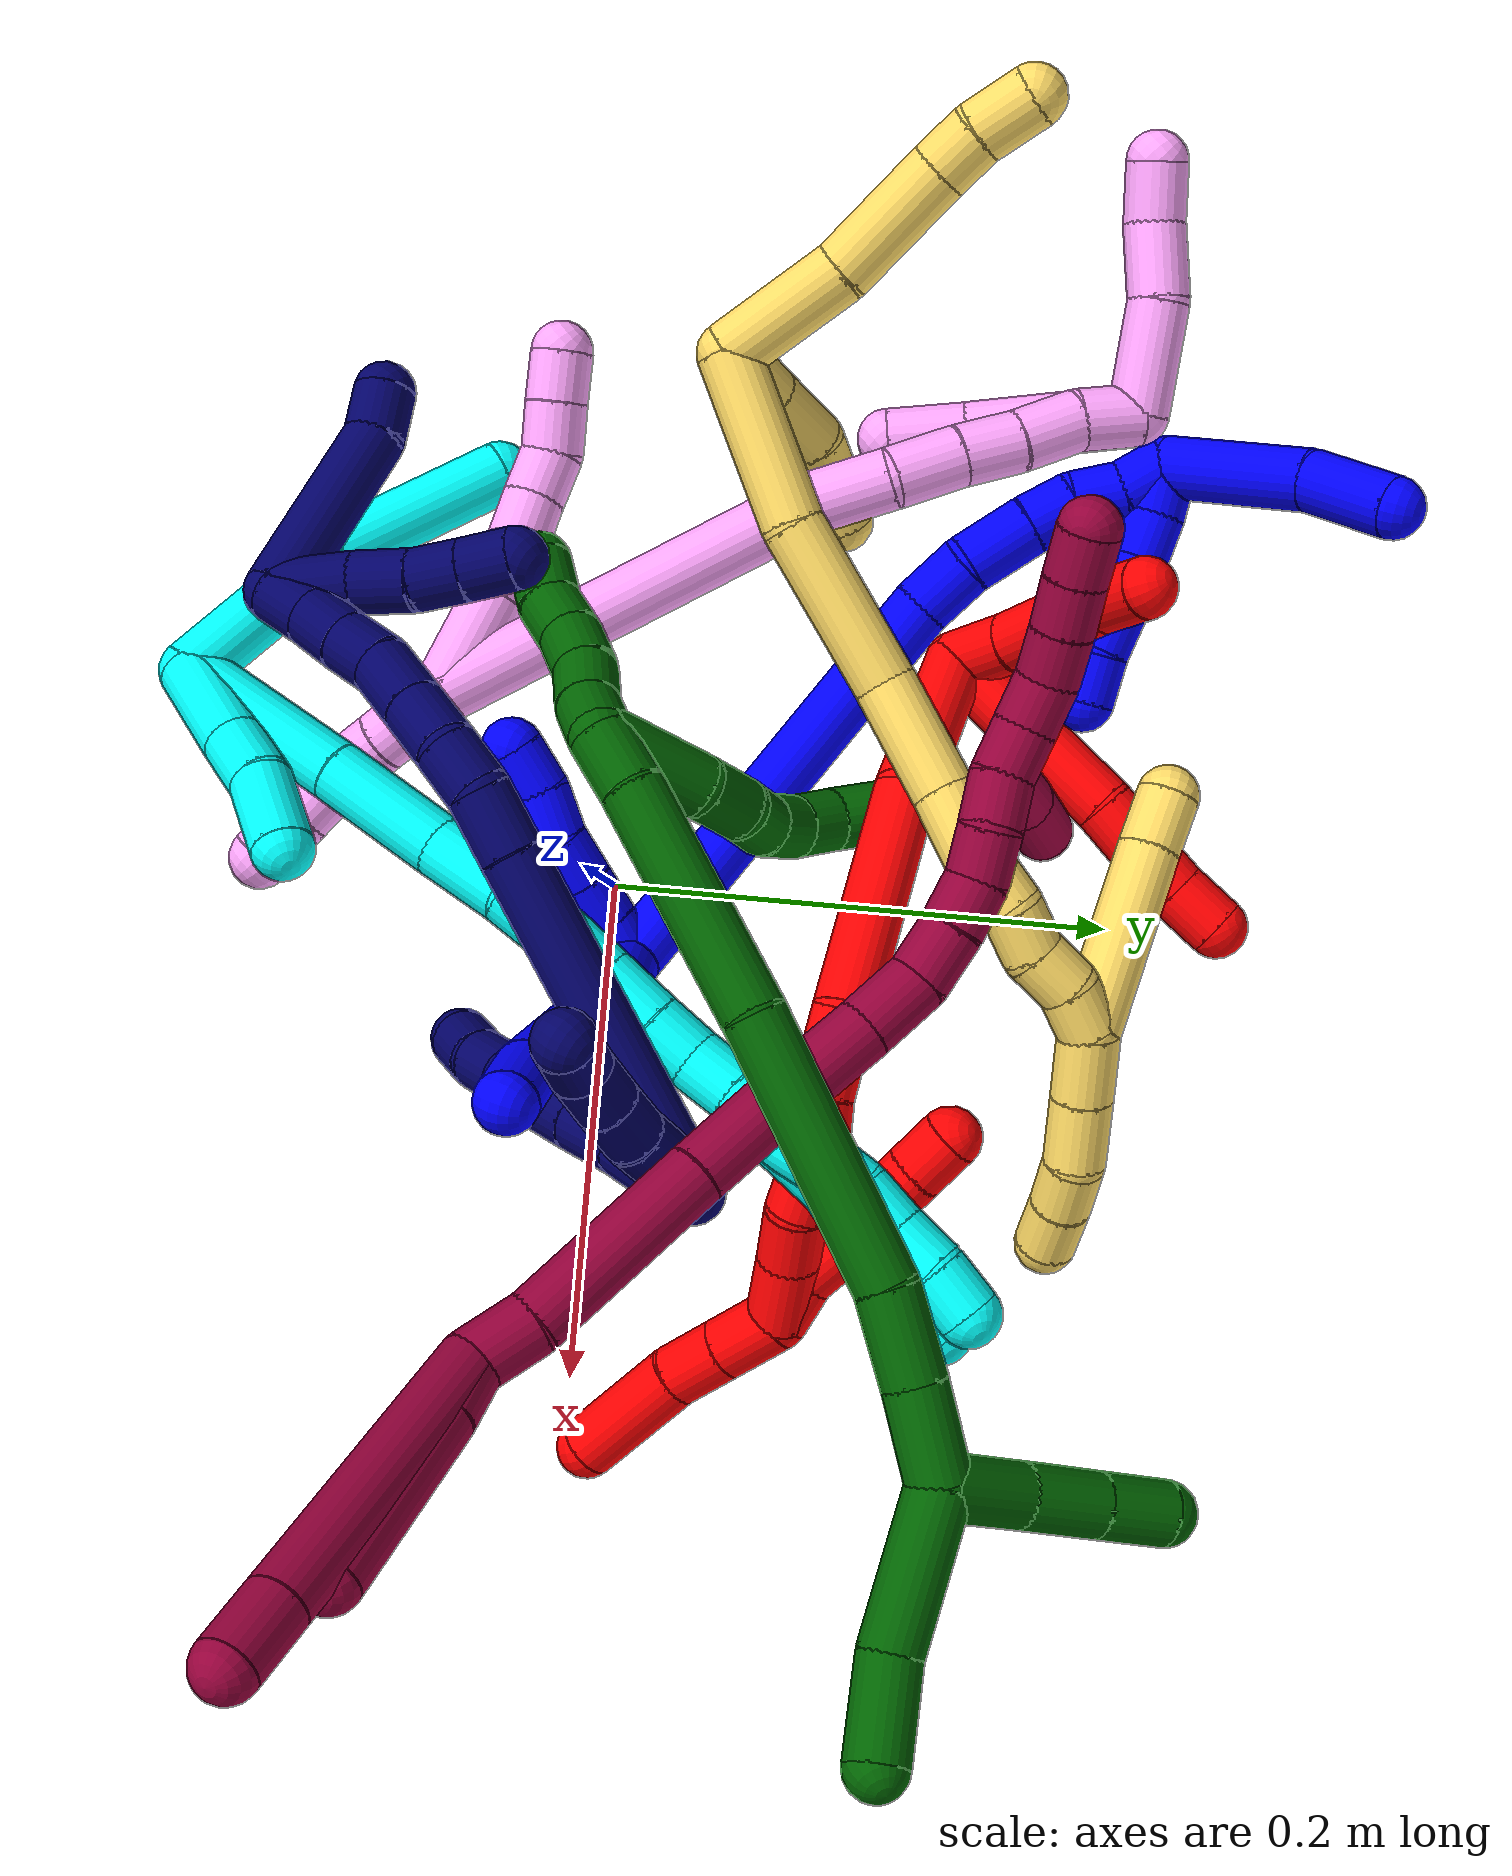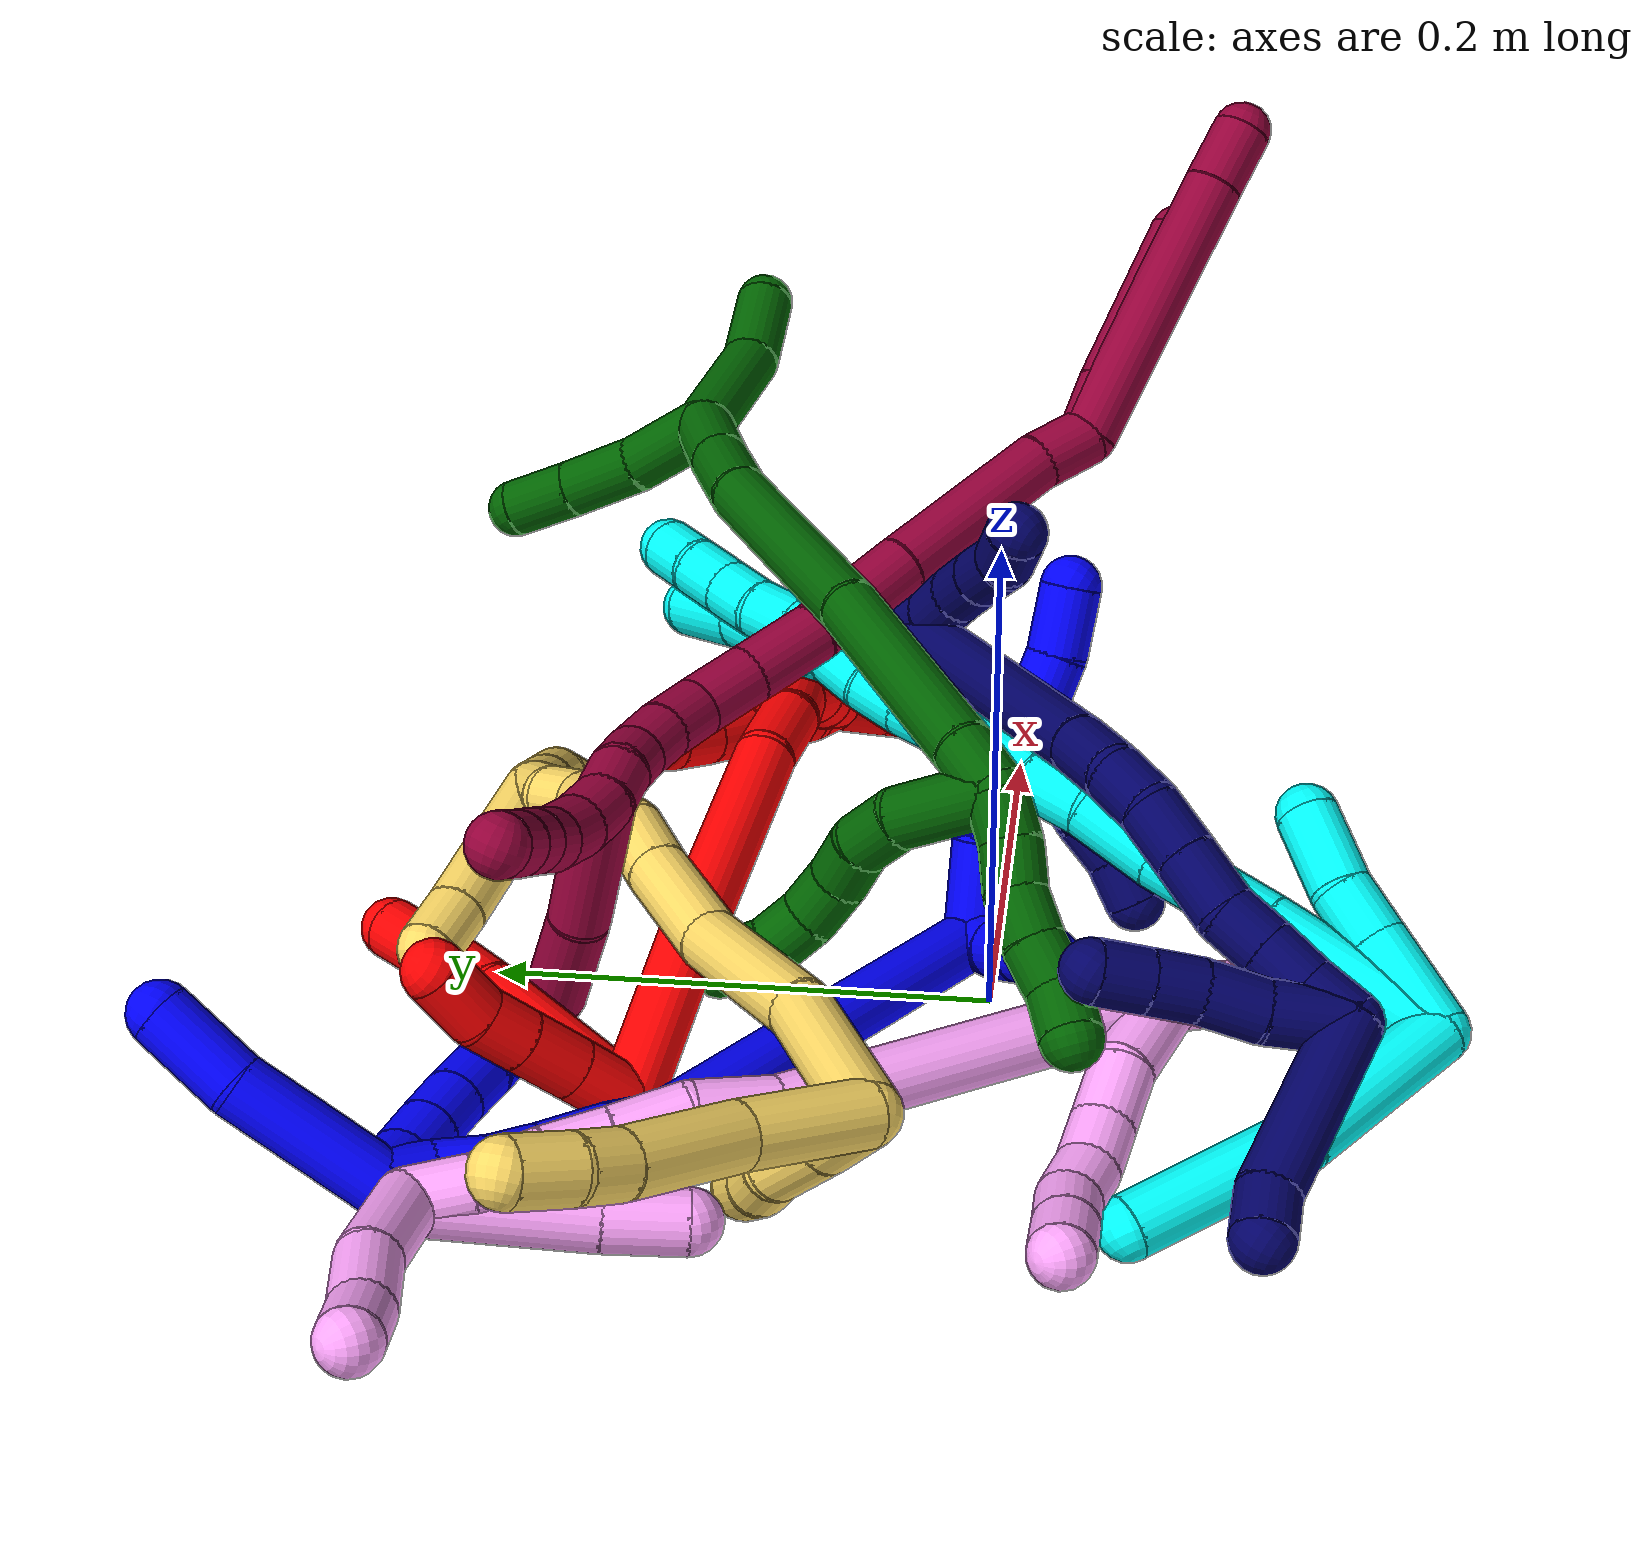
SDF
<sdf version="1.7">
 <world name="default">
  <plugin name="TubeGeneratorPlugin" filename="libtube_generator_plugin.so"/>
  <model name="photoneo_s_sensor">
   <static>1</static>
   <pose>0 0 2 1.57079 1.57079 3.14159</pose>
   <link name="link">
    <inertial><mass>0.1</mass></inertial>
    <sensor name="sensor" type="depth">
     <update_rate>30</update_rate>
     <camera>
      <horizontal_fov>1.22</horizontal_fov>
      <image><width>1920</width><height>1200</height><format>B8G8R8</format></image>
      <clip><near>0.1</near><far>4</far></clip>
      <depth_camera><output>points</output></depth_camera>
     </camera>
     <plugin name="camera_plugin" filename="libgazebo_ros_depth_camera.so">
      <baseline>0.2</baseline>
      <alwaysOn>1</alwaysOn>
      <updateRate>0.0</updateRate>
      <cameraName>camera_ir</cameraName>
      <imageTopicName>/camera/color/image_raw</imageTopicName>
      <cameraInfoTopicName>/camera/color/camera_info</cameraInfoTopicName>
      <depthImageTopicName>/camera/depth/image_raw</depthImageTopicName>
      <depthImageCameraInfoTopicName>/camera/depth/camera_info</depthImageCameraInfoTopicName>
      <pointCloudTopicName>/camera/depth/points</pointCloudTopicName>
      <frameName>fr_optical</frameName>
      <pointCloudCutoff>0.1</pointCloudCutoff>
      <pointCloudCutoffMax>2.0</pointCloudCutoffMax>
      <distortionK1>0</distortionK1>
      <distortionK2>0</distortionK2>
      <distortionK3>0</distortionK3>
      <distortionT1>0</distortionT1>
      <distortionT2>0</distortionT2>
      <CxPrime>0</CxPrime>
      <Cx>0</Cx>
      <Cy>0</Cy>
      <focalLength>0</focalLength>
      <hackBaseline>0</hackBaseline>
     </plugin>
    </sensor>
   </link>
  </model>
  <gravity>0 0 -9.8</gravity>
  <magnetic_field>6e-06 2.3e-05 -4.2e-05</magnetic_field>
  <atmosphere type="adiabatic"/>
  <physics name="default_physics" default="0" type="ode">
   <max_step_size>0.003</max_step_size>
   <real_time_factor>1</real_time_factor>
   <real_time_update_rate>1000</real_time_update_rate>
   <max_contacts>10000</max_contacts>
   <ode>
    <solver>
     <type>quick</type>
     <iters>100</iters>
     <sor>1.3</sor>
     <use_dynamic_moi_rescaling>0</use_dynamic_moi_rescaling>
    </solver>
    <constraints>
     <contact_max_correcting_vel>0</contact_max_correcting_vel>
     <contact_surface_layer>0.001</contact_surface_layer>
     <cfm>0</cfm>
     <erp>0.2</erp>
    </constraints>
   </ode>
  </physics>
  <scene><ambient>0.4 0.4 0.4 1</ambient><background>0.7 0.7 0.7 1</background><shadows>0</shadows></scene>
  <audio><device>default</device></audio>
  <spherical_coordinates>
   <surface_model>EARTH_WGS84</surface_model>
   <latitude_deg>0</latitude_deg>
   <longitude_deg>0</longitude_deg>
   <elevation>0</elevation>
   <heading_deg>0</heading_deg>
  </spherical_coordinates>
  <model name="bin">
   <static>1</static>
   <link name="bottom">
    <collision name="collision-bottom">
     <pose>0 0 -0.01 0 -0 0</pose>
     <geometry><box><size>0.8 0.6 0.02</size></box></geometry>
     <surface>
      <friction><ode><mu>100</mu><mu2>100</mu2></ode></friction>
      <contact><collide_bitmask>65535</collide_bitmask></contact>
     </surface>
    </collision>
   </link>
   <link name="west_wall">
    <collision name="collision-west_wall">
     <pose>-0.41 0 0.1 0 -0 0</pose>
     <geometry><box><size>0.02 0.6 0.2</size></box></geometry>
     <surface>
      <friction><ode><mu>100</mu><mu2>100</mu2></ode></friction>
      <contact><collide_bitmask>65535</collide_bitmask></contact>
     </surface>
    </collision>
   </link>
   <link name="east_wall">
    <collision name="collision-east_wall">
     <pose>0.41 0 0.1 0 -0 0</pose>
     <geometry><box><size>0.02 0.6 0.2</size></box></geometry>
     <surface>
      <friction><ode><mu>100</mu><mu2>100</mu2></ode></friction>
      <contact><collide_bitmask>65535</collide_bitmask></contact>
     </surface>
    </collision>
   </link>
   <link name="south_wall">
    <collision name="collision-south_wall">
     <pose>0 -0.31 0.1 0 -0 0</pose>
     <geometry><box><size>0.8 0.02 0.2</size></box></geometry>
     <surface>
      <friction><ode><mu>100</mu><mu2>100</mu2></ode></friction>
      <contact><collide_bitmask>65535</collide_bitmask></contact>
     </surface>
    </collision>
   </link>
   <link name="north_wall">
    <collision name="collision-north_wall">
     <pose>0 0.31 0.1 0 -0 0</pose>
     <geometry><box><size>0.8 0.02 0.2</size></box></geometry>
     <surface>
      <friction><ode><mu>100</mu><mu2>100</mu2></ode></friction>
      <contact><collide_bitmask>65535</collide_bitmask></contact>
     </surface>
    </collision>
   </link>
  </model>
  <model name="1">
   <static>0</static>
   <link name="1">
    <collision name="collision-cylinder-e_1_2_8">
     <pose>-0.007142 -0.017736 0.007792 1.15686 -0.353205 -0.231998</pose>
     <geometry><cylinder><radius>0.0125</radius><length>0.041294</length></cylinder></geometry>
     <surface>
      <friction><ode><mu>1.16</mu><mu2>1.16</mu2><slip1>0</slip1><slip2>0</slip2></ode></friction>
      <contact><ode><kp>1e+06</kp><kd>1</kd><max_vel>0</max_vel><min_depth>0.001</min_depth></ode></contact>
     </surface>
    </collision>
    <visual name="visual-cylinder-e_1_2_8">
     <pose>-0.007142 -0.017736 0.007792 1.15686 -0.353205 -0.231998</pose>
     <geometry><cylinder><radius>0.0125</radius><length>0.041294</length></cylinder></geometry>
     <material><ambient>0 0 1 1</ambient></material>
    </visual>
    <collision name="collision-cylinder-e_2_8_9">
     <pose>-0.024998 -0.073951 0.019929 1.45835 -0.269942 -0.241472</pose>
     <geometry><cylinder><radius>0.0125</radius><length>0.080357</length></cylinder></geometry>
     <surface>
      <friction><ode><mu>1.16</mu><mu2>1.16</mu2><slip1>0</slip1><slip2>0</slip2></ode></friction>
      <contact><ode><kp>1e+06</kp><kd>1</kd><max_vel>0</max_vel><min_depth>0.001</min_depth></ode></contact>
     </surface>
    </collision>
    <visual name="visual-cylinder-e_2_8_9">
     <pose>-0.024998 -0.073951 0.019929 1.45835 -0.269942 -0.241472</pose>
     <geometry><cylinder><radius>0.0125</radius><length>0.080357</length></cylinder></geometry>
     <material><ambient>0 0 1 1</ambient></material>
    </visual>
    <collision name="collision-cylinder-e_3_9_6">
     <pose>-0.039656 -0.125426 0.028333 1.26804 -0.281876 -0.207893</pose>
     <geometry><cylinder><radius>0.0125</radius><length>0.028349</length></cylinder></geometry>
     <surface>
      <friction><ode><mu>1.16</mu><mu2>1.16</mu2><slip1>0</slip1><slip2>0</slip2></ode></friction>
      <contact><ode><kp>1e+06</kp><kd>1</kd><max_vel>0</max_vel><min_depth>0.001</min_depth></ode></contact>
     </surface>
    </collision>
    <visual name="visual-cylinder-e_3_9_6">
     <pose>-0.039656 -0.125426 0.028333 1.26804 -0.281876 -0.207893</pose>
     <geometry><cylinder><radius>0.0125</radius><length>0.028349</length></cylinder></geometry>
     <material><ambient>0 0 1 1</ambient></material>
    </visual>
    <collision name="collision-cylinder-e_1_2_10">
     <pose>-0.008199 0.000612 -0.005693 -3.03449 -0.961151 2.93668</pose>
     <geometry><cylinder><radius>0.0125</radius><length>0.02</length></cylinder></geometry>
     <surface>
      <friction><ode><mu>1.16</mu><mu2>1.16</mu2><slip1>0</slip1><slip2>0</slip2></ode></friction>
      <contact><ode><kp>1e+06</kp><kd>1</kd><max_vel>0</max_vel><min_depth>0.001</min_depth></ode></contact>
     </surface>
    </collision>
    <visual name="visual-cylinder-e_1_2_10">
     <pose>-0.008199 0.000612 -0.005693 -3.03449 -0.961151 2.93668</pose>
     <geometry><cylinder><radius>0.0125</radius><length>0.02</length></cylinder></geometry>
     <material><ambient>0 0 1 1</ambient></material>
    </visual>
    <collision name="collision-cylinder-e_2_10_11">
     <pose>-0.024888 0.000453 -0.016612 2.9951 -1.01418 -2.87895</pose>
     <geometry><cylinder><radius>0.0125</radius><length>0.02</length></cylinder></geometry>
     <surface>
      <friction><ode><mu>1.16</mu><mu2>1.16</mu2><slip1>0</slip1><slip2>0</slip2></ode></friction>
      <contact><ode><kp>1e+06</kp><kd>1</kd><max_vel>0</max_vel><min_depth>0.001</min_depth></ode></contact>
     </surface>
    </collision>
    <visual name="visual-cylinder-e_2_10_11">
     <pose>-0.024888 0.000453 -0.016612 2.9951 -1.01418 -2.87895</pose>
     <geometry><cylinder><radius>0.0125</radius><length>0.02</length></cylinder></geometry>
     <material><ambient>0 0 1 1</ambient></material>
    </visual>
    <collision name="collision-cylinder-e_3_11_12">
     <pose>-0.04181 -0.000909 -0.027183 3.03141 -1.00313 -2.94113</pose>
     <geometry><cylinder><radius>0.0125</radius><length>0.02</length></cylinder></geometry>
     <surface>
      <friction><ode><mu>1.16</mu><mu2>1.16</mu2><slip1>0</slip1><slip2>0</slip2></ode></friction>
      <contact><ode><kp>1e+06</kp><kd>1</kd><max_vel>0</max_vel><min_depth>0.001</min_depth></ode></contact>
     </surface>
    </collision>
    <visual name="visual-cylinder-e_3_11_12">
     <pose>-0.04181 -0.000909 -0.027183 3.03141 -1.00313 -2.94113</pose>
     <geometry><cylinder><radius>0.0125</radius><length>0.02</length></cylinder></geometry>
     <material><ambient>0 0 1 1</ambient></material>
    </visual>
    <collision name="collision-cylinder-e_4_12_13">
     <pose>-0.058225 0.001129 -0.037945 -2.68974 -0.924552 2.2772</pose>
     <geometry><cylinder><radius>0.0125</radius><length>0.02</length></cylinder></geometry>
     <surface>
      <friction><ode><mu>1.16</mu><mu2>1.16</mu2><slip1>0</slip1><slip2>0</slip2></ode></friction>
      <contact><ode><kp>1e+06</kp><kd>1</kd><max_vel>0</max_vel><min_depth>0.001</min_depth></ode></contact>
     </surface>
    </collision>
    <visual name="visual-cylinder-e_4_12_13">
     <pose>-0.058225 0.001129 -0.037945 -2.68974 -0.924552 2.2772</pose>
     <geometry><cylinder><radius>0.0125</radius><length>0.02</length></cylinder></geometry>
     <material><ambient>0 0 1 1</ambient></material>
    </visual>
    <collision name="collision-cylinder-e_5_13_5">
     <pose>-0.073946 0.004356 -0.049669 -3.04704 -0.884741 2.94248</pose>
     <geometry><cylinder><radius>0.0125</radius><length>0.02</length></cylinder></geometry>
     <surface>
      <friction><ode><mu>1.16</mu><mu2>1.16</mu2><slip1>0</slip1><slip2>0</slip2></ode></friction>
      <contact><ode><kp>1e+06</kp><kd>1</kd><max_vel>0</max_vel><min_depth>0.001</min_depth></ode></contact>
     </surface>
    </collision>
    <visual name="visual-cylinder-e_5_13_5">
     <pose>-0.073946 0.004356 -0.049669 -3.04704 -0.884741 2.94248</pose>
     <geometry><cylinder><radius>0.0125</radius><length>0.02</length></cylinder></geometry>
     <material><ambient>0 0 1 1</ambient></material>
    </visual>
    <collision name="collision-cylinder-e_1_2_14">
     <pose>-0.058074 0.065795 0.029512 -1.14916 -0.67799 0.448896</pose>
     <geometry><cylinder><radius>0.0125</radius><length>0.185176</length></cylinder></geometry>
     <surface>
      <friction><ode><mu>1.16</mu><mu2>1.16</mu2><slip1>0</slip1><slip2>0</slip2></ode></friction>
      <contact><ode><kp>1e+06</kp><kd>1</kd><max_vel>0</max_vel><min_depth>0.001</min_depth></ode></contact>
     </surface>
    </collision>
    <visual name="visual-cylinder-e_1_2_14">
     <pose>-0.058074 0.065795 0.029512 -1.14916 -0.67799 0.448896</pose>
     <geometry><cylinder><radius>0.0125</radius><length>0.185176</length></cylinder></geometry>
     <material><ambient>0 0 1 1</ambient></material>
    </visual>
    <collision name="collision-cylinder-e_2_14_15">
     <pose>-0.124656 0.138334 0.065567 -0.800376 -0.735828 0.32327</pose>
     <geometry><cylinder><radius>0.0125</radius><length>0.025352</length></cylinder></geometry>
     <surface>
      <friction><ode><mu>1.16</mu><mu2>1.16</mu2><slip1>0</slip1><slip2>0</slip2></ode></friction>
      <contact><ode><kp>1e+06</kp><kd>1</kd><max_vel>0</max_vel><min_depth>0.001</min_depth></ode></contact>
     </surface>
    </collision>
    <visual name="visual-cylinder-e_2_14_15">
     <pose>-0.124656 0.138334 0.065567 -0.800376 -0.735828 0.32327</pose>
     <geometry><cylinder><radius>0.0125</radius><length>0.025352</length></cylinder></geometry>
     <material><ambient>0 0 1 1</ambient></material>
    </visual>
    <collision name="collision-cylinder-e_3_15_16">
     <pose>-0.139741 0.154878 0.080518 -0.861838 -0.471092 0.219784</pose>
     <geometry><cylinder><radius>0.0125</radius><length>0.028982</length></cylinder></geometry>
     <surface>
      <friction><ode><mu>1.16</mu><mu2>1.16</mu2><slip1>0</slip1><slip2>0</slip2></ode></friction>
      <contact><ode><kp>1e+06</kp><kd>1</kd><max_vel>0</max_vel><min_depth>0.001</min_depth></ode></contact>
     </surface>
    </collision>
    <visual name="visual-cylinder-e_3_15_16">
     <pose>-0.139741 0.154878 0.080518 -0.861838 -0.471092 0.219784</pose>
     <geometry><cylinder><radius>0.0125</radius><length>0.028982</length></cylinder></geometry>
     <material><ambient>0 0 1 1</ambient></material>
    </visual>
    <collision name="collision-cylinder-e_4_16_17">
     <pose>-0.150337 0.171282 0.095341 -0.79969 -0.411633 0.176004</pose>
     <geometry><cylinder><radius>0.0125</radius><length>0.020092</length></cylinder></geometry>
     <surface>
      <friction><ode><mu>1.16</mu><mu2>1.16</mu2><slip1>0</slip1><slip2>0</slip2></ode></friction>
      <contact><ode><kp>1e+06</kp><kd>1</kd><max_vel>0</max_vel><min_depth>0.001</min_depth></ode></contact>
     </surface>
    </collision>
    <visual name="visual-cylinder-e_4_16_17">
     <pose>-0.150337 0.171282 0.095341 -0.79969 -0.411633 0.176004</pose>
     <geometry><cylinder><radius>0.0125</radius><length>0.020092</length></cylinder></geometry>
     <material><ambient>0 0 1 1</ambient></material>
    </visual>
    <collision name="collision-cylinder-e_5_17_18">
     <pose>-0.156349 0.183578 0.109922 -0.608968 -0.197564 0.062268</pose>
     <geometry><cylinder><radius>0.0125</radius><length>0.020302</length></cylinder></geometry>
     <surface>
      <friction><ode><mu>1.16</mu><mu2>1.16</mu2><slip1>0</slip1><slip2>0</slip2></ode></friction>
      <contact><ode><kp>1e+06</kp><kd>1</kd><max_vel>0</max_vel><min_depth>0.001</min_depth></ode></contact>
     </surface>
    </collision>
    <visual name="visual-cylinder-e_5_17_18">
     <pose>-0.156349 0.183578 0.109922 -0.608968 -0.197564 0.062268</pose>
     <geometry><cylinder><radius>0.0125</radius><length>0.020302</length></cylinder></geometry>
     <material><ambient>0 0 1 1</ambient></material>
    </visual>
    <collision name="collision-cylinder-e_6_18_1">
     <pose>-0.163104 0.195195 0.124658 -0.733541 -0.493825 0.193054</pose>
     <geometry><cylinder><radius>0.0125</radius><length>0.020095</length></cylinder></geometry>
     <surface>
      <friction><ode><mu>1.16</mu><mu2>1.16</mu2><slip1>0</slip1><slip2>0</slip2></ode></friction>
      <contact><ode><kp>1e+06</kp><kd>1</kd><max_vel>0</max_vel><min_depth>0.001</min_depth></ode></contact>
     </surface>
    </collision>
    <visual name="visual-cylinder-e_6_18_1">
     <pose>-0.163104 0.195195 0.124658 -0.733541 -0.493825 0.193054</pose>
     <geometry><cylinder><radius>0.0125</radius><length>0.020095</length></cylinder></geometry>
     <material><ambient>0 0 1 1</ambient></material>
    </visual>
    <collision name="collision-cylinder-e_1_1_19">
     <pose>-0.15947 0.195695 0.13151 1.51921 0.99667 0.953953</pose>
     <geometry><cylinder><radius>0.0125</radius><length>0.02</length></cylinder></geometry>
     <surface>
      <friction><ode><mu>1.16</mu><mu2>1.16</mu2><slip1>0</slip1><slip2>0</slip2></ode></friction>
      <contact><ode><kp>1e+06</kp><kd>1</kd><max_vel>0</max_vel><min_depth>0.001</min_depth></ode></contact>
     </surface>
    </collision>
    <visual name="visual-cylinder-e_1_1_19">
     <pose>-0.15947 0.195695 0.13151 1.51921 0.99667 0.953953</pose>
     <geometry><cylinder><radius>0.0125</radius><length>0.02</length></cylinder></geometry>
     <material><ambient>0 0 1 1</ambient></material>
    </visual>
    <collision name="collision-cylinder-e_2_19_20">
     <pose>-0.143947 0.183256 0.131721 1.58068 0.79326 0.800327</pose>
     <geometry><cylinder><radius>0.0125</radius><length>0.02</length></cylinder></geometry>
     <surface>
      <friction><ode><mu>1.16</mu><mu2>1.16</mu2><slip1>0</slip1><slip2>0</slip2></ode></friction>
      <contact><ode><kp>1e+06</kp><kd>1</kd><max_vel>0</max_vel><min_depth>0.001</min_depth></ode></contact>
     </surface>
    </collision>
    <visual name="visual-cylinder-e_2_19_20">
     <pose>-0.143947 0.183256 0.131721 1.58068 0.79326 0.800327</pose>
     <geometry><cylinder><radius>0.0125</radius><length>0.02</length></cylinder></geometry>
     <material><ambient>0 0 1 1</ambient></material>
    </visual>
    <collision name="collision-cylinder-e_3_20_21">
     <pose>-0.129729 0.169195 0.131416 1.60427 0.788322 0.812343</pose>
     <geometry><cylinder><radius>0.0125</radius><length>0.02</length></cylinder></geometry>
     <surface>
      <friction><ode><mu>1.16</mu><mu2>1.16</mu2><slip1>0</slip1><slip2>0</slip2></ode></friction>
      <contact><ode><kp>1e+06</kp><kd>1</kd><max_vel>0</max_vel><min_depth>0.001</min_depth></ode></contact>
     </surface>
    </collision>
    <visual name="visual-cylinder-e_3_20_21">
     <pose>-0.129729 0.169195 0.131416 1.60427 0.788322 0.812343</pose>
     <geometry><cylinder><radius>0.0125</radius><length>0.02</length></cylinder></geometry>
     <material><ambient>0 0 1 1</ambient></material>
    </visual>
    <collision name="collision-cylinder-e_4_21_22">
     <pose>-0.115538 0.155135 0.13054 1.66183 0.789419 0.856208</pose>
     <geometry><cylinder><radius>0.0125</radius><length>0.02</length></cylinder></geometry>
     <surface>
      <friction><ode><mu>1.16</mu><mu2>1.16</mu2><slip1>0</slip1><slip2>0</slip2></ode></friction>
      <contact><ode><kp>1e+06</kp><kd>1</kd><max_vel>0</max_vel><min_depth>0.001</min_depth></ode></contact>
     </surface>
    </collision>
    <visual name="visual-cylinder-e_4_21_22">
     <pose>-0.115538 0.155135 0.13054 1.66183 0.789419 0.856208</pose>
     <geometry><cylinder><radius>0.0125</radius><length>0.02</length></cylinder></geometry>
     <material><ambient>0 0 1 1</ambient></material>
    </visual>
    <collision name="collision-cylinder-e_5_22_4">
     <pose>-0.09999 0.142771 0.129934 1.56439 1.00626 1.00085</pose>
     <geometry><cylinder><radius>0.0125</radius><length>0.02</length></cylinder></geometry>
     <surface>
      <friction><ode><mu>1.16</mu><mu2>1.16</mu2><slip1>0</slip1><slip2>0</slip2></ode></friction>
      <contact><ode><kp>1e+06</kp><kd>1</kd><max_vel>0</max_vel><min_depth>0.001</min_depth></ode></contact>
     </surface>
    </collision>
    <visual name="visual-cylinder-e_5_22_4">
     <pose>-0.09999 0.142771 0.129934 1.56439 1.00626 1.00085</pose>
     <geometry><cylinder><radius>0.0125</radius><length>0.02</length></cylinder></geometry>
     <material><ambient>0 0 1 1</ambient></material>
    </visual>
    <collision name="collision-cylinder-e_1_1_23">
     <pose>-0.174767 0.198906 0.161676 0.072528 -0.222299 -0.008098</pose>
     <geometry><cylinder><radius>0.0125</radius><length>0.062592</length></cylinder></geometry>
     <surface>
      <friction><ode><mu>1.16</mu><mu2>1.16</mu2><slip1>0</slip1><slip2>0</slip2></ode></friction>
      <contact><ode><kp>1e+06</kp><kd>1</kd><max_vel>0</max_vel><min_depth>0.001</min_depth></ode></contact>
     </surface>
    </collision>
    <visual name="visual-cylinder-e_1_1_23">
     <pose>-0.174767 0.198906 0.161676 0.072528 -0.222299 -0.008098</pose>
     <geometry><cylinder><radius>0.0125</radius><length>0.062592</length></cylinder></geometry>
     <material><ambient>0 0 1 1</ambient></material>
    </visual>
    <collision name="collision-cylinder-e_2_23_3">
     <pose>-0.18305 0.192602 0.21032 0.221211 -0.074047 -0.008227</pose>
     <geometry><cylinder><radius>0.0125</radius><length>0.037408</length></cylinder></geometry>
     <surface>
      <friction><ode><mu>1.16</mu><mu2>1.16</mu2><slip1>0</slip1><slip2>0</slip2></ode></friction>
      <contact><ode><kp>1e+06</kp><kd>1</kd><max_vel>0</max_vel><min_depth>0.001</min_depth></ode></contact>
     </surface>
    </collision>
    <visual name="visual-cylinder-e_2_23_3">
     <pose>-0.18305 0.192602 0.21032 0.221211 -0.074047 -0.008227</pose>
     <geometry><cylinder><radius>0.0125</radius><length>0.037408</length></cylinder></geometry>
     <material><ambient>0 0 1 1</ambient></material>
    </visual>
    <collision name="collision-sphere-3">
     <pose>-0.184434 0.188509 0.228518 0 -0 0</pose>
     <geometry><sphere><radius>0.0125</radius></sphere></geometry>
     <surface>
      <friction><ode><mu>1.16</mu><mu2>1.16</mu2><slip1>0</slip1><slip2>0</slip2></ode></friction>
      <contact><ode><kp>1e+06</kp><kd>1</kd><max_vel>0</max_vel><min_depth>0.001</min_depth></ode></contact>
     </surface>
    </collision>
    <visual name="visual-sphere-3">
     <pose>-0.184434 0.188509 0.228518 0 -0 0</pose>
     <geometry><sphere><radius>0.0125</radius></sphere></geometry>
     <material><ambient>0 0 1 1</ambient></material>
    </visual>
    <collision name="collision-sphere-23">
     <pose>-0.181667 0.196694 0.192121 0 -0 0</pose>
     <geometry><sphere><radius>0.0125</radius></sphere></geometry>
     <surface>
      <friction><ode><mu>1.16</mu><mu2>1.16</mu2><slip1>0</slip1><slip2>0</slip2></ode></friction>
      <contact><ode><kp>1e+06</kp><kd>1</kd><max_vel>0</max_vel><min_depth>0.001</min_depth></ode></contact>
     </surface>
    </collision>
    <visual name="visual-sphere-23">
     <pose>-0.181667 0.196694 0.192121 0 -0 0</pose>
     <geometry><sphere><radius>0.0125</radius></sphere></geometry>
     <material><ambient>0 0 1 1</ambient></material>
    </visual>
    <collision name="collision-sphere-4">
     <pose>-0.091542 0.137421 0.129968 0 -0 0</pose>
     <geometry><sphere><radius>0.0125</radius></sphere></geometry>
     <surface>
      <friction><ode><mu>1.16</mu><mu2>1.16</mu2><slip1>0</slip1><slip2>0</slip2></ode></friction>
      <contact><ode><kp>1e+06</kp><kd>1</kd><max_vel>0</max_vel><min_depth>0.001</min_depth></ode></contact>
     </surface>
    </collision>
    <visual name="visual-sphere-4">
     <pose>-0.091542 0.137421 0.129968 0 -0 0</pose>
     <geometry><sphere><radius>0.0125</radius></sphere></geometry>
     <material><ambient>0 0 1 1</ambient></material>
    </visual>
    <collision name="collision-sphere-22">
     <pose>-0.108438 0.148121 0.129899 0 -0 0</pose>
     <geometry><sphere><radius>0.0125</radius></sphere></geometry>
     <surface>
      <friction><ode><mu>1.16</mu><mu2>1.16</mu2><slip1>0</slip1><slip2>0</slip2></ode></friction>
      <contact><ode><kp>1e+06</kp><kd>1</kd><max_vel>0</max_vel><min_depth>0.001</min_depth></ode></contact>
     </surface>
    </collision>
    <visual name="visual-sphere-22">
     <pose>-0.108438 0.148121 0.129899 0 -0 0</pose>
     <geometry><sphere><radius>0.0125</radius></sphere></geometry>
     <material><ambient>0 0 1 1</ambient></material>
    </visual>
    <collision name="collision-sphere-21">
     <pose>-0.122637 0.162148 0.13118 0 -0 0</pose>
     <geometry><sphere><radius>0.0125</radius></sphere></geometry>
     <surface>
      <friction><ode><mu>1.16</mu><mu2>1.16</mu2><slip1>0</slip1><slip2>0</slip2></ode></friction>
      <contact><ode><kp>1e+06</kp><kd>1</kd><max_vel>0</max_vel><min_depth>0.001</min_depth></ode></contact>
     </surface>
    </collision>
    <visual name="visual-sphere-21">
     <pose>-0.122637 0.162148 0.13118 0 -0 0</pose>
     <geometry><sphere><radius>0.0125</radius></sphere></geometry>
     <material><ambient>0 0 1 1</ambient></material>
    </visual>
    <collision name="collision-sphere-20">
     <pose>-0.136821 0.176241 0.131652 0 -0 0</pose>
     <geometry><sphere><radius>0.0125</radius></sphere></geometry>
     <surface>
      <friction><ode><mu>1.16</mu><mu2>1.16</mu2><slip1>0</slip1><slip2>0</slip2></ode></friction>
      <contact><ode><kp>1e+06</kp><kd>1</kd><max_vel>0</max_vel><min_depth>0.001</min_depth></ode></contact>
     </surface>
    </collision>
    <visual name="visual-sphere-20">
     <pose>-0.136821 0.176241 0.131652 0 -0 0</pose>
     <geometry><sphere><radius>0.0125</radius></sphere></geometry>
     <material><ambient>0 0 1 1</ambient></material>
    </visual>
    <collision name="collision-sphere-11">
     <pose>-0.033378 -0.000318 -0.021839 0 -0 0</pose>
     <geometry><sphere><radius>0.0125</radius></sphere></geometry>
     <surface>
      <friction><ode><mu>1.16</mu><mu2>1.16</mu2><slip1>0</slip1><slip2>0</slip2></ode></friction>
      <contact><ode><kp>1e+06</kp><kd>1</kd><max_vel>0</max_vel><min_depth>0.001</min_depth></ode></contact>
     </surface>
    </collision>
    <visual name="visual-sphere-11">
     <pose>-0.033378 -0.000318 -0.021839 0 -0 0</pose>
     <geometry><sphere><radius>0.0125</radius></sphere></geometry>
     <material><ambient>0 0 1 1</ambient></material>
    </visual>
    <collision name="collision-sphere-10">
     <pose>-0.016397 0.001224 -0.011386 0 -0 0</pose>
     <geometry><sphere><radius>0.0125</radius></sphere></geometry>
     <surface>
      <friction><ode><mu>1.16</mu><mu2>1.16</mu2><slip1>0</slip1><slip2>0</slip2></ode></friction>
      <contact><ode><kp>1e+06</kp><kd>1</kd><max_vel>0</max_vel><min_depth>0.001</min_depth></ode></contact>
     </surface>
    </collision>
    <visual name="visual-sphere-10">
     <pose>-0.016397 0.001224 -0.011386 0 -0 0</pose>
     <geometry><sphere><radius>0.0125</radius></sphere></geometry>
     <material><ambient>0 0 1 1</ambient></material>
    </visual>
    <collision name="collision-sphere-6">
     <pose>-0.043599 -0.138422 0.032392 0 -0 0</pose>
     <geometry><sphere><radius>0.0125</radius></sphere></geometry>
     <surface>
      <friction><ode><mu>1.16</mu><mu2>1.16</mu2><slip1>0</slip1><slip2>0</slip2></ode></friction>
      <contact><ode><kp>1e+06</kp><kd>1</kd><max_vel>0</max_vel><min_depth>0.001</min_depth></ode></contact>
     </surface>
    </collision>
    <visual name="visual-sphere-6">
     <pose>-0.043599 -0.138422 0.032392 0 -0 0</pose>
     <geometry><sphere><radius>0.0125</radius></sphere></geometry>
     <material><ambient>0 0 1 1</ambient></material>
    </visual>
    <collision name="collision-sphere-9">
     <pose>-0.035713 -0.11243 0.024274 0 -0 0</pose>
     <geometry><sphere><radius>0.0125</radius></sphere></geometry>
     <surface>
      <friction><ode><mu>1.16</mu><mu2>1.16</mu2><slip1>0</slip1><slip2>0</slip2></ode></friction>
      <contact><ode><kp>1e+06</kp><kd>1</kd><max_vel>0</max_vel><min_depth>0.001</min_depth></ode></contact>
     </surface>
    </collision>
    <visual name="visual-sphere-9">
     <pose>-0.035713 -0.11243 0.024274 0 -0 0</pose>
     <geometry><sphere><radius>0.0125</radius></sphere></geometry>
     <material><ambient>0 0 1 1</ambient></material>
    </visual>
    <collision name="collision-sphere-2">
     <geometry><sphere><radius>0.0125</radius></sphere></geometry>
     <surface>
      <friction><ode><mu>1.16</mu><mu2>1.16</mu2><slip1>0</slip1><slip2>0</slip2></ode></friction>
      <contact><ode><kp>1e+06</kp><kd>1</kd><max_vel>0</max_vel><min_depth>0.001</min_depth></ode></contact>
     </surface>
    </collision>
    <visual name="visual-sphere-2">
     <geometry><sphere><radius>0.0125</radius></sphere></geometry>
     <material><ambient>0 0 1 1</ambient></material>
    </visual>
    <collision name="collision-sphere-19">
     <pose>-0.151074 0.190271 0.13179 0 -0 0</pose>
     <geometry><sphere><radius>0.0125</radius></sphere></geometry>
     <surface>
      <friction><ode><mu>1.16</mu><mu2>1.16</mu2><slip1>0</slip1><slip2>0</slip2></ode></friction>
      <contact><ode><kp>1e+06</kp><kd>1</kd><max_vel>0</max_vel><min_depth>0.001</min_depth></ode></contact>
     </surface>
    </collision>
    <visual name="visual-sphere-19">
     <pose>-0.151074 0.190271 0.13179 0 -0 0</pose>
     <geometry><sphere><radius>0.0125</radius></sphere></geometry>
     <material><ambient>0 0 1 1</ambient></material>
    </visual>
    <collision name="collision-sphere-8">
     <pose>-0.014284 -0.035472 0.015584 0 -0 0</pose>
     <geometry><sphere><radius>0.0125</radius></sphere></geometry>
     <surface>
      <friction><ode><mu>1.16</mu><mu2>1.16</mu2><slip1>0</slip1><slip2>0</slip2></ode></friction>
      <contact><ode><kp>1e+06</kp><kd>1</kd><max_vel>0</max_vel><min_depth>0.001</min_depth></ode></contact>
     </surface>
    </collision>
    <visual name="visual-sphere-8">
     <pose>-0.014284 -0.035472 0.015584 0 -0 0</pose>
     <geometry><sphere><radius>0.0125</radius></sphere></geometry>
     <material><ambient>0 0 1 1</ambient></material>
    </visual>
    <collision name="collision-sphere-12">
     <pose>-0.050241 -0.001501 -0.032527 0 -0 0</pose>
     <geometry><sphere><radius>0.0125</radius></sphere></geometry>
     <surface>
      <friction><ode><mu>1.16</mu><mu2>1.16</mu2><slip1>0</slip1><slip2>0</slip2></ode></friction>
      <contact><ode><kp>1e+06</kp><kd>1</kd><max_vel>0</max_vel><min_depth>0.001</min_depth></ode></contact>
     </surface>
    </collision>
    <visual name="visual-sphere-12">
     <pose>-0.050241 -0.001501 -0.032527 0 -0 0</pose>
     <geometry><sphere><radius>0.0125</radius></sphere></geometry>
     <material><ambient>0 0 1 1</ambient></material>
    </visual>
    <collision name="collision-sphere-13">
     <pose>-0.066208 0.003758 -0.043362 0 -0 0</pose>
     <geometry><sphere><radius>0.0125</radius></sphere></geometry>
     <surface>
      <friction><ode><mu>1.16</mu><mu2>1.16</mu2><slip1>0</slip1><slip2>0</slip2></ode></friction>
      <contact><ode><kp>1e+06</kp><kd>1</kd><max_vel>0</max_vel><min_depth>0.001</min_depth></ode></contact>
     </surface>
    </collision>
    <visual name="visual-sphere-13">
     <pose>-0.066208 0.003758 -0.043362 0 -0 0</pose>
     <geometry><sphere><radius>0.0125</radius></sphere></geometry>
     <material><ambient>0 0 1 1</ambient></material>
    </visual>
    <collision name="collision-sphere-5">
     <pose>-0.081683 0.004954 -0.055976 0 -0 0</pose>
     <geometry><sphere><radius>0.0125</radius></sphere></geometry>
     <surface>
      <friction><ode><mu>1.16</mu><mu2>1.16</mu2><slip1>0</slip1><slip2>0</slip2></ode></friction>
      <contact><ode><kp>1e+06</kp><kd>1</kd><max_vel>0</max_vel><min_depth>0.001</min_depth></ode></contact>
     </surface>
    </collision>
    <visual name="visual-sphere-5">
     <pose>-0.081683 0.004954 -0.055976 0 -0 0</pose>
     <geometry><sphere><radius>0.0125</radius></sphere></geometry>
     <material><ambient>0 0 1 1</ambient></material>
    </visual>
    <collision name="collision-sphere-14">
     <pose>-0.116148 0.131591 0.059023 0 -0 0</pose>
     <geometry><sphere><radius>0.0125</radius></sphere></geometry>
     <surface>
      <friction><ode><mu>1.16</mu><mu2>1.16</mu2><slip1>0</slip1><slip2>0</slip2></ode></friction>
      <contact><ode><kp>1e+06</kp><kd>1</kd><max_vel>0</max_vel><min_depth>0.001</min_depth></ode></contact>
     </surface>
    </collision>
    <visual name="visual-sphere-14">
     <pose>-0.116148 0.131591 0.059023 0 -0 0</pose>
     <geometry><sphere><radius>0.0125</radius></sphere></geometry>
     <material><ambient>0 0 1 1</ambient></material>
    </visual>
    <collision name="collision-sphere-15">
     <pose>-0.133164 0.145076 0.072111 0 -0 0</pose>
     <geometry><sphere><radius>0.0125</radius></sphere></geometry>
     <surface>
      <friction><ode><mu>1.16</mu><mu2>1.16</mu2><slip1>0</slip1><slip2>0</slip2></ode></friction>
      <contact><ode><kp>1e+06</kp><kd>1</kd><max_vel>0</max_vel><min_depth>0.001</min_depth></ode></contact>
     </surface>
    </collision>
    <visual name="visual-sphere-15">
     <pose>-0.133164 0.145076 0.072111 0 -0 0</pose>
     <geometry><sphere><radius>0.0125</radius></sphere></geometry>
     <material><ambient>0 0 1 1</ambient></material>
    </visual>
    <collision name="collision-sphere-16">
     <pose>-0.146318 0.164679 0.088925 0 -0 0</pose>
     <geometry><sphere><radius>0.0125</radius></sphere></geometry>
     <surface>
      <friction><ode><mu>1.16</mu><mu2>1.16</mu2><slip1>0</slip1><slip2>0</slip2></ode></friction>
      <contact><ode><kp>1e+06</kp><kd>1</kd><max_vel>0</max_vel><min_depth>0.001</min_depth></ode></contact>
     </surface>
    </collision>
    <visual name="visual-sphere-16">
     <pose>-0.146318 0.164679 0.088925 0 -0 0</pose>
     <geometry><sphere><radius>0.0125</radius></sphere></geometry>
     <material><ambient>0 0 1 1</ambient></material>
    </visual>
    <collision name="collision-sphere-17">
     <pose>-0.154357 0.177885 0.101758 0 -0 0</pose>
     <geometry><sphere><radius>0.0125</radius></sphere></geometry>
     <surface>
      <friction><ode><mu>1.16</mu><mu2>1.16</mu2><slip1>0</slip1><slip2>0</slip2></ode></friction>
      <contact><ode><kp>1e+06</kp><kd>1</kd><max_vel>0</max_vel><min_depth>0.001</min_depth></ode></contact>
     </surface>
    </collision>
    <visual name="visual-sphere-17">
     <pose>-0.154357 0.177885 0.101758 0 -0 0</pose>
     <geometry><sphere><radius>0.0125</radius></sphere></geometry>
     <material><ambient>0 0 1 1</ambient></material>
    </visual>
    <collision name="collision-sphere-18">
     <pose>-0.158342 0.189272 0.118087 0 -0 0</pose>
     <geometry><sphere><radius>0.0125</radius></sphere></geometry>
     <surface>
      <friction><ode><mu>1.16</mu><mu2>1.16</mu2><slip1>0</slip1><slip2>0</slip2></ode></friction>
      <contact><ode><kp>1e+06</kp><kd>1</kd><max_vel>0</max_vel><min_depth>0.001</min_depth></ode></contact>
     </surface>
    </collision>
    <visual name="visual-sphere-18">
     <pose>-0.158342 0.189272 0.118087 0 -0 0</pose>
     <geometry><sphere><radius>0.0125</radius></sphere></geometry>
     <material><ambient>0 0 1 1</ambient></material>
    </visual>
    <collision name="collision-sphere-1">
     <pose>-0.167867 0.201118 0.13123 0 -0 0</pose>
     <geometry><sphere><radius>0.0125</radius></sphere></geometry>
     <surface>
      <friction><ode><mu>1.16</mu><mu2>1.16</mu2><slip1>0</slip1><slip2>0</slip2></ode></friction>
      <contact><ode><kp>1e+06</kp><kd>1</kd><max_vel>0</max_vel><min_depth>0.001</min_depth></ode></contact>
     </surface>
    </collision>
    <visual name="visual-sphere-1">
     <pose>-0.167867 0.201118 0.13123 0 -0 0</pose>
     <geometry><sphere><radius>0.0125</radius></sphere></geometry>
     <material><ambient>0 0 1 1</ambient></material>
    </visual>
    <inertial>
     <pose>-0.087688 0.076971 0.062916 0 -0 0</pose>
     <mass>0.75</mass>
     <inertia>
      <ixx>0.000621</ixx>
      <ixy>0</ixy>
      <ixz>0</ixz>
      <iyy>0.000564</iyy>
      <iyz>0</iyz>
      <izz>5.2e-05</izz>
     </inertia>
    </inertial>
   </link>
   <pose>0.030279 0.00902 0.011429 -1.08703 0.681083 0.060421</pose>
  </model>
  <model name="2">
   <static>0</static>
   <link name="2">
    <collision name="collision-cylinder-e_1_2_8">
     <pose>0.035642 0.010041 0.019271 -0.480354 1.0233 -0.273328</pose>
     <geometry><cylinder><radius>0.0125</radius><length>0.083488</length></cylinder></geometry>
     <surface>
      <friction><ode><mu>1.16</mu><mu2>1.16</mu2><slip1>0</slip1><slip2>0</slip2></ode></friction>
      <contact><ode><kp>1e+06</kp><kd>1</kd><max_vel>0</max_vel><min_depth>0.001</min_depth></ode></contact>
     </surface>
    </collision>
    <visual name="visual-cylinder-e_1_2_8">
     <pose>0.035642 0.010041 0.019271 -0.480354 1.0233 -0.273328</pose>
     <geometry><cylinder><radius>0.0125</radius><length>0.083488</length></cylinder></geometry>
     <material><ambient>1 0 0 1</ambient></material>
    </visual>
    <collision name="collision-cylinder-e_2_8_9">
     <pose>0.082021 0.023844 0.042297 -0.786149 1.11104 -0.503837</pose>
     <geometry><cylinder><radius>0.0125</radius><length>0.02396</length></cylinder></geometry>
     <surface>
      <friction><ode><mu>1.16</mu><mu2>1.16</mu2><slip1>0</slip1><slip2>0</slip2></ode></friction>
      <contact><ode><kp>1e+06</kp><kd>1</kd><max_vel>0</max_vel><min_depth>0.001</min_depth></ode></contact>
     </surface>
    </collision>
    <visual name="visual-cylinder-e_2_8_9">
     <pose>0.082021 0.023844 0.042297 -0.786149 1.11104 -0.503837</pose>
     <geometry><cylinder><radius>0.0125</radius><length>0.02396</length></cylinder></geometry>
     <material><ambient>1 0 0 1</ambient></material>
    </visual>
    <collision name="collision-cylinder-e_3_9_10">
     <pose>0.101707 0.031346 0.049051 -0.89509 1.0791 -0.559813</pose>
     <geometry><cylinder><radius>0.0125</radius><length>0.020305</length></cylinder></geometry>
     <surface>
      <friction><ode><mu>1.16</mu><mu2>1.16</mu2><slip1>0</slip1><slip2>0</slip2></ode></friction>
      <contact><ode><kp>1e+06</kp><kd>1</kd><max_vel>0</max_vel><min_depth>0.001</min_depth></ode></contact>
     </surface>
    </collision>
    <visual name="visual-cylinder-e_3_9_10">
     <pose>0.101707 0.031346 0.049051 -0.89509 1.0791 -0.559813</pose>
     <geometry><cylinder><radius>0.0125</radius><length>0.020305</length></cylinder></geometry>
     <material><ambient>1 0 0 1</ambient></material>
    </visual>
    <collision name="collision-cylinder-e_4_10_6">
     <pose>0.119993 0.038898 0.056742 -0.682166 0.996107 -0.381344</pose>
     <geometry><cylinder><radius>0.0125</radius><length>0.022247</length></cylinder></geometry>
     <surface>
      <friction><ode><mu>1.16</mu><mu2>1.16</mu2><slip1>0</slip1><slip2>0</slip2></ode></friction>
      <contact><ode><kp>1e+06</kp><kd>1</kd><max_vel>0</max_vel><min_depth>0.001</min_depth></ode></contact>
     </surface>
    </collision>
    <visual name="visual-cylinder-e_4_10_6">
     <pose>0.119993 0.038898 0.056742 -0.682166 0.996107 -0.381344</pose>
     <geometry><cylinder><radius>0.0125</radius><length>0.022247</length></cylinder></geometry>
     <material><ambient>1 0 0 1</ambient></material>
    </visual>
    <collision name="collision-cylinder-e_1_2_11">
     <pose>-9.8e-05 -7.7e-05 0.014039 0.005454 -0.00696 -1.9e-05</pose>
     <geometry><cylinder><radius>0.0125</radius><length>0.02808</length></cylinder></geometry>
     <surface>
      <friction><ode><mu>1.16</mu><mu2>1.16</mu2><slip1>0</slip1><slip2>0</slip2></ode></friction>
      <contact><ode><kp>1e+06</kp><kd>1</kd><max_vel>0</max_vel><min_depth>0.001</min_depth></ode></contact>
     </surface>
    </collision>
    <visual name="visual-cylinder-e_1_2_11">
     <pose>-9.8e-05 -7.7e-05 0.014039 0.005454 -0.00696 -1.9e-05</pose>
     <geometry><cylinder><radius>0.0125</radius><length>0.02808</length></cylinder></geometry>
     <material><ambient>1 0 0 1</ambient></material>
    </visual>
    <collision name="collision-cylinder-e_2_11_12">
     <pose>-0.001152 -0.000393 0.040941 0.018641 -0.074192 -0.000692</pose>
     <geometry><cylinder><radius>0.0125</radius><length>0.025799</length></cylinder></geometry>
     <surface>
      <friction><ode><mu>1.16</mu><mu2>1.16</mu2><slip1>0</slip1><slip2>0</slip2></ode></friction>
      <contact><ode><kp>1e+06</kp><kd>1</kd><max_vel>0</max_vel><min_depth>0.001</min_depth></ode></contact>
     </surface>
    </collision>
    <visual name="visual-cylinder-e_2_11_12">
     <pose>-0.001152 -0.000393 0.040941 0.018641 -0.074192 -0.000692</pose>
     <geometry><cylinder><radius>0.0125</radius><length>0.025799</length></cylinder></geometry>
     <material><ambient>1 0 0 1</ambient></material>
    </visual>
    <collision name="collision-cylinder-e_3_12_13">
     <pose>-0.00271 -0.000815 0.064105 0.017684 -0.058345 -0.000516</pose>
     <geometry><cylinder><radius>0.0125</radius><length>0.020644</length></cylinder></geometry>
     <surface>
      <friction><ode><mu>1.16</mu><mu2>1.16</mu2><slip1>0</slip1><slip2>0</slip2></ode></friction>
      <contact><ode><kp>1e+06</kp><kd>1</kd><max_vel>0</max_vel><min_depth>0.001</min_depth></ode></contact>
     </surface>
    </collision>
    <visual name="visual-cylinder-e_3_12_13">
     <pose>-0.00271 -0.000815 0.064105 0.017684 -0.058345 -0.000516</pose>
     <geometry><cylinder><radius>0.0125</radius><length>0.020644</length></cylinder></geometry>
     <material><ambient>1 0 0 1</ambient></material>
    </visual>
    <collision name="collision-cylinder-e_4_13_5">
     <pose>-0.002767 -0.004084 0.086755 0.244967 0.042765 0.005265</pose>
     <geometry><cylinder><radius>0.0125</radius><length>0.025478</length></cylinder></geometry>
     <surface>
      <friction><ode><mu>1.16</mu><mu2>1.16</mu2><slip1>0</slip1><slip2>0</slip2></ode></friction>
      <contact><ode><kp>1e+06</kp><kd>1</kd><max_vel>0</max_vel><min_depth>0.001</min_depth></ode></contact>
     </surface>
    </collision>
    <visual name="visual-cylinder-e_4_13_5">
     <pose>-0.002767 -0.004084 0.086755 0.244967 0.042765 0.005265</pose>
     <geometry><cylinder><radius>0.0125</radius><length>0.025478</length></cylinder></geometry>
     <material><ambient>1 0 0 1</ambient></material>
    </visual>
    <collision name="collision-cylinder-e_1_2_14">
     <pose>0.024621 -0.02771 0.000413 1.5559 0.726378 0.716536</pose>
     <geometry><cylinder><radius>0.0125</radius><length>0.07414</length></cylinder></geometry>
     <surface>
      <friction><ode><mu>1.16</mu><mu2>1.16</mu2><slip1>0</slip1><slip2>0</slip2></ode></friction>
      <contact><ode><kp>1e+06</kp><kd>1</kd><max_vel>0</max_vel><min_depth>0.001</min_depth></ode></contact>
     </surface>
    </collision>
    <visual name="visual-cylinder-e_1_2_14">
     <pose>0.024621 -0.02771 0.000413 1.5559 0.726378 0.716536</pose>
     <geometry><cylinder><radius>0.0125</radius><length>0.07414</length></cylinder></geometry>
     <material><ambient>1 0 0 1</ambient></material>
    </visual>
    <collision name="collision-cylinder-e_2_14_15">
     <pose>0.087942 -0.079675 -0.007544 1.90308 0.985331 1.29099</pose>
     <geometry><cylinder><radius>0.0125</radius><length>0.092869</length></cylinder></geometry>
     <surface>
      <friction><ode><mu>1.16</mu><mu2>1.16</mu2><slip1>0</slip1><slip2>0</slip2></ode></friction>
      <contact><ode><kp>1e+06</kp><kd>1</kd><max_vel>0</max_vel><min_depth>0.001</min_depth></ode></contact>
     </surface>
    </collision>
    <visual name="visual-cylinder-e_2_14_15">
     <pose>0.087942 -0.079675 -0.007544 1.90308 0.985331 1.29099</pose>
     <geometry><cylinder><radius>0.0125</radius><length>0.092869</length></cylinder></geometry>
     <material><ambient>1 0 0 1</ambient></material>
    </visual>
    <collision name="collision-cylinder-e_3_15_16">
     <pose>0.14162 -0.109233 -0.022196 2.44055 1.06883 2.03486</pose>
     <geometry><cylinder><radius>0.0125</radius><length>0.034167</length></cylinder></geometry>
     <surface>
      <friction><ode><mu>1.16</mu><mu2>1.16</mu2><slip1>0</slip1><slip2>0</slip2></ode></friction>
      <contact><ode><kp>1e+06</kp><kd>1</kd><max_vel>0</max_vel><min_depth>0.001</min_depth></ode></contact>
     </surface>
    </collision>
    <visual name="visual-cylinder-e_3_15_16">
     <pose>0.14162 -0.109233 -0.022196 2.44055 1.06883 2.03486</pose>
     <geometry><cylinder><radius>0.0125</radius><length>0.034167</length></cylinder></geometry>
     <material><ambient>1 0 0 1</ambient></material>
    </visual>
    <collision name="collision-cylinder-e_4_16_17">
     <pose>0.16748 -0.11561 -0.032551 2.88357 1.20139 2.76733</pose>
     <geometry><cylinder><radius>0.0125</radius><length>0.023343</length></cylinder></geometry>
     <surface>
      <friction><ode><mu>1.16</mu><mu2>1.16</mu2><slip1>0</slip1><slip2>0</slip2></ode></friction>
      <contact><ode><kp>1e+06</kp><kd>1</kd><max_vel>0</max_vel><min_depth>0.001</min_depth></ode></contact>
     </surface>
    </collision>
    <visual name="visual-cylinder-e_4_16_17">
     <pose>0.16748 -0.11561 -0.032551 2.88357 1.20139 2.76733</pose>
     <geometry><cylinder><radius>0.0125</radius><length>0.023343</length></cylinder></geometry>
     <material><ambient>1 0 0 1</ambient></material>
    </visual>
    <collision name="collision-cylinder-e_5_17_18">
     <pose>0.187487 -0.117119 -0.04409 3.08353 0.884266 3.01906</pose>
     <geometry><cylinder><radius>0.0125</radius><length>0.023589</length></cylinder></geometry>
     <surface>
      <friction><ode><mu>1.16</mu><mu2>1.16</mu2><slip1>0</slip1><slip2>0</slip2></ode></friction>
      <contact><ode><kp>1e+06</kp><kd>1</kd><max_vel>0</max_vel><min_depth>0.001</min_depth></ode></contact>
     </surface>
    </collision>
    <visual name="visual-cylinder-e_5_17_18">
     <pose>0.187487 -0.117119 -0.04409 3.08353 0.884266 3.01906</pose>
     <geometry><cylinder><radius>0.0125</radius><length>0.023589</length></cylinder></geometry>
     <material><ambient>1 0 0 1</ambient></material>
    </visual>
    <collision name="collision-cylinder-e_6_18_19">
     <pose>0.20551 -0.114914 -0.058699 -2.78776 0.862884 -2.40075</pose>
     <geometry><cylinder><radius>0.0125</radius><length>0.02343</length></cylinder></geometry>
     <surface>
      <friction><ode><mu>1.16</mu><mu2>1.16</mu2><slip1>0</slip1><slip2>0</slip2></ode></friction>
      <contact><ode><kp>1e+06</kp><kd>1</kd><max_vel>0</max_vel><min_depth>0.001</min_depth></ode></contact>
     </surface>
    </collision>
    <visual name="visual-cylinder-e_6_18_19">
     <pose>0.20551 -0.114914 -0.058699 -2.78776 0.862884 -2.40075</pose>
     <geometry><cylinder><radius>0.0125</radius><length>0.02343</length></cylinder></geometry>
     <material><ambient>1 0 0 1</ambient></material>
    </visual>
    <collision name="collision-cylinder-e_7_19_1">
     <pose>0.225586 -0.110061 -0.074371 -2.88761 0.903346 -2.62689</pose>
     <geometry><cylinder><radius>0.0125</radius><length>0.028461</length></cylinder></geometry>
     <surface>
      <friction><ode><mu>1.16</mu><mu2>1.16</mu2><slip1>0</slip1><slip2>0</slip2></ode></friction>
      <contact><ode><kp>1e+06</kp><kd>1</kd><max_vel>0</max_vel><min_depth>0.001</min_depth></ode></contact>
     </surface>
    </collision>
    <visual name="visual-cylinder-e_7_19_1">
     <pose>0.225586 -0.110061 -0.074371 -2.88761 0.903346 -2.62689</pose>
     <geometry><cylinder><radius>0.0125</radius><length>0.028461</length></cylinder></geometry>
     <material><ambient>1 0 0 1</ambient></material>
    </visual>
    <collision name="collision-cylinder-e_1_1_20">
     <pose>0.229862 -0.104548 -0.076456 -0.473454 -0.761652 0.192582</pose>
     <geometry><cylinder><radius>0.0125</radius><length>0.02</length></cylinder></geometry>
     <surface>
      <friction><ode><mu>1.16</mu><mu2>1.16</mu2><slip1>0</slip1><slip2>0</slip2></ode></friction>
      <contact><ode><kp>1e+06</kp><kd>1</kd><max_vel>0</max_vel><min_depth>0.001</min_depth></ode></contact>
     </surface>
    </collision>
    <visual name="visual-cylinder-e_1_1_20">
     <pose>0.229862 -0.104548 -0.076456 -0.473454 -0.761652 0.192582</pose>
     <geometry><cylinder><radius>0.0125</radius><length>0.02</length></cylinder></geometry>
     <material><ambient>1 0 0 1</ambient></material>
    </visual>
    <collision name="collision-cylinder-e_2_20_21">
     <pose>0.218628 -0.097035 -0.062047 -0.486429 -0.448081 0.112959</pose>
     <geometry><cylinder><radius>0.0125</radius><length>0.02</length></cylinder></geometry>
     <surface>
      <friction><ode><mu>1.16</mu><mu2>1.16</mu2><slip1>0</slip1><slip2>0</slip2></ode></friction>
      <contact><ode><kp>1e+06</kp><kd>1</kd><max_vel>0</max_vel><min_depth>0.001</min_depth></ode></contact>
     </surface>
    </collision>
    <visual name="visual-cylinder-e_2_20_21">
     <pose>0.218628 -0.097035 -0.062047 -0.486429 -0.448081 0.112959</pose>
     <geometry><cylinder><radius>0.0125</radius><length>0.02</length></cylinder></geometry>
     <material><ambient>1 0 0 1</ambient></material>
    </visual>
    <collision name="collision-cylinder-e_3_21_22">
     <pose>0.209046 -0.089013 -0.046469 -0.46396 -0.552749 0.133807</pose>
     <geometry><cylinder><radius>0.0125</radius><length>0.02</length></cylinder></geometry>
     <surface>
      <friction><ode><mu>1.16</mu><mu2>1.16</mu2><slip1>0</slip1><slip2>0</slip2></ode></friction>
      <contact><ode><kp>1e+06</kp><kd>1</kd><max_vel>0</max_vel><min_depth>0.001</min_depth></ode></contact>
     </surface>
    </collision>
    <visual name="visual-cylinder-e_3_21_22">
     <pose>0.209046 -0.089013 -0.046469 -0.46396 -0.552749 0.133807</pose>
     <geometry><cylinder><radius>0.0125</radius><length>0.02</length></cylinder></geometry>
     <material><ambient>1 0 0 1</ambient></material>
    </visual>
    <collision name="collision-cylinder-e_4_22_23">
     <pose>0.198771 -0.081162 -0.031215 -0.486488 -0.526376 0.133528</pose>
     <geometry><cylinder><radius>0.0125</radius><length>0.02</length></cylinder></geometry>
     <surface>
      <friction><ode><mu>1.16</mu><mu2>1.16</mu2><slip1>0</slip1><slip2>0</slip2></ode></friction>
      <contact><ode><kp>1e+06</kp><kd>1</kd><max_vel>0</max_vel><min_depth>0.001</min_depth></ode></contact>
     </surface>
    </collision>
    <visual name="visual-cylinder-e_4_22_23">
     <pose>0.198771 -0.081162 -0.031215 -0.486488 -0.526376 0.133528</pose>
     <geometry><cylinder><radius>0.0125</radius><length>0.02</length></cylinder></geometry>
     <material><ambient>1 0 0 1</ambient></material>
    </visual>
    <collision name="collision-cylinder-e_5_23_4">
     <pose>0.188822 -0.07353 -0.015644 -0.425214 -0.515003 0.113575</pose>
     <geometry><cylinder><radius>0.0125</radius><length>0.02</length></cylinder></geometry>
     <surface>
      <friction><ode><mu>1.16</mu><mu2>1.16</mu2><slip1>0</slip1><slip2>0</slip2></ode></friction>
      <contact><ode><kp>1e+06</kp><kd>1</kd><max_vel>0</max_vel><min_depth>0.001</min_depth></ode></contact>
     </surface>
    </collision>
    <visual name="visual-cylinder-e_5_23_4">
     <pose>0.188822 -0.07353 -0.015644 -0.425214 -0.515003 0.113575</pose>
     <geometry><cylinder><radius>0.0125</radius><length>0.02</length></cylinder></geometry>
     <material><ambient>1 0 0 1</ambient></material>
    </visual>
    <collision name="collision-cylinder-e_1_1_24">
     <pose>0.240242 -0.11172 -0.094847 2.82824 0.270147 1.42089</pose>
     <geometry><cylinder><radius>0.0125</radius><length>0.02607</length></cylinder></geometry>
     <surface>
      <friction><ode><mu>1.16</mu><mu2>1.16</mu2><slip1>0</slip1><slip2>0</slip2></ode></friction>
      <contact><ode><kp>1e+06</kp><kd>1</kd><max_vel>0</max_vel><min_depth>0.001</min_depth></ode></contact>
     </surface>
    </collision>
    <visual name="visual-cylinder-e_1_1_24">
     <pose>0.240242 -0.11172 -0.094847 2.82824 0.270147 1.42089</pose>
     <geometry><cylinder><radius>0.0125</radius><length>0.02607</length></cylinder></geometry>
     <material><ambient>1 0 0 1</ambient></material>
    </visual>
    <collision name="collision-cylinder-e_2_24_25">
     <pose>0.24697 -0.119233 -0.117856 2.82355 0.272153 1.41336</pose>
     <geometry><cylinder><radius>0.0125</radius><length>0.024173</length></cylinder></geometry>
     <surface>
      <friction><ode><mu>1.16</mu><mu2>1.16</mu2><slip1>0</slip1><slip2>0</slip2></ode></friction>
      <contact><ode><kp>1e+06</kp><kd>1</kd><max_vel>0</max_vel><min_depth>0.001</min_depth></ode></contact>
     </surface>
    </collision>
    <visual name="visual-cylinder-e_2_24_25">
     <pose>0.24697 -0.119233 -0.117856 2.82355 0.272153 1.41336</pose>
     <geometry><cylinder><radius>0.0125</radius><length>0.024173</length></cylinder></geometry>
     <material><ambient>1 0 0 1</ambient></material>
    </visual>
    <collision name="collision-cylinder-e_3_25_3">
     <pose>0.260541 -0.129564 -0.150538 2.84154 0.427843 1.92577</pose>
     <geometry><cylinder><radius>0.0125</radius><length>0.049757</length></cylinder></geometry>
     <surface>
      <friction><ode><mu>1.16</mu><mu2>1.16</mu2><slip1>0</slip1><slip2>0</slip2></ode></friction>
      <contact><ode><kp>1e+06</kp><kd>1</kd><max_vel>0</max_vel><min_depth>0.001</min_depth></ode></contact>
     </surface>
    </collision>
    <visual name="visual-cylinder-e_3_25_3">
     <pose>0.260541 -0.129564 -0.150538 2.84154 0.427843 1.92577</pose>
     <geometry><cylinder><radius>0.0125</radius><length>0.049757</length></cylinder></geometry>
     <material><ambient>1 0 0 1</ambient></material>
    </visual>
    <collision name="collision-sphere-3">
     <pose>0.270863 -0.136254 -0.172163 0 -0 0</pose>
     <geometry><sphere><radius>0.0125</radius></sphere></geometry>
     <surface>
      <friction><ode><mu>1.16</mu><mu2>1.16</mu2><slip1>0</slip1><slip2>0</slip2></ode></friction>
      <contact><ode><kp>1e+06</kp><kd>1</kd><max_vel>0</max_vel><min_depth>0.001</min_depth></ode></contact>
     </surface>
    </collision>
    <visual name="visual-sphere-3">
     <pose>0.270863 -0.136254 -0.172163 0 -0 0</pose>
     <geometry><sphere><radius>0.0125</radius></sphere></geometry>
     <material><ambient>1 0 0 1</ambient></material>
    </visual>
    <collision name="collision-sphere-25">
     <pose>0.250218 -0.122873 -0.128914 0 -0 0</pose>
     <geometry><sphere><radius>0.0125</radius></sphere></geometry>
     <surface>
      <friction><ode><mu>1.16</mu><mu2>1.16</mu2><slip1>0</slip1><slip2>0</slip2></ode></friction>
      <contact><ode><kp>1e+06</kp><kd>1</kd><max_vel>0</max_vel><min_depth>0.001</min_depth></ode></contact>
     </surface>
    </collision>
    <visual name="visual-sphere-25">
     <pose>0.250218 -0.122873 -0.128914 0 -0 0</pose>
     <geometry><sphere><radius>0.0125</radius></sphere></geometry>
     <material><ambient>1 0 0 1</ambient></material>
    </visual>
    <collision name="collision-sphere-24">
     <pose>0.243721 -0.115592 -0.106798 0 -0 0</pose>
     <geometry><sphere><radius>0.0125</radius></sphere></geometry>
     <surface>
      <friction><ode><mu>1.16</mu><mu2>1.16</mu2><slip1>0</slip1><slip2>0</slip2></ode></friction>
      <contact><ode><kp>1e+06</kp><kd>1</kd><max_vel>0</max_vel><min_depth>0.001</min_depth></ode></contact>
     </surface>
    </collision>
    <visual name="visual-sphere-24">
     <pose>0.243721 -0.115592 -0.106798 0 -0 0</pose>
     <geometry><sphere><radius>0.0125</radius></sphere></geometry>
     <material><ambient>1 0 0 1</ambient></material>
    </visual>
    <collision name="collision-sphere-4">
     <pose>0.183897 -0.06994 -0.007716 0 -0 0</pose>
     <geometry><sphere><radius>0.0125</radius></sphere></geometry>
     <surface>
      <friction><ode><mu>1.16</mu><mu2>1.16</mu2><slip1>0</slip1><slip2>0</slip2></ode></friction>
      <contact><ode><kp>1e+06</kp><kd>1</kd><max_vel>0</max_vel><min_depth>0.001</min_depth></ode></contact>
     </surface>
    </collision>
    <visual name="visual-sphere-4">
     <pose>0.183897 -0.06994 -0.007716 0 -0 0</pose>
     <geometry><sphere><radius>0.0125</radius></sphere></geometry>
     <material><ambient>1 0 0 1</ambient></material>
    </visual>
    <collision name="collision-sphere-23">
     <pose>0.193747 -0.07712 -0.023571 0 -0 0</pose>
     <geometry><sphere><radius>0.0125</radius></sphere></geometry>
     <surface>
      <friction><ode><mu>1.16</mu><mu2>1.16</mu2><slip1>0</slip1><slip2>0</slip2></ode></friction>
      <contact><ode><kp>1e+06</kp><kd>1</kd><max_vel>0</max_vel><min_depth>0.001</min_depth></ode></contact>
     </surface>
    </collision>
    <visual name="visual-sphere-23">
     <pose>0.193747 -0.07712 -0.023571 0 -0 0</pose>
     <geometry><sphere><radius>0.0125</radius></sphere></geometry>
     <material><ambient>1 0 0 1</ambient></material>
    </visual>
    <collision name="collision-sphere-22">
     <pose>0.203796 -0.085205 -0.038858 0 -0 0</pose>
     <geometry><sphere><radius>0.0125</radius></sphere></geometry>
     <surface>
      <friction><ode><mu>1.16</mu><mu2>1.16</mu2><slip1>0</slip1><slip2>0</slip2></ode></friction>
      <contact><ode><kp>1e+06</kp><kd>1</kd><max_vel>0</max_vel><min_depth>0.001</min_depth></ode></contact>
     </surface>
    </collision>
    <visual name="visual-sphere-22">
     <pose>0.203796 -0.085205 -0.038858 0 -0 0</pose>
     <geometry><sphere><radius>0.0125</radius></sphere></geometry>
     <material><ambient>1 0 0 1</ambient></material>
    </visual>
    <collision name="collision-sphere-21">
     <pose>0.214296 -0.092822 -0.05408 0 -0 0</pose>
     <geometry><sphere><radius>0.0125</radius></sphere></geometry>
     <surface>
      <friction><ode><mu>1.16</mu><mu2>1.16</mu2><slip1>0</slip1><slip2>0</slip2></ode></friction>
      <contact><ode><kp>1e+06</kp><kd>1</kd><max_vel>0</max_vel><min_depth>0.001</min_depth></ode></contact>
     </surface>
    </collision>
    <visual name="visual-sphere-21">
     <pose>0.214296 -0.092822 -0.05408 0 -0 0</pose>
     <geometry><sphere><radius>0.0125</radius></sphere></geometry>
     <material><ambient>1 0 0 1</ambient></material>
    </visual>
    <collision name="collision-sphere-20">
     <pose>0.222961 -0.101248 -0.070015 0 -0 0</pose>
     <geometry><sphere><radius>0.0125</radius></sphere></geometry>
     <surface>
      <friction><ode><mu>1.16</mu><mu2>1.16</mu2><slip1>0</slip1><slip2>0</slip2></ode></friction>
      <contact><ode><kp>1e+06</kp><kd>1</kd><max_vel>0</max_vel><min_depth>0.001</min_depth></ode></contact>
     </surface>
    </collision>
    <visual name="visual-sphere-20">
     <pose>0.222961 -0.101248 -0.070015 0 -0 0</pose>
     <geometry><sphere><radius>0.0125</radius></sphere></geometry>
     <material><ambient>1 0 0 1</ambient></material>
    </visual>
    <collision name="collision-sphere-11">
     <pose>-0.000195 -0.000153 0.028079 0 -0 0</pose>
     <geometry><sphere><radius>0.0125</radius></sphere></geometry>
     <surface>
      <friction><ode><mu>1.16</mu><mu2>1.16</mu2><slip1>0</slip1><slip2>0</slip2></ode></friction>
      <contact><ode><kp>1e+06</kp><kd>1</kd><max_vel>0</max_vel><min_depth>0.001</min_depth></ode></contact>
     </surface>
    </collision>
    <visual name="visual-sphere-11">
     <pose>-0.000195 -0.000153 0.028079 0 -0 0</pose>
     <geometry><sphere><radius>0.0125</radius></sphere></geometry>
     <material><ambient>1 0 0 1</ambient></material>
    </visual>
    <collision name="collision-sphere-6">
     <pose>0.12933 0.04271 0.061436 0 -0 0</pose>
     <geometry><sphere><radius>0.0125</radius></sphere></geometry>
     <surface>
      <friction><ode><mu>1.16</mu><mu2>1.16</mu2><slip1>0</slip1><slip2>0</slip2></ode></friction>
      <contact><ode><kp>1e+06</kp><kd>1</kd><max_vel>0</max_vel><min_depth>0.001</min_depth></ode></contact>
     </surface>
    </collision>
    <visual name="visual-sphere-6">
     <pose>0.12933 0.04271 0.061436 0 -0 0</pose>
     <geometry><sphere><radius>0.0125</radius></sphere></geometry>
     <material><ambient>1 0 0 1</ambient></material>
    </visual>
    <collision name="collision-sphere-10">
     <pose>0.110656 0.035086 0.052049 0 -0 0</pose>
     <geometry><sphere><radius>0.0125</radius></sphere></geometry>
     <surface>
      <friction><ode><mu>1.16</mu><mu2>1.16</mu2><slip1>0</slip1><slip2>0</slip2></ode></friction>
      <contact><ode><kp>1e+06</kp><kd>1</kd><max_vel>0</max_vel><min_depth>0.001</min_depth></ode></contact>
     </surface>
    </collision>
    <visual name="visual-sphere-10">
     <pose>0.110656 0.035086 0.052049 0 -0 0</pose>
     <geometry><sphere><radius>0.0125</radius></sphere></geometry>
     <material><ambient>1 0 0 1</ambient></material>
    </visual>
    <collision name="collision-sphere-9">
     <pose>0.092757 0.027606 0.046053 0 -0 0</pose>
     <geometry><sphere><radius>0.0125</radius></sphere></geometry>
     <surface>
      <friction><ode><mu>1.16</mu><mu2>1.16</mu2><slip1>0</slip1><slip2>0</slip2></ode></friction>
      <contact><ode><kp>1e+06</kp><kd>1</kd><max_vel>0</max_vel><min_depth>0.001</min_depth></ode></contact>
     </surface>
    </collision>
    <visual name="visual-sphere-9">
     <pose>0.092757 0.027606 0.046053 0 -0 0</pose>
     <geometry><sphere><radius>0.0125</radius></sphere></geometry>
     <material><ambient>1 0 0 1</ambient></material>
    </visual>
    <collision name="collision-sphere-2">
     <geometry><sphere><radius>0.0125</radius></sphere></geometry>
     <surface>
      <friction><ode><mu>1.16</mu><mu2>1.16</mu2><slip1>0</slip1><slip2>0</slip2></ode></friction>
      <contact><ode><kp>1e+06</kp><kd>1</kd><max_vel>0</max_vel><min_depth>0.001</min_depth></ode></contact>
     </surface>
    </collision>
    <visual name="visual-sphere-2">
     <geometry><sphere><radius>0.0125</radius></sphere></geometry>
     <material><ambient>1 0 0 1</ambient></material>
    </visual>
    <collision name="collision-sphere-19">
     <pose>0.21441 -0.112274 -0.065845 0 -0 0</pose>
     <geometry><sphere><radius>0.0125</radius></sphere></geometry>
     <surface>
      <friction><ode><mu>1.16</mu><mu2>1.16</mu2><slip1>0</slip1><slip2>0</slip2></ode></friction>
      <contact><ode><kp>1e+06</kp><kd>1</kd><max_vel>0</max_vel><min_depth>0.001</min_depth></ode></contact>
     </surface>
    </collision>
    <visual name="visual-sphere-19">
     <pose>0.21441 -0.112274 -0.065845 0 -0 0</pose>
     <geometry><sphere><radius>0.0125</radius></sphere></geometry>
     <material><ambient>1 0 0 1</ambient></material>
    </visual>
    <collision name="collision-sphere-8">
     <pose>0.071285 0.020082 0.038541 0 -0 0</pose>
     <geometry><sphere><radius>0.0125</radius></sphere></geometry>
     <surface>
      <friction><ode><mu>1.16</mu><mu2>1.16</mu2><slip1>0</slip1><slip2>0</slip2></ode></friction>
      <contact><ode><kp>1e+06</kp><kd>1</kd><max_vel>0</max_vel><min_depth>0.001</min_depth></ode></contact>
     </surface>
    </collision>
    <visual name="visual-sphere-8">
     <pose>0.071285 0.020082 0.038541 0 -0 0</pose>
     <geometry><sphere><radius>0.0125</radius></sphere></geometry>
     <material><ambient>1 0 0 1</ambient></material>
    </visual>
    <collision name="collision-sphere-12">
     <pose>-0.002108 -0.000633 0.053802 0 -0 0</pose>
     <geometry><sphere><radius>0.0125</radius></sphere></geometry>
     <surface>
      <friction><ode><mu>1.16</mu><mu2>1.16</mu2><slip1>0</slip1><slip2>0</slip2></ode></friction>
      <contact><ode><kp>1e+06</kp><kd>1</kd><max_vel>0</max_vel><min_depth>0.001</min_depth></ode></contact>
     </surface>
    </collision>
    <visual name="visual-sphere-12">
     <pose>-0.002108 -0.000633 0.053802 0 -0 0</pose>
     <geometry><sphere><radius>0.0125</radius></sphere></geometry>
     <material><ambient>1 0 0 1</ambient></material>
    </visual>
    <collision name="collision-sphere-13">
     <pose>-0.003312 -0.000997 0.074408 0 -0 0</pose>
     <geometry><sphere><radius>0.0125</radius></sphere></geometry>
     <surface>
      <friction><ode><mu>1.16</mu><mu2>1.16</mu2><slip1>0</slip1><slip2>0</slip2></ode></friction>
      <contact><ode><kp>1e+06</kp><kd>1</kd><max_vel>0</max_vel><min_depth>0.001</min_depth></ode></contact>
     </surface>
    </collision>
    <visual name="visual-sphere-13">
     <pose>-0.003312 -0.000997 0.074408 0 -0 0</pose>
     <geometry><sphere><radius>0.0125</radius></sphere></geometry>
     <material><ambient>1 0 0 1</ambient></material>
    </visual>
    <collision name="collision-sphere-5">
     <pose>-0.002222 -0.00717 0.099102 0 -0 0</pose>
     <geometry><sphere><radius>0.0125</radius></sphere></geometry>
     <surface>
      <friction><ode><mu>1.16</mu><mu2>1.16</mu2><slip1>0</slip1><slip2>0</slip2></ode></friction>
      <contact><ode><kp>1e+06</kp><kd>1</kd><max_vel>0</max_vel><min_depth>0.001</min_depth></ode></contact>
     </surface>
    </collision>
    <visual name="visual-sphere-5">
     <pose>-0.002222 -0.00717 0.099102 0 -0 0</pose>
     <geometry><sphere><radius>0.0125</radius></sphere></geometry>
     <material><ambient>1 0 0 1</ambient></material>
    </visual>
    <collision name="collision-sphere-14">
     <pose>0.049241 -0.05542 0.000826 0 -0 0</pose>
     <geometry><sphere><radius>0.0125</radius></sphere></geometry>
     <surface>
      <friction><ode><mu>1.16</mu><mu2>1.16</mu2><slip1>0</slip1><slip2>0</slip2></ode></friction>
      <contact><ode><kp>1e+06</kp><kd>1</kd><max_vel>0</max_vel><min_depth>0.001</min_depth></ode></contact>
     </surface>
    </collision>
    <visual name="visual-sphere-14">
     <pose>0.049241 -0.05542 0.000826 0 -0 0</pose>
     <geometry><sphere><radius>0.0125</radius></sphere></geometry>
     <material><ambient>1 0 0 1</ambient></material>
    </visual>
    <collision name="collision-sphere-15">
     <pose>0.126644 -0.103931 -0.015914 0 -0 0</pose>
     <geometry><sphere><radius>0.0125</radius></sphere></geometry>
     <surface>
      <friction><ode><mu>1.16</mu><mu2>1.16</mu2><slip1>0</slip1><slip2>0</slip2></ode></friction>
      <contact><ode><kp>1e+06</kp><kd>1</kd><max_vel>0</max_vel><min_depth>0.001</min_depth></ode></contact>
     </surface>
    </collision>
    <visual name="visual-sphere-15">
     <pose>0.126644 -0.103931 -0.015914 0 -0 0</pose>
     <geometry><sphere><radius>0.0125</radius></sphere></geometry>
     <material><ambient>1 0 0 1</ambient></material>
    </visual>
    <collision name="collision-sphere-16">
     <pose>0.156596 -0.114535 -0.028477 0 -0 0</pose>
     <geometry><sphere><radius>0.0125</radius></sphere></geometry>
     <surface>
      <friction><ode><mu>1.16</mu><mu2>1.16</mu2><slip1>0</slip1><slip2>0</slip2></ode></friction>
      <contact><ode><kp>1e+06</kp><kd>1</kd><max_vel>0</max_vel><min_depth>0.001</min_depth></ode></contact>
     </surface>
    </collision>
    <visual name="visual-sphere-16">
     <pose>0.156596 -0.114535 -0.028477 0 -0 0</pose>
     <geometry><sphere><radius>0.0125</radius></sphere></geometry>
     <material><ambient>1 0 0 1</ambient></material>
    </visual>
    <collision name="collision-sphere-17">
     <pose>0.178364 -0.116685 -0.036626 0 -0 0</pose>
     <geometry><sphere><radius>0.0125</radius></sphere></geometry>
     <surface>
      <friction><ode><mu>1.16</mu><mu2>1.16</mu2><slip1>0</slip1><slip2>0</slip2></ode></friction>
      <contact><ode><kp>1e+06</kp><kd>1</kd><max_vel>0</max_vel><min_depth>0.001</min_depth></ode></contact>
     </surface>
    </collision>
    <visual name="visual-sphere-17">
     <pose>0.178364 -0.116685 -0.036626 0 -0 0</pose>
     <geometry><sphere><radius>0.0125</radius></sphere></geometry>
     <material><ambient>1 0 0 1</ambient></material>
    </visual>
    <collision name="collision-sphere-18">
     <pose>0.196609 -0.117553 -0.051553 0 -0 0</pose>
     <geometry><sphere><radius>0.0125</radius></sphere></geometry>
     <surface>
      <friction><ode><mu>1.16</mu><mu2>1.16</mu2><slip1>0</slip1><slip2>0</slip2></ode></friction>
      <contact><ode><kp>1e+06</kp><kd>1</kd><max_vel>0</max_vel><min_depth>0.001</min_depth></ode></contact>
     </surface>
    </collision>
    <visual name="visual-sphere-18">
     <pose>0.196609 -0.117553 -0.051553 0 -0 0</pose>
     <geometry><sphere><radius>0.0125</radius></sphere></geometry>
     <material><ambient>1 0 0 1</ambient></material>
    </visual>
    <collision name="collision-sphere-1">
     <pose>0.236763 -0.107848 -0.082897 0 -0 0</pose>
     <geometry><sphere><radius>0.0125</radius></sphere></geometry>
     <surface>
      <friction><ode><mu>1.16</mu><mu2>1.16</mu2><slip1>0</slip1><slip2>0</slip2></ode></friction>
      <contact><ode><kp>1e+06</kp><kd>1</kd><max_vel>0</max_vel><min_depth>0.001</min_depth></ode></contact>
     </surface>
    </collision>
    <visual name="visual-sphere-1">
     <pose>0.236763 -0.107848 -0.082897 0 -0 0</pose>
     <geometry><sphere><radius>0.0125</radius></sphere></geometry>
     <material><ambient>1 0 0 1</ambient></material>
    </visual>
    <inertial>
     <pose>0.12002 -0.057122 -0.019072 0 -0 0</pose>
     <mass>0.75</mass>
     <inertia>
      <ixx>0.000157</ixx>
      <ixy>0</ixy>
      <ixz>0</ixz>
      <iyy>0.00021</iyy>
      <iyz>0</iyz>
      <izz>-8.7e-05</izz>
     </inertia>
    </inertial>
   </link>
   <pose>-0.102428 0.129579 0.011476 -0.875103 -0.021283 0.331224</pose>
  </model>
  <model name="3">
   <static>0</static>
   <link name="3">
    <collision name="collision-cylinder-e_1_2_8">
     <pose>-0.021639 0.028918 -0.011082 -1.93677 -0.609887 0.858497</pose>
     <geometry><cylinder><radius>0.0125</radius><length>0.075559</length></cylinder></geometry>
     <surface>
      <friction><ode><mu>1.16</mu><mu2>1.16</mu2><slip1>0</slip1><slip2>0</slip2></ode></friction>
      <contact><ode><kp>1e+06</kp><kd>1</kd><max_vel>0</max_vel><min_depth>0.001</min_depth></ode></contact>
     </surface>
    </collision>
    <visual name="visual-cylinder-e_1_2_8">
     <pose>-0.021639 0.028918 -0.011082 -1.93677 -0.609887 0.858497</pose>
     <geometry><cylinder><radius>0.0125</radius><length>0.075559</length></cylinder></geometry>
     <material><ambient>0.003922 1 0.996078 1</ambient></material>
    </visual>
    <collision name="collision-cylinder-e_2_8_6">
     <pose>-0.060849 0.090428 -0.025948 -1.68637 -0.491647 0.549189</pose>
     <geometry><cylinder><radius>0.0125</radius><length>0.074441</length></cylinder></geometry>
     <surface>
      <friction><ode><mu>1.16</mu><mu2>1.16</mu2><slip1>0</slip1><slip2>0</slip2></ode></friction>
      <contact><ode><kp>1e+06</kp><kd>1</kd><max_vel>0</max_vel><min_depth>0.001</min_depth></ode></contact>
     </surface>
    </collision>
    <visual name="visual-cylinder-e_2_8_6">
     <pose>-0.060849 0.090428 -0.025948 -1.68637 -0.491647 0.549189</pose>
     <geometry><cylinder><radius>0.0125</radius><length>0.074441</length></cylinder></geometry>
     <material><ambient>0.003922 1 0.996078 1</ambient></material>
    </visual>
    <collision name="collision-cylinder-e_1_2_9">
     <pose>0.001516 0.003393 0.020637 -0.162975 0.07238 -0.005914</pose>
     <geometry><cylinder><radius>0.0125</radius><length>0.041937</length></cylinder></geometry>
     <surface>
      <friction><ode><mu>1.16</mu><mu2>1.16</mu2><slip1>0</slip1><slip2>0</slip2></ode></friction>
      <contact><ode><kp>1e+06</kp><kd>1</kd><max_vel>0</max_vel><min_depth>0.001</min_depth></ode></contact>
     </surface>
    </collision>
    <visual name="visual-cylinder-e_1_2_9">
     <pose>0.001516 0.003393 0.020637 -0.162975 0.07238 -0.005914</pose>
     <geometry><cylinder><radius>0.0125</radius><length>0.041937</length></cylinder></geometry>
     <material><ambient>0.003922 1 0.996078 1</ambient></material>
    </visual>
    <collision name="collision-cylinder-e_2_9_10">
     <pose>0.003135 0.008653 0.05325 -0.154566 0.008436 -0.000653</pose>
     <geometry><cylinder><radius>0.0125</radius><length>0.024244</length></cylinder></geometry>
     <surface>
      <friction><ode><mu>1.16</mu><mu2>1.16</mu2><slip1>0</slip1><slip2>0</slip2></ode></friction>
      <contact><ode><kp>1e+06</kp><kd>1</kd><max_vel>0</max_vel><min_depth>0.001</min_depth></ode></contact>
     </surface>
    </collision>
    <visual name="visual-cylinder-e_2_9_10">
     <pose>0.003135 0.008653 0.05325 -0.154566 0.008436 -0.000653</pose>
     <geometry><cylinder><radius>0.0125</radius><length>0.024244</length></cylinder></geometry>
     <material><ambient>0.003922 1 0.996078 1</ambient></material>
    </visual>
    <collision name="collision-cylinder-e_3_10_5">
     <pose>0.006108 0.010572 0.081891 -0.003184 0.170592 -0.000272</pose>
     <geometry><cylinder><radius>0.0125</radius><length>0.033819</length></cylinder></geometry>
     <surface>
      <friction><ode><mu>1.16</mu><mu2>1.16</mu2><slip1>0</slip1><slip2>0</slip2></ode></friction>
      <contact><ode><kp>1e+06</kp><kd>1</kd><max_vel>0</max_vel><min_depth>0.001</min_depth></ode></contact>
     </surface>
    </collision>
    <visual name="visual-cylinder-e_3_10_5">
     <pose>0.006108 0.010572 0.081891 -0.003184 0.170592 -0.000272</pose>
     <geometry><cylinder><radius>0.0125</radius><length>0.033819</length></cylinder></geometry>
     <material><ambient>0.003922 1 0.996078 1</ambient></material>
    </visual>
    <collision name="collision-cylinder-e_1_2_11">
     <pose>-3.1e-05 0.020356 0.032156 -0.564372 -0.00082 0.000238</pose>
     <geometry><cylinder><radius>0.0125</radius><length>0.076115</length></cylinder></geometry>
     <surface>
      <friction><ode><mu>1.16</mu><mu2>1.16</mu2><slip1>0</slip1><slip2>0</slip2></ode></friction>
      <contact><ode><kp>1e+06</kp><kd>1</kd><max_vel>0</max_vel><min_depth>0.001</min_depth></ode></contact>
     </surface>
    </collision>
    <visual name="visual-cylinder-e_1_2_11">
     <pose>-3.1e-05 0.020356 0.032156 -0.564372 -0.00082 0.000238</pose>
     <geometry><cylinder><radius>0.0125</radius><length>0.076115</length></cylinder></geometry>
     <material><ambient>0.003922 1 0.996078 1</ambient></material>
    </visual>
    <collision name="collision-cylinder-e_2_11_12">
     <pose>0.001158 0.055229 0.086075 -0.588244 0.04663 -0.014127</pose>
     <geometry><cylinder><radius>0.0125</radius><length>0.052379</length></cylinder></geometry>
     <surface>
      <friction><ode><mu>1.16</mu><mu2>1.16</mu2><slip1>0</slip1><slip2>0</slip2></ode></friction>
      <contact><ode><kp>1e+06</kp><kd>1</kd><max_vel>0</max_vel><min_depth>0.001</min_depth></ode></contact>
     </surface>
    </collision>
    <visual name="visual-cylinder-e_2_11_12">
     <pose>0.001158 0.055229 0.086075 -0.588244 0.04663 -0.014127</pose>
     <geometry><cylinder><radius>0.0125</radius><length>0.052379</length></cylinder></geometry>
     <material><ambient>0.003922 1 0.996078 1</ambient></material>
    </visual>
    <collision name="collision-cylinder-e_3_12_13">
     <pose>0.001416 0.078116 0.123005 -0.504254 -0.055528 0.014308</pose>
     <geometry><cylinder><radius>0.0125</radius><length>0.034698</length></cylinder></geometry>
     <surface>
      <friction><ode><mu>1.16</mu><mu2>1.16</mu2><slip1>0</slip1><slip2>0</slip2></ode></friction>
      <contact><ode><kp>1e+06</kp><kd>1</kd><max_vel>0</max_vel><min_depth>0.001</min_depth></ode></contact>
     </surface>
    </collision>
    <visual name="visual-cylinder-e_3_12_13">
     <pose>0.001416 0.078116 0.123005 -0.504254 -0.055528 0.014308</pose>
     <geometry><cylinder><radius>0.0125</radius><length>0.034698</length></cylinder></geometry>
     <material><ambient>0.003922 1 0.996078 1</ambient></material>
    </visual>
    <collision name="collision-cylinder-e_4_13_14">
     <pose>0.00227 0.094062 0.148785 -0.62 0.138411 -0.044401</pose>
     <geometry><cylinder><radius>0.0125</radius><length>0.026334</length></cylinder></geometry>
     <surface>
      <friction><ode><mu>1.16</mu><mu2>1.16</mu2><slip1>0</slip1><slip2>0</slip2></ode></friction>
      <contact><ode><kp>1e+06</kp><kd>1</kd><max_vel>0</max_vel><min_depth>0.001</min_depth></ode></contact>
     </surface>
    </collision>
    <visual name="visual-cylinder-e_4_13_14">
     <pose>0.00227 0.094062 0.148785 -0.62 0.138411 -0.044401</pose>
     <geometry><cylinder><radius>0.0125</radius><length>0.026334</length></cylinder></geometry>
     <material><ambient>0.003922 1 0.996078 1</ambient></material>
    </visual>
    <collision name="collision-cylinder-e_5_14_15">
     <pose>0.006676 0.108134 0.16868 -0.610599 0.224743 -0.071098</pose>
     <geometry><cylinder><radius>0.0125</radius><length>0.023238</length></cylinder></geometry>
     <surface>
      <friction><ode><mu>1.16</mu><mu2>1.16</mu2><slip1>0</slip1><slip2>0</slip2></ode></friction>
      <contact><ode><kp>1e+06</kp><kd>1</kd><max_vel>0</max_vel><min_depth>0.001</min_depth></ode></contact>
     </surface>
    </collision>
    <visual name="visual-cylinder-e_5_14_15">
     <pose>0.006676 0.108134 0.16868 -0.610599 0.224743 -0.071098</pose>
     <geometry><cylinder><radius>0.0125</radius><length>0.023238</length></cylinder></geometry>
     <material><ambient>0.003922 1 0.996078 1</ambient></material>
    </visual>
    <collision name="collision-cylinder-e_6_15_16">
     <pose>0.011909 0.12146 0.188375 -0.580524 0.209099 -0.062666</pose>
     <geometry><cylinder><radius>0.0125</radius><length>0.025466</length></cylinder></geometry>
     <surface>
      <friction><ode><mu>1.16</mu><mu2>1.16</mu2><slip1>0</slip1><slip2>0</slip2></ode></friction>
      <contact><ode><kp>1e+06</kp><kd>1</kd><max_vel>0</max_vel><min_depth>0.001</min_depth></ode></contact>
     </surface>
    </collision>
    <visual name="visual-cylinder-e_6_15_16">
     <pose>0.011909 0.12146 0.188375 -0.580524 0.209099 -0.062666</pose>
     <geometry><cylinder><radius>0.0125</radius><length>0.025466</length></cylinder></geometry>
     <material><ambient>0.003922 1 0.996078 1</ambient></material>
    </visual>
    <collision name="collision-cylinder-e_7_16_17">
     <pose>0.016861 0.134233 0.206645 -0.647575 0.230354 -0.077611</pose>
     <geometry><cylinder><radius>0.0125</radius><length>0.020231</length></cylinder></geometry>
     <surface>
      <friction><ode><mu>1.16</mu><mu2>1.16</mu2><slip1>0</slip1><slip2>0</slip2></ode></friction>
      <contact><ode><kp>1e+06</kp><kd>1</kd><max_vel>0</max_vel><min_depth>0.001</min_depth></ode></contact>
     </surface>
    </collision>
    <visual name="visual-cylinder-e_7_16_17">
     <pose>0.016861 0.134233 0.206645 -0.647575 0.230354 -0.077611</pose>
     <geometry><cylinder><radius>0.0125</radius><length>0.020231</length></cylinder></geometry>
     <material><ambient>0.003922 1 0.996078 1</ambient></material>
    </visual>
    <collision name="collision-cylinder-e_8_17_18">
     <pose>0.019846 0.145755 0.223387 -0.560715 0.064196 -0.018491</pose>
     <geometry><cylinder><radius>0.0125</radius><length>0.021034</length></cylinder></geometry>
     <surface>
      <friction><ode><mu>1.16</mu><mu2>1.16</mu2><slip1>0</slip1><slip2>0</slip2></ode></friction>
      <contact><ode><kp>1e+06</kp><kd>1</kd><max_vel>0</max_vel><min_depth>0.001</min_depth></ode></contact>
     </surface>
    </collision>
    <visual name="visual-cylinder-e_8_17_18">
     <pose>0.019846 0.145755 0.223387 -0.560715 0.064196 -0.018491</pose>
     <geometry><cylinder><radius>0.0125</radius><length>0.021034</length></cylinder></geometry>
     <material><ambient>0.003922 1 0.996078 1</ambient></material>
    </visual>
    <collision name="collision-cylinder-e_9_18_1">
     <pose>0.022195 0.155826 0.241339 -0.459887 0.164072 -0.038488</pose>
     <geometry><cylinder><radius>0.0125</radius><length>0.020504</length></cylinder></geometry>
     <surface>
      <friction><ode><mu>1.16</mu><mu2>1.16</mu2><slip1>0</slip1><slip2>0</slip2></ode></friction>
      <contact><ode><kp>1e+06</kp><kd>1</kd><max_vel>0</max_vel><min_depth>0.001</min_depth></ode></contact>
     </surface>
    </collision>
    <visual name="visual-cylinder-e_9_18_1">
     <pose>0.022195 0.155826 0.241339 -0.459887 0.164072 -0.038488</pose>
     <geometry><cylinder><radius>0.0125</radius><length>0.020504</length></cylinder></geometry>
     <material><ambient>0.003922 1 0.996078 1</ambient></material>
    </visual>
    <collision name="collision-cylinder-e_1_1_19">
     <pose>0.029088 0.169934 0.26027 -0.772709 0.362035 -0.148631</pose>
     <geometry><cylinder><radius>0.0125</radius><length>0.02947</length></cylinder></geometry>
     <surface>
      <friction><ode><mu>1.16</mu><mu2>1.16</mu2><slip1>0</slip1><slip2>0</slip2></ode></friction>
      <contact><ode><kp>1e+06</kp><kd>1</kd><max_vel>0</max_vel><min_depth>0.001</min_depth></ode></contact>
     </surface>
    </collision>
    <visual name="visual-cylinder-e_1_1_19">
     <pose>0.029088 0.169934 0.26027 -0.772709 0.362035 -0.148631</pose>
     <geometry><cylinder><radius>0.0125</radius><length>0.02947</length></cylinder></geometry>
     <material><ambient>0.003922 1 0.996078 1</ambient></material>
    </visual>
    <collision name="collision-cylinder-e_2_19_20">
     <pose>0.042528 0.187464 0.280872 -0.634991 0.552429 -0.185761</pose>
     <geometry><cylinder><radius>0.0125</radius><length>0.03133</length></cylinder></geometry>
     <surface>
      <friction><ode><mu>1.16</mu><mu2>1.16</mu2><slip1>0</slip1><slip2>0</slip2></ode></friction>
      <contact><ode><kp>1e+06</kp><kd>1</kd><max_vel>0</max_vel><min_depth>0.001</min_depth></ode></contact>
     </surface>
    </collision>
    <visual name="visual-cylinder-e_2_19_20">
     <pose>0.042528 0.187464 0.280872 -0.634991 0.552429 -0.185761</pose>
     <geometry><cylinder><radius>0.0125</radius><length>0.03133</length></cylinder></geometry>
     <material><ambient>0.003922 1 0.996078 1</ambient></material>
    </visual>
    <collision name="collision-cylinder-e_3_20_4">
     <pose>0.060931 0.207097 0.303566 -0.775471 0.546352 -0.227866</pose>
     <geometry><cylinder><radius>0.0125</radius><length>0.0392</length></cylinder></geometry>
     <surface>
      <friction><ode><mu>1.16</mu><mu2>1.16</mu2><slip1>0</slip1><slip2>0</slip2></ode></friction>
      <contact><ode><kp>1e+06</kp><kd>1</kd><max_vel>0</max_vel><min_depth>0.001</min_depth></ode></contact>
     </surface>
    </collision>
    <visual name="visual-cylinder-e_3_20_4">
     <pose>0.060931 0.207097 0.303566 -0.775471 0.546352 -0.227866</pose>
     <geometry><cylinder><radius>0.0125</radius><length>0.0392</length></cylinder></geometry>
     <material><ambient>0.003922 1 0.996078 1</ambient></material>
    </visual>
    <collision name="collision-cylinder-e_1_1_21">
     <pose>0.022551 0.164918 0.259182 -0.482914 -0.132257 0.032614</pose>
     <geometry><cylinder><radius>0.0125</radius><length>0.02</length></cylinder></geometry>
     <surface>
      <friction><ode><mu>1.16</mu><mu2>1.16</mu2><slip1>0</slip1><slip2>0</slip2></ode></friction>
      <contact><ode><kp>1e+06</kp><kd>1</kd><max_vel>0</max_vel><min_depth>0.001</min_depth></ode></contact>
     </surface>
    </collision>
    <visual name="visual-cylinder-e_1_1_21">
     <pose>0.022551 0.164918 0.259182 -0.482914 -0.132257 0.032614</pose>
     <geometry><cylinder><radius>0.0125</radius><length>0.02</length></cylinder></geometry>
     <material><ambient>0.003922 1 0.996078 1</ambient></material>
    </visual>
    <collision name="collision-cylinder-e_2_21_22">
     <pose>0.022756 0.175629 0.275731 -0.666234 0.153015 -0.053036</pose>
     <geometry><cylinder><radius>0.0125</radius><length>0.02</length></cylinder></geometry>
     <surface>
      <friction><ode><mu>1.16</mu><mu2>1.16</mu2><slip1>0</slip1><slip2>0</slip2></ode></friction>
      <contact><ode><kp>1e+06</kp><kd>1</kd><max_vel>0</max_vel><min_depth>0.001</min_depth></ode></contact>
     </surface>
    </collision>
    <visual name="visual-cylinder-e_2_21_22">
     <pose>0.022756 0.175629 0.275731 -0.666234 0.153015 -0.053036</pose>
     <geometry><cylinder><radius>0.0125</radius><length>0.02</length></cylinder></geometry>
     <material><ambient>0.003922 1 0.996078 1</ambient></material>
    </visual>
    <collision name="collision-cylinder-e_3_22_23">
     <pose>0.027278 0.186638 0.291685 -0.539527 0.304467 -0.084792</pose>
     <geometry><cylinder><radius>0.0125</radius><length>0.02</length></cylinder></geometry>
     <surface>
      <friction><ode><mu>1.16</mu><mu2>1.16</mu2><slip1>0</slip1><slip2>0</slip2></ode></friction>
      <contact><ode><kp>1e+06</kp><kd>1</kd><max_vel>0</max_vel><min_depth>0.001</min_depth></ode></contact>
     </surface>
    </collision>
    <visual name="visual-cylinder-e_3_22_23">
     <pose>0.027278 0.186638 0.291685 -0.539527 0.304467 -0.084792</pose>
     <geometry><cylinder><radius>0.0125</radius><length>0.02</length></cylinder></geometry>
     <material><ambient>0.003922 1 0.996078 1</ambient></material>
    </visual>
    <collision name="collision-cylinder-e_4_23_24">
     <pose>0.032179 0.19652 0.30833 -0.532108 0.191453 -0.052322</pose>
     <geometry><cylinder><radius>0.0125</radius><length>0.02</length></cylinder></geometry>
     <surface>
      <friction><ode><mu>1.16</mu><mu2>1.16</mu2><slip1>0</slip1><slip2>0</slip2></ode></friction>
      <contact><ode><kp>1e+06</kp><kd>1</kd><max_vel>0</max_vel><min_depth>0.001</min_depth></ode></contact>
     </surface>
    </collision>
    <visual name="visual-cylinder-e_4_23_24">
     <pose>0.032179 0.19652 0.30833 -0.532108 0.191453 -0.052322</pose>
     <geometry><cylinder><radius>0.0125</radius><length>0.02</length></cylinder></geometry>
     <material><ambient>0.003922 1 0.996078 1</ambient></material>
    </visual>
    <collision name="collision-cylinder-e_5_24_3">
     <pose>0.037725 0.206226 0.324815 -0.532187 0.372917 -0.102745</pose>
     <geometry><cylinder><radius>0.0125</radius><length>0.02</length></cylinder></geometry>
     <surface>
      <friction><ode><mu>1.16</mu><mu2>1.16</mu2><slip1>0</slip1><slip2>0</slip2></ode></friction>
      <contact><ode><kp>1e+06</kp><kd>1</kd><max_vel>0</max_vel><min_depth>0.001</min_depth></ode></contact>
     </surface>
    </collision>
    <visual name="visual-cylinder-e_5_24_3">
     <pose>0.037725 0.206226 0.324815 -0.532187 0.372917 -0.102745</pose>
     <geometry><cylinder><radius>0.0125</radius><length>0.02</length></cylinder></geometry>
     <material><ambient>0.003922 1 0.996078 1</ambient></material>
    </visual>
    <collision name="collision-sphere-3">
     <pose>0.041369 0.210952 0.33284 0 -0 0</pose>
     <geometry><sphere><radius>0.0125</radius></sphere></geometry>
     <surface>
      <friction><ode><mu>1.16</mu><mu2>1.16</mu2><slip1>0</slip1><slip2>0</slip2></ode></friction>
      <contact><ode><kp>1e+06</kp><kd>1</kd><max_vel>0</max_vel><min_depth>0.001</min_depth></ode></contact>
     </surface>
    </collision>
    <visual name="visual-sphere-3">
     <pose>0.041369 0.210952 0.33284 0 -0 0</pose>
     <geometry><sphere><radius>0.0125</radius></sphere></geometry>
     <material><ambient>0.003922 1 0.996078 1</ambient></material>
    </visual>
    <collision name="collision-sphere-24">
     <pose>0.034082 0.201501 0.31679 0 -0 0</pose>
     <geometry><sphere><radius>0.0125</radius></sphere></geometry>
     <surface>
      <friction><ode><mu>1.16</mu><mu2>1.16</mu2><slip1>0</slip1><slip2>0</slip2></ode></friction>
      <contact><ode><kp>1e+06</kp><kd>1</kd><max_vel>0</max_vel><min_depth>0.001</min_depth></ode></contact>
     </surface>
    </collision>
    <visual name="visual-sphere-24">
     <pose>0.034082 0.201501 0.31679 0 -0 0</pose>
     <geometry><sphere><radius>0.0125</radius></sphere></geometry>
     <material><ambient>0.003922 1 0.996078 1</ambient></material>
    </visual>
    <collision name="collision-sphere-23">
     <pose>0.030276 0.191539 0.29987 0 -0 0</pose>
     <geometry><sphere><radius>0.0125</radius></sphere></geometry>
     <surface>
      <friction><ode><mu>1.16</mu><mu2>1.16</mu2><slip1>0</slip1><slip2>0</slip2></ode></friction>
      <contact><ode><kp>1e+06</kp><kd>1</kd><max_vel>0</max_vel><min_depth>0.001</min_depth></ode></contact>
     </surface>
    </collision>
    <visual name="visual-sphere-23">
     <pose>0.030276 0.191539 0.29987 0 -0 0</pose>
     <geometry><sphere><radius>0.0125</radius></sphere></geometry>
     <material><ambient>0.003922 1 0.996078 1</ambient></material>
    </visual>
    <collision name="collision-sphere-22">
     <pose>0.02428 0.181737 0.2835 0 -0 0</pose>
     <geometry><sphere><radius>0.0125</radius></sphere></geometry>
     <surface>
      <friction><ode><mu>1.16</mu><mu2>1.16</mu2><slip1>0</slip1><slip2>0</slip2></ode></friction>
      <contact><ode><kp>1e+06</kp><kd>1</kd><max_vel>0</max_vel><min_depth>0.001</min_depth></ode></contact>
     </surface>
    </collision>
    <visual name="visual-sphere-22">
     <pose>0.02428 0.181737 0.2835 0 -0 0</pose>
     <geometry><sphere><radius>0.0125</radius></sphere></geometry>
     <material><ambient>0.003922 1 0.996078 1</ambient></material>
    </visual>
    <collision name="collision-sphere-21">
     <pose>0.021232 0.169521 0.267961 0 -0 0</pose>
     <geometry><sphere><radius>0.0125</radius></sphere></geometry>
     <surface>
      <friction><ode><mu>1.16</mu><mu2>1.16</mu2><slip1>0</slip1><slip2>0</slip2></ode></friction>
      <contact><ode><kp>1e+06</kp><kd>1</kd><max_vel>0</max_vel><min_depth>0.001</min_depth></ode></contact>
     </surface>
    </collision>
    <visual name="visual-sphere-21">
     <pose>0.021232 0.169521 0.267961 0 -0 0</pose>
     <geometry><sphere><radius>0.0125</radius></sphere></geometry>
     <material><ambient>0.003922 1 0.996078 1</ambient></material>
    </visual>
    <collision name="collision-sphere-4">
     <pose>0.071115 0.218821 0.315525 0 -0 0</pose>
     <geometry><sphere><radius>0.0125</radius></sphere></geometry>
     <surface>
      <friction><ode><mu>1.16</mu><mu2>1.16</mu2><slip1>0</slip1><slip2>0</slip2></ode></friction>
      <contact><ode><kp>1e+06</kp><kd>1</kd><max_vel>0</max_vel><min_depth>0.001</min_depth></ode></contact>
     </surface>
    </collision>
    <visual name="visual-sphere-4">
     <pose>0.071115 0.218821 0.315525 0 -0 0</pose>
     <geometry><sphere><radius>0.0125</radius></sphere></geometry>
     <material><ambient>0.003922 1 0.996078 1</ambient></material>
    </visual>
    <collision name="collision-sphere-20">
     <pose>0.050748 0.195374 0.291608 0 -0 0</pose>
     <geometry><sphere><radius>0.0125</radius></sphere></geometry>
     <surface>
      <friction><ode><mu>1.16</mu><mu2>1.16</mu2><slip1>0</slip1><slip2>0</slip2></ode></friction>
      <contact><ode><kp>1e+06</kp><kd>1</kd><max_vel>0</max_vel><min_depth>0.001</min_depth></ode></contact>
     </surface>
    </collision>
    <visual name="visual-sphere-20">
     <pose>0.050748 0.195374 0.291608 0 -0 0</pose>
     <geometry><sphere><radius>0.0125</radius></sphere></geometry>
     <material><ambient>0.003922 1 0.996078 1</ambient></material>
    </visual>
    <collision name="collision-sphere-5">
     <pose>0.008979 0.010625 0.098555 0 -0 0</pose>
     <geometry><sphere><radius>0.0125</radius></sphere></geometry>
     <surface>
      <friction><ode><mu>1.16</mu><mu2>1.16</mu2><slip1>0</slip1><slip2>0</slip2></ode></friction>
      <contact><ode><kp>1e+06</kp><kd>1</kd><max_vel>0</max_vel><min_depth>0.001</min_depth></ode></contact>
     </surface>
    </collision>
    <visual name="visual-sphere-5">
     <pose>0.008979 0.010625 0.098555 0 -0 0</pose>
     <geometry><sphere><radius>0.0125</radius></sphere></geometry>
     <material><ambient>0.003922 1 0.996078 1</ambient></material>
    </visual>
    <collision name="collision-sphere-10">
     <pose>0.003237 0.010519 0.065227 0 -0 0</pose>
     <geometry><sphere><radius>0.0125</radius></sphere></geometry>
     <surface>
      <friction><ode><mu>1.16</mu><mu2>1.16</mu2><slip1>0</slip1><slip2>0</slip2></ode></friction>
      <contact><ode><kp>1e+06</kp><kd>1</kd><max_vel>0</max_vel><min_depth>0.001</min_depth></ode></contact>
     </surface>
    </collision>
    <visual name="visual-sphere-10">
     <pose>0.003237 0.010519 0.065227 0 -0 0</pose>
     <geometry><sphere><radius>0.0125</radius></sphere></geometry>
     <material><ambient>0.003922 1 0.996078 1</ambient></material>
    </visual>
    <collision name="collision-sphere-6">
     <pose>-0.07842 0.123021 -0.029732 0 -0 0</pose>
     <geometry><sphere><radius>0.0125</radius></sphere></geometry>
     <surface>
      <friction><ode><mu>1.16</mu><mu2>1.16</mu2><slip1>0</slip1><slip2>0</slip2></ode></friction>
      <contact><ode><kp>1e+06</kp><kd>1</kd><max_vel>0</max_vel><min_depth>0.001</min_depth></ode></contact>
     </surface>
    </collision>
    <visual name="visual-sphere-6">
     <pose>-0.07842 0.123021 -0.029732 0 -0 0</pose>
     <geometry><sphere><radius>0.0125</radius></sphere></geometry>
     <material><ambient>0.003922 1 0.996078 1</ambient></material>
    </visual>
    <collision name="collision-sphere-9">
     <pose>0.003033 0.006787 0.041273 0 -0 0</pose>
     <geometry><sphere><radius>0.0125</radius></sphere></geometry>
     <surface>
      <friction><ode><mu>1.16</mu><mu2>1.16</mu2><slip1>0</slip1><slip2>0</slip2></ode></friction>
      <contact><ode><kp>1e+06</kp><kd>1</kd><max_vel>0</max_vel><min_depth>0.001</min_depth></ode></contact>
     </surface>
    </collision>
    <visual name="visual-sphere-9">
     <pose>0.003033 0.006787 0.041273 0 -0 0</pose>
     <geometry><sphere><radius>0.0125</radius></sphere></geometry>
     <material><ambient>0.003922 1 0.996078 1</ambient></material>
    </visual>
    <collision name="collision-sphere-2">
     <geometry><sphere><radius>0.0125</radius></sphere></geometry>
     <surface>
      <friction><ode><mu>1.16</mu><mu2>1.16</mu2><slip1>0</slip1><slip2>0</slip2></ode></friction>
      <contact><ode><kp>1e+06</kp><kd>1</kd><max_vel>0</max_vel><min_depth>0.001</min_depth></ode></contact>
     </surface>
    </collision>
    <visual name="visual-sphere-2">
     <geometry><sphere><radius>0.0125</radius></sphere></geometry>
     <material><ambient>0.003922 1 0.996078 1</ambient></material>
    </visual>
    <collision name="collision-sphere-19">
     <pose>0.034307 0.179554 0.270136 0 -0 0</pose>
     <geometry><sphere><radius>0.0125</radius></sphere></geometry>
     <surface>
      <friction><ode><mu>1.16</mu><mu2>1.16</mu2><slip1>0</slip1><slip2>0</slip2></ode></friction>
      <contact><ode><kp>1e+06</kp><kd>1</kd><max_vel>0</max_vel><min_depth>0.001</min_depth></ode></contact>
     </surface>
    </collision>
    <visual name="visual-sphere-19">
     <pose>0.034307 0.179554 0.270136 0 -0 0</pose>
     <geometry><sphere><radius>0.0125</radius></sphere></geometry>
     <material><ambient>0.003922 1 0.996078 1</ambient></material>
    </visual>
    <collision name="collision-sphere-8">
     <pose>-0.043278 0.057835 -0.022165 0 -0 0</pose>
     <geometry><sphere><radius>0.0125</radius></sphere></geometry>
     <surface>
      <friction><ode><mu>1.16</mu><mu2>1.16</mu2><slip1>0</slip1><slip2>0</slip2></ode></friction>
      <contact><ode><kp>1e+06</kp><kd>1</kd><max_vel>0</max_vel><min_depth>0.001</min_depth></ode></contact>
     </surface>
    </collision>
    <visual name="visual-sphere-8">
     <pose>-0.043278 0.057835 -0.022165 0 -0 0</pose>
     <geometry><sphere><radius>0.0125</radius></sphere></geometry>
     <material><ambient>0.003922 1 0.996078 1</ambient></material>
    </visual>
    <collision name="collision-sphere-11">
     <pose>-6.2e-05 0.040713 0.064311 0 -0 0</pose>
     <geometry><sphere><radius>0.0125</radius></sphere></geometry>
     <surface>
      <friction><ode><mu>1.16</mu><mu2>1.16</mu2><slip1>0</slip1><slip2>0</slip2></ode></friction>
      <contact><ode><kp>1e+06</kp><kd>1</kd><max_vel>0</max_vel><min_depth>0.001</min_depth></ode></contact>
     </surface>
    </collision>
    <visual name="visual-sphere-11">
     <pose>-6.2e-05 0.040713 0.064311 0 -0 0</pose>
     <geometry><sphere><radius>0.0125</radius></sphere></geometry>
     <material><ambient>0.003922 1 0.996078 1</ambient></material>
    </visual>
    <collision name="collision-sphere-12">
     <pose>0.002379 0.069746 0.107839 0 -0 0</pose>
     <geometry><sphere><radius>0.0125</radius></sphere></geometry>
     <surface>
      <friction><ode><mu>1.16</mu><mu2>1.16</mu2><slip1>0</slip1><slip2>0</slip2></ode></friction>
      <contact><ode><kp>1e+06</kp><kd>1</kd><max_vel>0</max_vel><min_depth>0.001</min_depth></ode></contact>
     </surface>
    </collision>
    <visual name="visual-sphere-12">
     <pose>0.002379 0.069746 0.107839 0 -0 0</pose>
     <geometry><sphere><radius>0.0125</radius></sphere></geometry>
     <material><ambient>0.003922 1 0.996078 1</ambient></material>
    </visual>
    <collision name="collision-sphere-13">
     <pose>0.000453 0.086485 0.138171 0 -0 0</pose>
     <geometry><sphere><radius>0.0125</radius></sphere></geometry>
     <surface>
      <friction><ode><mu>1.16</mu><mu2>1.16</mu2><slip1>0</slip1><slip2>0</slip2></ode></friction>
      <contact><ode><kp>1e+06</kp><kd>1</kd><max_vel>0</max_vel><min_depth>0.001</min_depth></ode></contact>
     </surface>
    </collision>
    <visual name="visual-sphere-13">
     <pose>0.000453 0.086485 0.138171 0 -0 0</pose>
     <geometry><sphere><radius>0.0125</radius></sphere></geometry>
     <material><ambient>0.003922 1 0.996078 1</ambient></material>
    </visual>
    <collision name="collision-sphere-14">
     <pose>0.004087 0.10164 0.159399 0 -0 0</pose>
     <geometry><sphere><radius>0.0125</radius></sphere></geometry>
     <surface>
      <friction><ode><mu>1.16</mu><mu2>1.16</mu2><slip1>0</slip1><slip2>0</slip2></ode></friction>
      <contact><ode><kp>1e+06</kp><kd>1</kd><max_vel>0</max_vel><min_depth>0.001</min_depth></ode></contact>
     </surface>
    </collision>
    <visual name="visual-sphere-14">
     <pose>0.004087 0.10164 0.159399 0 -0 0</pose>
     <geometry><sphere><radius>0.0125</radius></sphere></geometry>
     <material><ambient>0.003922 1 0.996078 1</ambient></material>
    </visual>
    <collision name="collision-sphere-15">
     <pose>0.009266 0.114629 0.17796 0 -0 0</pose>
     <geometry><sphere><radius>0.0125</radius></sphere></geometry>
     <surface>
      <friction><ode><mu>1.16</mu><mu2>1.16</mu2><slip1>0</slip1><slip2>0</slip2></ode></friction>
      <contact><ode><kp>1e+06</kp><kd>1</kd><max_vel>0</max_vel><min_depth>0.001</min_depth></ode></contact>
     </surface>
    </collision>
    <visual name="visual-sphere-15">
     <pose>0.009266 0.114629 0.17796 0 -0 0</pose>
     <geometry><sphere><radius>0.0125</radius></sphere></geometry>
     <material><ambient>0.003922 1 0.996078 1</ambient></material>
    </visual>
    <collision name="collision-sphere-16">
     <pose>0.014552 0.128292 0.19879 0 -0 0</pose>
     <geometry><sphere><radius>0.0125</radius></sphere></geometry>
     <surface>
      <friction><ode><mu>1.16</mu><mu2>1.16</mu2><slip1>0</slip1><slip2>0</slip2></ode></friction>
      <contact><ode><kp>1e+06</kp><kd>1</kd><max_vel>0</max_vel><min_depth>0.001</min_depth></ode></contact>
     </surface>
    </collision>
    <visual name="visual-sphere-16">
     <pose>0.014552 0.128292 0.19879 0 -0 0</pose>
     <geometry><sphere><radius>0.0125</radius></sphere></geometry>
     <material><ambient>0.003922 1 0.996078 1</ambient></material>
    </visual>
    <collision name="collision-sphere-17">
     <pose>0.019171 0.140174 0.214499 0 -0 0</pose>
     <geometry><sphere><radius>0.0125</radius></sphere></geometry>
     <surface>
      <friction><ode><mu>1.16</mu><mu2>1.16</mu2><slip1>0</slip1><slip2>0</slip2></ode></friction>
      <contact><ode><kp>1e+06</kp><kd>1</kd><max_vel>0</max_vel><min_depth>0.001</min_depth></ode></contact>
     </surface>
    </collision>
    <visual name="visual-sphere-17">
     <pose>0.019171 0.140174 0.214499 0 -0 0</pose>
     <geometry><sphere><radius>0.0125</radius></sphere></geometry>
     <material><ambient>0.003922 1 0.996078 1</ambient></material>
    </visual>
    <collision name="collision-sphere-18">
     <pose>0.02052 0.151336 0.232275 0 -0 0</pose>
     <geometry><sphere><radius>0.0125</radius></sphere></geometry>
     <surface>
      <friction><ode><mu>1.16</mu><mu2>1.16</mu2><slip1>0</slip1><slip2>0</slip2></ode></friction>
      <contact><ode><kp>1e+06</kp><kd>1</kd><max_vel>0</max_vel><min_depth>0.001</min_depth></ode></contact>
     </surface>
    </collision>
    <visual name="visual-sphere-18">
     <pose>0.02052 0.151336 0.232275 0 -0 0</pose>
     <geometry><sphere><radius>0.0125</radius></sphere></geometry>
     <material><ambient>0.003922 1 0.996078 1</ambient></material>
    </visual>
    <collision name="collision-sphere-1">
     <pose>0.02387 0.160315 0.250403 0 -0 0</pose>
     <geometry><sphere><radius>0.0125</radius></sphere></geometry>
     <surface>
      <friction><ode><mu>1.16</mu><mu2>1.16</mu2><slip1>0</slip1><slip2>0</slip2></ode></friction>
      <contact><ode><kp>1e+06</kp><kd>1</kd><max_vel>0</max_vel><min_depth>0.001</min_depth></ode></contact>
     </surface>
    </collision>
    <visual name="visual-sphere-1">
     <pose>0.02387 0.160315 0.250403 0 -0 0</pose>
     <geometry><sphere><radius>0.0125</radius></sphere></geometry>
     <material><ambient>0.003922 1 0.996078 1</ambient></material>
    </visual>
    <inertial>
     <pose>0.004598 0.095249 0.129878 0 -0 0</pose>
     <mass>0.75</mass>
     <inertia>
      <ixx>0.000191</ixx>
      <ixy>0</ixy>
      <ixz>0</ixz>
      <iyy>0.000172</iyy>
      <iyz>0</iyz>
      <izz>-4.8e-05</izz>
     </inertia>
    </inertial>
   </link>
   <pose>-0.068233 -0.171863 0.042352 -0.657715 0.65226 -0.291949</pose>
  </model>
  <model name="4">
   <static>0</static>
   <link name="4">
    <collision name="collision-cylinder-e_1_2_8">
     <pose>-0.009078 -0.004353 0.018913 0.226215 -0.437532 -0.050498</pose>
     <geometry><cylinder><radius>0.0125</radius><length>0.042851</length></cylinder></geometry>
     <surface>
      <friction><ode><mu>1.16</mu><mu2>1.16</mu2><slip1>0</slip1><slip2>0</slip2></ode></friction>
      <contact><ode><kp>1e+06</kp><kd>1</kd><max_vel>0</max_vel><min_depth>0.001</min_depth></ode></contact>
     </surface>
    </collision>
    <visual name="visual-cylinder-e_1_2_8">
     <pose>-0.009078 -0.004353 0.018913 0.226215 -0.437532 -0.050498</pose>
     <geometry><cylinder><radius>0.0125</radius><length>0.042851</length></cylinder></geometry>
     <material><ambient>1 0.65098 0.996078 1</ambient></material>
    </visual>
    <collision name="collision-cylinder-e_2_8_9">
     <pose>-0.026675 -0.010865 0.047155 0.227433 -0.726994 -0.086836</pose>
     <geometry><cylinder><radius>0.0125</radius><length>0.025634</length></cylinder></geometry>
     <surface>
      <friction><ode><mu>1.16</mu><mu2>1.16</mu2><slip1>0</slip1><slip2>0</slip2></ode></friction>
      <contact><ode><kp>1e+06</kp><kd>1</kd><max_vel>0</max_vel><min_depth>0.001</min_depth></ode></contact>
     </surface>
    </collision>
    <visual name="visual-cylinder-e_2_8_9">
     <pose>-0.026675 -0.010865 0.047155 0.227433 -0.726994 -0.086836</pose>
     <geometry><cylinder><radius>0.0125</radius><length>0.025634</length></cylinder></geometry>
     <material><ambient>1 0.65098 0.996078 1</ambient></material>
    </visual>
    <collision name="collision-cylinder-e_3_9_10">
     <pose>-0.041303 -0.015765 0.064486 0.330044 -0.625577 -0.107613</pose>
     <geometry><cylinder><radius>0.0125</radius><length>0.020867</length></cylinder></geometry>
     <surface>
      <friction><ode><mu>1.16</mu><mu2>1.16</mu2><slip1>0</slip1><slip2>0</slip2></ode></friction>
      <contact><ode><kp>1e+06</kp><kd>1</kd><max_vel>0</max_vel><min_depth>0.001</min_depth></ode></contact>
     </surface>
    </collision>
    <visual name="visual-cylinder-e_3_9_10">
     <pose>-0.041303 -0.015765 0.064486 0.330044 -0.625577 -0.107613</pose>
     <geometry><cylinder><radius>0.0125</radius><length>0.020867</length></cylinder></geometry>
     <material><ambient>1 0.65098 0.996078 1</ambient></material>
    </visual>
    <collision name="collision-cylinder-e_4_10_11">
     <pose>-0.050935 -0.021842 0.081321 0.361047 -0.357164 -0.065864</pose>
     <geometry><cylinder><radius>0.0125</radius><length>0.020156</length></cylinder></geometry>
     <surface>
      <friction><ode><mu>1.16</mu><mu2>1.16</mu2><slip1>0</slip1><slip2>0</slip2></ode></friction>
      <contact><ode><kp>1e+06</kp><kd>1</kd><max_vel>0</max_vel><min_depth>0.001</min_depth></ode></contact>
     </surface>
    </collision>
    <visual name="visual-cylinder-e_4_10_11">
     <pose>-0.050935 -0.021842 0.081321 0.361047 -0.357164 -0.065864</pose>
     <geometry><cylinder><radius>0.0125</radius><length>0.020156</length></cylinder></geometry>
     <material><ambient>1 0.65098 0.996078 1</ambient></material>
    </visual>
    <collision name="collision-cylinder-e_5_11_12">
     <pose>-0.057206 -0.031523 0.097636 0.703409 -0.273063 -0.100746</pose>
     <geometry><cylinder><radius>0.0125</radius><length>0.020376</length></cylinder></geometry>
     <surface>
      <friction><ode><mu>1.16</mu><mu2>1.16</mu2><slip1>0</slip1><slip2>0</slip2></ode></friction>
      <contact><ode><kp>1e+06</kp><kd>1</kd><max_vel>0</max_vel><min_depth>0.001</min_depth></ode></contact>
     </surface>
    </collision>
    <visual name="visual-cylinder-e_5_11_12">
     <pose>-0.057206 -0.031523 0.097636 0.703409 -0.273063 -0.100746</pose>
     <geometry><cylinder><radius>0.0125</radius><length>0.020376</length></cylinder></geometry>
     <material><ambient>1 0.65098 0.996078 1</ambient></material>
    </visual>
    <collision name="collision-cylinder-e_6_12_6">
     <pose>-0.062826 -0.04386 0.112669 0.670742 -0.289543 -0.10154</pose>
     <geometry><cylinder><radius>0.0125</radius><length>0.020116</length></cylinder></geometry>
     <surface>
      <friction><ode><mu>1.16</mu><mu2>1.16</mu2><slip1>0</slip1><slip2>0</slip2></ode></friction>
      <contact><ode><kp>1e+06</kp><kd>1</kd><max_vel>0</max_vel><min_depth>0.001</min_depth></ode></contact>
     </surface>
    </collision>
    <visual name="visual-cylinder-e_6_12_6">
     <pose>-0.062826 -0.04386 0.112669 0.670742 -0.289543 -0.10154</pose>
     <geometry><cylinder><radius>0.0125</radius><length>0.020116</length></cylinder></geometry>
     <material><ambient>1 0.65098 0.996078 1</ambient></material>
    </visual>
    <collision name="collision-cylinder-e_1_2_13">
     <pose>-0.002046 -0.000515 -0.016127 3.10964 -0.126162 -2.64606</pose>
     <geometry><cylinder><radius>0.0125</radius><length>0.032528</length></cylinder></geometry>
     <surface>
      <friction><ode><mu>1.16</mu><mu2>1.16</mu2><slip1>0</slip1><slip2>0</slip2></ode></friction>
      <contact><ode><kp>1e+06</kp><kd>1</kd><max_vel>0</max_vel><min_depth>0.001</min_depth></ode></contact>
     </surface>
    </collision>
    <visual name="visual-cylinder-e_1_2_13">
     <pose>-0.002046 -0.000515 -0.016127 3.10964 -0.126162 -2.64606</pose>
     <geometry><cylinder><radius>0.0125</radius><length>0.032528</length></cylinder></geometry>
     <material><ambient>1 0.65098 0.996078 1</ambient></material>
    </visual>
    <collision name="collision-cylinder-e_2_13_14">
     <pose>-0.005554 -0.001382 -0.042425 3.10713 -0.142612 -2.6681</pose>
     <geometry><cylinder><radius>0.0125</radius><length>0.020564</length></cylinder></geometry>
     <surface>
      <friction><ode><mu>1.16</mu><mu2>1.16</mu2><slip1>0</slip1><slip2>0</slip2></ode></friction>
      <contact><ode><kp>1e+06</kp><kd>1</kd><max_vel>0</max_vel><min_depth>0.001</min_depth></ode></contact>
     </surface>
    </collision>
    <visual name="visual-cylinder-e_2_13_14">
     <pose>-0.005554 -0.001382 -0.042425 3.10713 -0.142612 -2.6681</pose>
     <geometry><cylinder><radius>0.0125</radius><length>0.020564</length></cylinder></geometry>
     <material><ambient>1 0.65098 0.996078 1</ambient></material>
    </visual>
    <collision name="collision-cylinder-e_3_14_15">
     <pose>-0.00532 -0.001417 -0.064152 -3.11432 0.145663 -2.772</pose>
     <geometry><cylinder><radius>0.0125</radius><length>0.023367</length></cylinder></geometry>
     <surface>
      <friction><ode><mu>1.16</mu><mu2>1.16</mu2><slip1>0</slip1><slip2>0</slip2></ode></friction>
      <contact><ode><kp>1e+06</kp><kd>1</kd><max_vel>0</max_vel><min_depth>0.001</min_depth></ode></contact>
     </surface>
    </collision>
    <visual name="visual-cylinder-e_3_14_15">
     <pose>-0.00532 -0.001417 -0.064152 -3.11432 0.145663 -2.772</pose>
     <geometry><cylinder><radius>0.0125</radius><length>0.023367</length></cylinder></geometry>
     <material><ambient>1 0.65098 0.996078 1</ambient></material>
    </visual>
    <collision name="collision-cylinder-e_4_15_5">
     <pose>-0.001562 -0.001068 -0.087296 -3.13864 0.176101 -3.1081</pose>
     <geometry><cylinder><radius>0.0125</radius><length>0.023541</length></cylinder></geometry>
     <surface>
      <friction><ode><mu>1.16</mu><mu2>1.16</mu2><slip1>0</slip1><slip2>0</slip2></ode></friction>
      <contact><ode><kp>1e+06</kp><kd>1</kd><max_vel>0</max_vel><min_depth>0.001</min_depth></ode></contact>
     </surface>
    </collision>
    <visual name="visual-cylinder-e_4_15_5">
     <pose>-0.001562 -0.001068 -0.087296 -3.13864 0.176101 -3.1081</pose>
     <geometry><cylinder><radius>0.0125</radius><length>0.023541</length></cylinder></geometry>
     <material><ambient>1 0.65098 0.996078 1</ambient></material>
    </visual>
    <collision name="collision-cylinder-e_1_2_16">
     <pose>-0.003188 0.023606 0.077779 -0.294671 -0.039199 0.005818</pose>
     <geometry><cylinder><radius>0.0125</radius><length>0.162689</length></cylinder></geometry>
     <surface>
      <friction><ode><mu>1.16</mu><mu2>1.16</mu2><slip1>0</slip1><slip2>0</slip2></ode></friction>
      <contact><ode><kp>1e+06</kp><kd>1</kd><max_vel>0</max_vel><min_depth>0.001</min_depth></ode></contact>
     </surface>
    </collision>
    <visual name="visual-cylinder-e_1_2_16">
     <pose>-0.003188 0.023606 0.077779 -0.294671 -0.039199 0.005818</pose>
     <geometry><cylinder><radius>0.0125</radius><length>0.162689</length></cylinder></geometry>
     <material><ambient>1 0.65098 0.996078 1</ambient></material>
    </visual>
    <collision name="collision-cylinder-e_2_16_17">
     <pose>-0.003914 0.053508 0.17017 -0.406767 0.153519 -0.031721</pose>
     <geometry><cylinder><radius>0.0125</radius><length>0.032201</length></cylinder></geometry>
     <surface>
      <friction><ode><mu>1.16</mu><mu2>1.16</mu2><slip1>0</slip1><slip2>0</slip2></ode></friction>
      <contact><ode><kp>1e+06</kp><kd>1</kd><max_vel>0</max_vel><min_depth>0.001</min_depth></ode></contact>
     </surface>
    </collision>
    <visual name="visual-cylinder-e_2_16_17">
     <pose>-0.003914 0.053508 0.17017 -0.406767 0.153519 -0.031721</pose>
     <geometry><cylinder><radius>0.0125</radius><length>0.032201</length></cylinder></geometry>
     <material><ambient>1 0.65098 0.996078 1</ambient></material>
    </visual>
    <collision name="collision-cylinder-e_3_17_18">
     <pose>-0.003133 0.06644 0.197456 -0.482415 -0.117038 0.028822</pose>
     <geometry><cylinder><radius>0.0125</radius><length>0.028808</length></cylinder></geometry>
     <surface>
      <friction><ode><mu>1.16</mu><mu2>1.16</mu2><slip1>0</slip1><slip2>0</slip2></ode></friction>
      <contact><ode><kp>1e+06</kp><kd>1</kd><max_vel>0</max_vel><min_depth>0.001</min_depth></ode></contact>
     </surface>
    </collision>
    <visual name="visual-cylinder-e_3_17_18">
     <pose>-0.003133 0.06644 0.197456 -0.482415 -0.117038 0.028822</pose>
     <geometry><cylinder><radius>0.0125</radius><length>0.028808</length></cylinder></geometry>
     <material><ambient>1 0.65098 0.996078 1</ambient></material>
    </visual>
    <collision name="collision-cylinder-e_4_18_19">
     <pose>-0.006 0.079584 0.220641 -0.55432 -0.095534 0.027197</pose>
     <geometry><cylinder><radius>0.0125</radius><length>0.02484</length></cylinder></geometry>
     <surface>
      <friction><ode><mu>1.16</mu><mu2>1.16</mu2><slip1>0</slip1><slip2>0</slip2></ode></friction>
      <contact><ode><kp>1e+06</kp><kd>1</kd><max_vel>0</max_vel><min_depth>0.001</min_depth></ode></contact>
     </surface>
    </collision>
    <visual name="visual-cylinder-e_4_18_19">
     <pose>-0.006 0.079584 0.220641 -0.55432 -0.095534 0.027197</pose>
     <geometry><cylinder><radius>0.0125</radius><length>0.02484</length></cylinder></geometry>
     <material><ambient>1 0.65098 0.996078 1</ambient></material>
    </visual>
    <collision name="collision-cylinder-e_5_19_20">
     <pose>-0.009427 0.092114 0.242733 -0.479557 -0.170094 0.04168</pose>
     <geometry><cylinder><radius>0.0125</radius><length>0.026485</length></cylinder></geometry>
     <surface>
      <friction><ode><mu>1.16</mu><mu2>1.16</mu2><slip1>0</slip1><slip2>0</slip2></ode></friction>
      <contact><ode><kp>1e+06</kp><kd>1</kd><max_vel>0</max_vel><min_depth>0.001</min_depth></ode></contact>
     </surface>
    </collision>
    <visual name="visual-cylinder-e_5_19_20">
     <pose>-0.009427 0.092114 0.242733 -0.479557 -0.170094 0.04168</pose>
     <geometry><cylinder><radius>0.0125</radius><length>0.026485</length></cylinder></geometry>
     <material><ambient>1 0.65098 0.996078 1</ambient></material>
    </visual>
    <collision name="collision-cylinder-e_6_20_1">
     <pose>-0.011999 0.106099 0.263925 -0.691844 -0.026489 0.009548</pose>
     <geometry><cylinder><radius>0.0125</radius><length>0.024976</length></cylinder></geometry>
     <surface>
      <friction><ode><mu>1.16</mu><mu2>1.16</mu2><slip1>0</slip1><slip2>0</slip2></ode></friction>
      <contact><ode><kp>1e+06</kp><kd>1</kd><max_vel>0</max_vel><min_depth>0.001</min_depth></ode></contact>
     </surface>
    </collision>
    <visual name="visual-cylinder-e_6_20_1">
     <pose>-0.011999 0.106099 0.263925 -0.691844 -0.026489 0.009548</pose>
     <geometry><cylinder><radius>0.0125</radius><length>0.024976</length></cylinder></geometry>
     <material><ambient>1 0.65098 0.996078 1</ambient></material>
    </visual>
    <collision name="collision-cylinder-e_1_1_21">
     <pose>-0.021843 0.096137 0.246062 2.56352 -0.282219 -0.89132</pose>
     <geometry><cylinder><radius>0.0125</radius><length>0.068317</length></cylinder></geometry>
     <surface>
      <friction><ode><mu>1.16</mu><mu2>1.16</mu2><slip1>0</slip1><slip2>0</slip2></ode></friction>
      <contact><ode><kp>1e+06</kp><kd>1</kd><max_vel>0</max_vel><min_depth>0.001</min_depth></ode></contact>
     </surface>
    </collision>
    <visual name="visual-cylinder-e_1_1_21">
     <pose>-0.021843 0.096137 0.246062 2.56352 -0.282219 -0.89132</pose>
     <geometry><cylinder><radius>0.0125</radius><length>0.068317</length></cylinder></geometry>
     <material><ambient>1 0.65098 0.996078 1</ambient></material>
    </visual>
    <collision name="collision-cylinder-e_2_21_4">
     <pose>-0.03486 0.069227 0.206017 2.52097 -0.223095 -0.672114</pose>
     <geometry><cylinder><radius>0.0125</radius><length>0.031683</length></cylinder></geometry>
     <surface>
      <friction><ode><mu>1.16</mu><mu2>1.16</mu2><slip1>0</slip1><slip2>0</slip2></ode></friction>
      <contact><ode><kp>1e+06</kp><kd>1</kd><max_vel>0</max_vel><min_depth>0.001</min_depth></ode></contact>
     </surface>
    </collision>
    <visual name="visual-cylinder-e_2_21_4">
     <pose>-0.03486 0.069227 0.206017 2.52097 -0.223095 -0.672114</pose>
     <geometry><cylinder><radius>0.0125</radius><length>0.031683</length></cylinder></geometry>
     <material><ambient>1 0.65098 0.996078 1</ambient></material>
    </visual>
    <collision name="collision-cylinder-e_1_1_22">
     <pose>-0.017845 0.101091 0.291329 0.630041 -0.245457 -0.080348</pose>
     <geometry><cylinder><radius>0.0125</radius><length>0.045397</length></cylinder></geometry>
     <surface>
      <friction><ode><mu>1.16</mu><mu2>1.16</mu2><slip1>0</slip1><slip2>0</slip2></ode></friction>
      <contact><ode><kp>1e+06</kp><kd>1</kd><max_vel>0</max_vel><min_depth>0.001</min_depth></ode></contact>
     </surface>
    </collision>
    <visual name="visual-cylinder-e_1_1_22">
     <pose>-0.017845 0.101091 0.291329 0.630041 -0.245457 -0.080348</pose>
     <geometry><cylinder><radius>0.0125</radius><length>0.045397</length></cylinder></geometry>
     <material><ambient>1 0.65098 0.996078 1</ambient></material>
    </visual>
    <collision name="collision-cylinder-e_2_22_23">
     <pose>-0.029527 0.077786 0.318513 0.83294 -0.415789 -0.18608</pose>
     <geometry><cylinder><radius>0.0125</radius><length>0.030529</length></cylinder></geometry>
     <surface>
      <friction><ode><mu>1.16</mu><mu2>1.16</mu2><slip1>0</slip1><slip2>0</slip2></ode></friction>
      <contact><ode><kp>1e+06</kp><kd>1</kd><max_vel>0</max_vel><min_depth>0.001</min_depth></ode></contact>
     </surface>
    </collision>
    <visual name="visual-cylinder-e_2_22_23">
     <pose>-0.029527 0.077786 0.318513 0.83294 -0.415789 -0.18608</pose>
     <geometry><cylinder><radius>0.0125</radius><length>0.030529</length></cylinder></geometry>
     <material><ambient>1 0.65098 0.996078 1</ambient></material>
    </visual>
    <collision name="collision-cylinder-e_3_23_3">
     <pose>-0.037951 0.05903 0.336204 0.792997 -0.188792 -0.079236</pose>
     <geometry><cylinder><radius>0.0125</radius><length>0.024074</length></cylinder></geometry>
     <surface>
      <friction><ode><mu>1.16</mu><mu2>1.16</mu2><slip1>0</slip1><slip2>0</slip2></ode></friction>
      <contact><ode><kp>1e+06</kp><kd>1</kd><max_vel>0</max_vel><min_depth>0.001</min_depth></ode></contact>
     </surface>
    </collision>
    <visual name="visual-cylinder-e_3_23_3">
     <pose>-0.037951 0.05903 0.336204 0.792997 -0.188792 -0.079236</pose>
     <geometry><cylinder><radius>0.0125</radius><length>0.024074</length></cylinder></geometry>
     <material><ambient>1 0.65098 0.996078 1</ambient></material>
    </visual>
    <collision name="collision-sphere-3">
     <pose>-0.04021 0.050607 0.3445 0 -0 0</pose>
     <geometry><sphere><radius>0.0125</radius></sphere></geometry>
     <surface>
      <friction><ode><mu>1.16</mu><mu2>1.16</mu2><slip1>0</slip1><slip2>0</slip2></ode></friction>
      <contact><ode><kp>1e+06</kp><kd>1</kd><max_vel>0</max_vel><min_depth>0.001</min_depth></ode></contact>
     </surface>
    </collision>
    <visual name="visual-sphere-3">
     <pose>-0.04021 0.050607 0.3445 0 -0 0</pose>
     <geometry><sphere><radius>0.0125</radius></sphere></geometry>
     <material><ambient>1 0.65098 0.996078 1</ambient></material>
    </visual>
    <collision name="collision-sphere-23">
     <pose>-0.035692 0.067454 0.327907 0 -0 0</pose>
     <geometry><sphere><radius>0.0125</radius></sphere></geometry>
     <surface>
      <friction><ode><mu>1.16</mu><mu2>1.16</mu2><slip1>0</slip1><slip2>0</slip2></ode></friction>
      <contact><ode><kp>1e+06</kp><kd>1</kd><max_vel>0</max_vel><min_depth>0.001</min_depth></ode></contact>
     </surface>
    </collision>
    <visual name="visual-sphere-23">
     <pose>-0.035692 0.067454 0.327907 0 -0 0</pose>
     <geometry><sphere><radius>0.0125</radius></sphere></geometry>
     <material><ambient>1 0.65098 0.996078 1</ambient></material>
    </visual>
    <collision name="collision-sphere-22">
     <pose>-0.023361 0.088118 0.30912 0 -0 0</pose>
     <geometry><sphere><radius>0.0125</radius></sphere></geometry>
     <surface>
      <friction><ode><mu>1.16</mu><mu2>1.16</mu2><slip1>0</slip1><slip2>0</slip2></ode></friction>
      <contact><ode><kp>1e+06</kp><kd>1</kd><max_vel>0</max_vel><min_depth>0.001</min_depth></ode></contact>
     </surface>
    </collision>
    <visual name="visual-sphere-22">
     <pose>-0.023361 0.088118 0.30912 0 -0 0</pose>
     <geometry><sphere><radius>0.0125</radius></sphere></geometry>
     <material><ambient>1 0.65098 0.996078 1</ambient></material>
    </visual>
    <collision name="collision-sphere-4">
     <pose>-0.038365 0.060243 0.193449 0 -0 0</pose>
     <geometry><sphere><radius>0.0125</radius></sphere></geometry>
     <surface>
      <friction><ode><mu>1.16</mu><mu2>1.16</mu2><slip1>0</slip1><slip2>0</slip2></ode></friction>
      <contact><ode><kp>1e+06</kp><kd>1</kd><max_vel>0</max_vel><min_depth>0.001</min_depth></ode></contact>
     </surface>
    </collision>
    <visual name="visual-sphere-4">
     <pose>-0.038365 0.060243 0.193449 0 -0 0</pose>
     <geometry><sphere><radius>0.0125</radius></sphere></geometry>
     <material><ambient>1 0.65098 0.996078 1</ambient></material>
    </visual>
    <collision name="collision-sphere-21">
     <pose>-0.031355 0.078211 0.218585 0 -0 0</pose>
     <geometry><sphere><radius>0.0125</radius></sphere></geometry>
     <surface>
      <friction><ode><mu>1.16</mu><mu2>1.16</mu2><slip1>0</slip1><slip2>0</slip2></ode></friction>
      <contact><ode><kp>1e+06</kp><kd>1</kd><max_vel>0</max_vel><min_depth>0.001</min_depth></ode></contact>
     </surface>
    </collision>
    <visual name="visual-sphere-21">
     <pose>-0.031355 0.078211 0.218585 0 -0 0</pose>
     <geometry><sphere><radius>0.0125</radius></sphere></geometry>
     <material><ambient>1 0.65098 0.996078 1</ambient></material>
    </visual>
    <collision name="collision-sphere-1">
     <pose>-0.01233 0.114063 0.273539 0 -0 0</pose>
     <geometry><sphere><radius>0.0125</radius></sphere></geometry>
     <surface>
      <friction><ode><mu>1.16</mu><mu2>1.16</mu2><slip1>0</slip1><slip2>0</slip2></ode></friction>
      <contact><ode><kp>1e+06</kp><kd>1</kd><max_vel>0</max_vel><min_depth>0.001</min_depth></ode></contact>
     </surface>
    </collision>
    <visual name="visual-sphere-1">
     <pose>-0.01233 0.114063 0.273539 0 -0 0</pose>
     <geometry><sphere><radius>0.0125</radius></sphere></geometry>
     <material><ambient>1 0.65098 0.996078 1</ambient></material>
    </visual>
    <collision name="collision-sphere-12">
     <pose>-0.059954 -0.037868 0.105118 0 -0 0</pose>
     <geometry><sphere><radius>0.0125</radius></sphere></geometry>
     <surface>
      <friction><ode><mu>1.16</mu><mu2>1.16</mu2><slip1>0</slip1><slip2>0</slip2></ode></friction>
      <contact><ode><kp>1e+06</kp><kd>1</kd><max_vel>0</max_vel><min_depth>0.001</min_depth></ode></contact>
     </surface>
    </collision>
    <visual name="visual-sphere-12">
     <pose>-0.059954 -0.037868 0.105118 0 -0 0</pose>
     <geometry><sphere><radius>0.0125</radius></sphere></geometry>
     <material><ambient>1 0.65098 0.996078 1</ambient></material>
    </visual>
    <collision name="collision-sphere-11">
     <pose>-0.054459 -0.025177 0.090154 0 -0 0</pose>
     <geometry><sphere><radius>0.0125</radius></sphere></geometry>
     <surface>
      <friction><ode><mu>1.16</mu><mu2>1.16</mu2><slip1>0</slip1><slip2>0</slip2></ode></friction>
      <contact><ode><kp>1e+06</kp><kd>1</kd><max_vel>0</max_vel><min_depth>0.001</min_depth></ode></contact>
     </surface>
    </collision>
    <visual name="visual-sphere-11">
     <pose>-0.054459 -0.025177 0.090154 0 -0 0</pose>
     <geometry><sphere><radius>0.0125</radius></sphere></geometry>
     <material><ambient>1 0.65098 0.996078 1</ambient></material>
    </visual>
    <collision name="collision-sphere-10">
     <pose>-0.047412 -0.018506 0.072487 0 -0 0</pose>
     <geometry><sphere><radius>0.0125</radius></sphere></geometry>
     <surface>
      <friction><ode><mu>1.16</mu><mu2>1.16</mu2><slip1>0</slip1><slip2>0</slip2></ode></friction>
      <contact><ode><kp>1e+06</kp><kd>1</kd><max_vel>0</max_vel><min_depth>0.001</min_depth></ode></contact>
     </surface>
    </collision>
    <visual name="visual-sphere-10">
     <pose>-0.047412 -0.018506 0.072487 0 -0 0</pose>
     <geometry><sphere><radius>0.0125</radius></sphere></geometry>
     <material><ambient>1 0.65098 0.996078 1</ambient></material>
    </visual>
    <collision name="collision-sphere-9">
     <pose>-0.035193 -0.013024 0.056485 0 -0 0</pose>
     <geometry><sphere><radius>0.0125</radius></sphere></geometry>
     <surface>
      <friction><ode><mu>1.16</mu><mu2>1.16</mu2><slip1>0</slip1><slip2>0</slip2></ode></friction>
      <contact><ode><kp>1e+06</kp><kd>1</kd><max_vel>0</max_vel><min_depth>0.001</min_depth></ode></contact>
     </surface>
    </collision>
    <visual name="visual-sphere-9">
     <pose>-0.035193 -0.013024 0.056485 0 -0 0</pose>
     <geometry><sphere><radius>0.0125</radius></sphere></geometry>
     <material><ambient>1 0.65098 0.996078 1</ambient></material>
    </visual>
    <collision name="collision-sphere-2">
     <geometry><sphere><radius>0.0125</radius></sphere></geometry>
     <surface>
      <friction><ode><mu>1.16</mu><mu2>1.16</mu2><slip1>0</slip1><slip2>0</slip2></ode></friction>
      <contact><ode><kp>1e+06</kp><kd>1</kd><max_vel>0</max_vel><min_depth>0.001</min_depth></ode></contact>
     </surface>
    </collision>
    <visual name="visual-sphere-2">
     <geometry><sphere><radius>0.0125</radius></sphere></geometry>
     <material><ambient>1 0.65098 0.996078 1</ambient></material>
    </visual>
    <collision name="collision-sphere-19">
     <pose>-0.007185 0.086092 0.231154 0 -0 0</pose>
     <geometry><sphere><radius>0.0125</radius></sphere></geometry>
     <surface>
      <friction><ode><mu>1.16</mu><mu2>1.16</mu2><slip1>0</slip1><slip2>0</slip2></ode></friction>
      <contact><ode><kp>1e+06</kp><kd>1</kd><max_vel>0</max_vel><min_depth>0.001</min_depth></ode></contact>
     </surface>
    </collision>
    <visual name="visual-sphere-19">
     <pose>-0.007185 0.086092 0.231154 0 -0 0</pose>
     <geometry><sphere><radius>0.0125</radius></sphere></geometry>
     <material><ambient>1 0.65098 0.996078 1</ambient></material>
    </visual>
    <collision name="collision-sphere-8">
     <pose>-0.018156 -0.008706 0.037826 0 -0 0</pose>
     <geometry><sphere><radius>0.0125</radius></sphere></geometry>
     <surface>
      <friction><ode><mu>1.16</mu><mu2>1.16</mu2><slip1>0</slip1><slip2>0</slip2></ode></friction>
      <contact><ode><kp>1e+06</kp><kd>1</kd><max_vel>0</max_vel><min_depth>0.001</min_depth></ode></contact>
     </surface>
    </collision>
    <visual name="visual-sphere-8">
     <pose>-0.018156 -0.008706 0.037826 0 -0 0</pose>
     <geometry><sphere><radius>0.0125</radius></sphere></geometry>
     <material><ambient>1 0.65098 0.996078 1</ambient></material>
    </visual>
    <collision name="collision-sphere-6">
     <pose>-0.065697 -0.049852 0.12022 0 -0 0</pose>
     <geometry><sphere><radius>0.0125</radius></sphere></geometry>
     <surface>
      <friction><ode><mu>1.16</mu><mu2>1.16</mu2><slip1>0</slip1><slip2>0</slip2></ode></friction>
      <contact><ode><kp>1e+06</kp><kd>1</kd><max_vel>0</max_vel><min_depth>0.001</min_depth></ode></contact>
     </surface>
    </collision>
    <visual name="visual-sphere-6">
     <pose>-0.065697 -0.049852 0.12022 0 -0 0</pose>
     <geometry><sphere><radius>0.0125</radius></sphere></geometry>
     <material><ambient>1 0.65098 0.996078 1</ambient></material>
    </visual>
    <collision name="collision-sphere-13">
     <pose>-0.004093 -0.001031 -0.032253 0 -0 0</pose>
     <geometry><sphere><radius>0.0125</radius></sphere></geometry>
     <surface>
      <friction><ode><mu>1.16</mu><mu2>1.16</mu2><slip1>0</slip1><slip2>0</slip2></ode></friction>
      <contact><ode><kp>1e+06</kp><kd>1</kd><max_vel>0</max_vel><min_depth>0.001</min_depth></ode></contact>
     </surface>
    </collision>
    <visual name="visual-sphere-13">
     <pose>-0.004093 -0.001031 -0.032253 0 -0 0</pose>
     <geometry><sphere><radius>0.0125</radius></sphere></geometry>
     <material><ambient>1 0.65098 0.996078 1</ambient></material>
    </visual>
    <collision name="collision-sphere-14">
     <pose>-0.007016 -0.001732 -0.052596 0 -0 0</pose>
     <geometry><sphere><radius>0.0125</radius></sphere></geometry>
     <surface>
      <friction><ode><mu>1.16</mu><mu2>1.16</mu2><slip1>0</slip1><slip2>0</slip2></ode></friction>
      <contact><ode><kp>1e+06</kp><kd>1</kd><max_vel>0</max_vel><min_depth>0.001</min_depth></ode></contact>
     </surface>
    </collision>
    <visual name="visual-sphere-14">
     <pose>-0.007016 -0.001732 -0.052596 0 -0 0</pose>
     <geometry><sphere><radius>0.0125</radius></sphere></geometry>
     <material><ambient>1 0.65098 0.996078 1</ambient></material>
    </visual>
    <collision name="collision-sphere-15">
     <pose>-0.003624 -0.001102 -0.075707 0 -0 0</pose>
     <geometry><sphere><radius>0.0125</radius></sphere></geometry>
     <surface>
      <friction><ode><mu>1.16</mu><mu2>1.16</mu2><slip1>0</slip1><slip2>0</slip2></ode></friction>
      <contact><ode><kp>1e+06</kp><kd>1</kd><max_vel>0</max_vel><min_depth>0.001</min_depth></ode></contact>
     </surface>
    </collision>
    <visual name="visual-sphere-15">
     <pose>-0.003624 -0.001102 -0.075707 0 -0 0</pose>
     <geometry><sphere><radius>0.0125</radius></sphere></geometry>
     <material><ambient>1 0.65098 0.996078 1</ambient></material>
    </visual>
    <collision name="collision-sphere-5">
     <pose>0.0005 -0.001033 -0.098884 0 -0 0</pose>
     <geometry><sphere><radius>0.0125</radius></sphere></geometry>
     <surface>
      <friction><ode><mu>1.16</mu><mu2>1.16</mu2><slip1>0</slip1><slip2>0</slip2></ode></friction>
      <contact><ode><kp>1e+06</kp><kd>1</kd><max_vel>0</max_vel><min_depth>0.001</min_depth></ode></contact>
     </surface>
    </collision>
    <visual name="visual-sphere-5">
     <pose>0.0005 -0.001033 -0.098884 0 -0 0</pose>
     <geometry><sphere><radius>0.0125</radius></sphere></geometry>
     <material><ambient>1 0.65098 0.996078 1</ambient></material>
    </visual>
    <collision name="collision-sphere-16">
     <pose>-0.006376 0.047213 0.155557 0 -0 0</pose>
     <geometry><sphere><radius>0.0125</radius></sphere></geometry>
     <surface>
      <friction><ode><mu>1.16</mu><mu2>1.16</mu2><slip1>0</slip1><slip2>0</slip2></ode></friction>
      <contact><ode><kp>1e+06</kp><kd>1</kd><max_vel>0</max_vel><min_depth>0.001</min_depth></ode></contact>
     </surface>
    </collision>
    <visual name="visual-sphere-16">
     <pose>-0.006376 0.047213 0.155557 0 -0 0</pose>
     <geometry><sphere><radius>0.0125</radius></sphere></geometry>
     <material><ambient>1 0.65098 0.996078 1</ambient></material>
    </visual>
    <collision name="collision-sphere-17">
     <pose>-0.001452 0.059803 0.184783 0 -0 0</pose>
     <geometry><sphere><radius>0.0125</radius></sphere></geometry>
     <surface>
      <friction><ode><mu>1.16</mu><mu2>1.16</mu2><slip1>0</slip1><slip2>0</slip2></ode></friction>
      <contact><ode><kp>1e+06</kp><kd>1</kd><max_vel>0</max_vel><min_depth>0.001</min_depth></ode></contact>
     </surface>
    </collision>
    <visual name="visual-sphere-17">
     <pose>-0.001452 0.059803 0.184783 0 -0 0</pose>
     <geometry><sphere><radius>0.0125</radius></sphere></geometry>
     <material><ambient>1 0.65098 0.996078 1</ambient></material>
    </visual>
    <collision name="collision-sphere-18">
     <pose>-0.004815 0.073076 0.210129 0 -0 0</pose>
     <geometry><sphere><radius>0.0125</radius></sphere></geometry>
     <surface>
      <friction><ode><mu>1.16</mu><mu2>1.16</mu2><slip1>0</slip1><slip2>0</slip2></ode></friction>
      <contact><ode><kp>1e+06</kp><kd>1</kd><max_vel>0</max_vel><min_depth>0.001</min_depth></ode></contact>
     </surface>
    </collision>
    <visual name="visual-sphere-18">
     <pose>-0.004815 0.073076 0.210129 0 -0 0</pose>
     <geometry><sphere><radius>0.0125</radius></sphere></geometry>
     <material><ambient>1 0.65098 0.996078 1</ambient></material>
    </visual>
    <collision name="collision-sphere-20">
     <pose>-0.011668 0.098135 0.254312 0 -0 0</pose>
     <geometry><sphere><radius>0.0125</radius></sphere></geometry>
     <surface>
      <friction><ode><mu>1.16</mu><mu2>1.16</mu2><slip1>0</slip1><slip2>0</slip2></ode></friction>
      <contact><ode><kp>1e+06</kp><kd>1</kd><max_vel>0</max_vel><min_depth>0.001</min_depth></ode></contact>
     </surface>
    </collision>
    <visual name="visual-sphere-20">
     <pose>-0.011668 0.098135 0.254312 0 -0 0</pose>
     <geometry><sphere><radius>0.0125</radius></sphere></geometry>
     <material><ambient>1 0.65098 0.996078 1</ambient></material>
    </visual>
    <inertial>
     <pose>-0.016517 0.038437 0.134684 0 -0 0</pose>
     <mass>0.75</mass>
     <inertia>
      <ixx>0.000382</ixx>
      <ixy>0</ixy>
      <ixz>0</ixz>
      <iyy>0.000352</iyy>
      <iyz>0</iyz>
      <izz>-2.3e-05</izz>
     </inertia>
    </inertial>
   </link>
   <pose>-0.068249 -0.071039 0.049375 -1.22049 -1.0901 0.49857</pose>
  </model>
  <model name="5">
   <static>0</static>
   <link name="5">
    <collision name="collision-cylinder-e_1_2_8">
     <pose>-0.02466 -0.00053 -0.009704 3.08703 -1.19538 -3.06147</pose>
     <geometry><cylinder><radius>0.0125</radius><length>0.053011</length></cylinder></geometry>
     <surface>
      <friction><ode><mu>1.16</mu><mu2>1.16</mu2><slip1>0</slip1><slip2>0</slip2></ode></friction>
      <contact><ode><kp>1e+06</kp><kd>1</kd><max_vel>0</max_vel><min_depth>0.001</min_depth></ode></contact>
     </surface>
    </collision>
    <visual name="visual-cylinder-e_1_2_8">
     <pose>-0.02466 -0.00053 -0.009704 3.08703 -1.19538 -3.06147</pose>
     <geometry><cylinder><radius>0.0125</radius><length>0.053011</length></cylinder></geometry>
     <material><ambient>1 0.858824 0.4 1</ambient></material>
    </visual>
    <collision name="collision-cylinder-e_2_8_9">
     <pose>-0.072739 -0.005918 -0.029535 2.69431 -1.12359 -2.44811</pose>
     <geometry><cylinder><radius>0.0125</radius><length>0.051947</length></cylinder></geometry>
     <surface>
      <friction><ode><mu>1.16</mu><mu2>1.16</mu2><slip1>0</slip1><slip2>0</slip2></ode></friction>
      <contact><ode><kp>1e+06</kp><kd>1</kd><max_vel>0</max_vel><min_depth>0.001</min_depth></ode></contact>
     </surface>
    </collision>
    <visual name="visual-cylinder-e_2_8_9">
     <pose>-0.072739 -0.005918 -0.029535 2.69431 -1.12359 -2.44811</pose>
     <geometry><cylinder><radius>0.0125</radius><length>0.051947</length></cylinder></geometry>
     <material><ambient>1 0.858824 0.4 1</ambient></material>
    </visual>
    <collision name="collision-cylinder-e_3_9_10">
     <pose>-0.105572 -0.012618 -0.042555 2.57463 -1.22149 -2.35288</pose>
     <geometry><cylinder><radius>0.0125</radius><length>0.020039</length></cylinder></geometry>
     <surface>
      <friction><ode><mu>1.16</mu><mu2>1.16</mu2><slip1>0</slip1><slip2>0</slip2></ode></friction>
      <contact><ode><kp>1e+06</kp><kd>1</kd><max_vel>0</max_vel><min_depth>0.001</min_depth></ode></contact>
     </surface>
    </collision>
    <visual name="visual-cylinder-e_3_9_10">
     <pose>-0.105572 -0.012618 -0.042555 2.57463 -1.22149 -2.35288</pose>
     <geometry><cylinder><radius>0.0125</radius><length>0.020039</length></cylinder></geometry>
     <material><ambient>1 0.858824 0.4 1</ambient></material>
    </visual>
    <collision name="collision-cylinder-e_4_10_6">
     <pose>-0.127033 -0.014503 -0.048791 3.12863 -1.30005 -3.12454</pose>
     <geometry><cylinder><radius>0.0125</radius><length>0.025002</length></cylinder></geometry>
     <surface>
      <friction><ode><mu>1.16</mu><mu2>1.16</mu2><slip1>0</slip1><slip2>0</slip2></ode></friction>
      <contact><ode><kp>1e+06</kp><kd>1</kd><max_vel>0</max_vel><min_depth>0.001</min_depth></ode></contact>
     </surface>
    </collision>
    <visual name="visual-cylinder-e_4_10_6">
     <pose>-0.127033 -0.014503 -0.048791 3.12863 -1.30005 -3.12454</pose>
     <geometry><cylinder><radius>0.0125</radius><length>0.025002</length></cylinder></geometry>
     <material><ambient>1 0.858824 0.4 1</ambient></material>
    </visual>
    <collision name="collision-cylinder-e_1_2_11">
     <pose>0.000751 0.012996 -0.004736 -1.92026 0.054268 -0.077515</pose>
     <geometry><cylinder><radius>0.0125</radius><length>0.027706</length></cylinder></geometry>
     <surface>
      <friction><ode><mu>1.16</mu><mu2>1.16</mu2><slip1>0</slip1><slip2>0</slip2></ode></friction>
      <contact><ode><kp>1e+06</kp><kd>1</kd><max_vel>0</max_vel><min_depth>0.001</min_depth></ode></contact>
     </surface>
    </collision>
    <visual name="visual-cylinder-e_1_2_11">
     <pose>0.000751 0.012996 -0.004736 -1.92026 0.054268 -0.077515</pose>
     <geometry><cylinder><radius>0.0125</radius><length>0.027706</length></cylinder></geometry>
     <material><ambient>1 0.858824 0.4 1</ambient></material>
    </visual>
    <collision name="collision-cylinder-e_2_11_12">
     <pose>0.00162 0.040628 -0.014446 -1.89837 0.007576 -0.010576</pose>
     <geometry><cylinder><radius>0.0125</radius><length>0.030915</length></cylinder></geometry>
     <surface>
      <friction><ode><mu>1.16</mu><mu2>1.16</mu2><slip1>0</slip1><slip2>0</slip2></ode></friction>
      <contact><ode><kp>1e+06</kp><kd>1</kd><max_vel>0</max_vel><min_depth>0.001</min_depth></ode></contact>
     </surface>
    </collision>
    <visual name="visual-cylinder-e_2_11_12">
     <pose>0.00162 0.040628 -0.014446 -1.89837 0.007576 -0.010576</pose>
     <geometry><cylinder><radius>0.0125</radius><length>0.030915</length></cylinder></geometry>
     <material><ambient>1 0.858824 0.4 1</ambient></material>
    </visual>
    <collision name="collision-cylinder-e_3_12_13">
     <pose>0.005074 0.064953 -0.021584 -1.79059 0.324254 -0.402734</pose>
     <geometry><cylinder><radius>0.0125</radius><length>0.020949</length></cylinder></geometry>
     <surface>
      <friction><ode><mu>1.16</mu><mu2>1.16</mu2><slip1>0</slip1><slip2>0</slip2></ode></friction>
      <contact><ode><kp>1e+06</kp><kd>1</kd><max_vel>0</max_vel><min_depth>0.001</min_depth></ode></contact>
     </surface>
    </collision>
    <visual name="visual-cylinder-e_3_12_13">
     <pose>0.005074 0.064953 -0.021584 -1.79059 0.324254 -0.402734</pose>
     <geometry><cylinder><radius>0.0125</radius><length>0.020949</length></cylinder></geometry>
     <material><ambient>1 0.858824 0.4 1</ambient></material>
    </visual>
    <collision name="collision-cylinder-e_4_13_5">
     <pose>0.011355 0.084423 -0.023944 -1.59077 0.292276 -0.298086</pose>
     <geometry><cylinder><radius>0.0125</radius><length>0.02043</length></cylinder></geometry>
     <surface>
      <friction><ode><mu>1.16</mu><mu2>1.16</mu2><slip1>0</slip1><slip2>0</slip2></ode></friction>
      <contact><ode><kp>1e+06</kp><kd>1</kd><max_vel>0</max_vel><min_depth>0.001</min_depth></ode></contact>
     </surface>
    </collision>
    <visual name="visual-cylinder-e_4_13_5">
     <pose>0.011355 0.084423 -0.023944 -1.59077 0.292276 -0.298086</pose>
     <geometry><cylinder><radius>0.0125</radius><length>0.02043</length></cylinder></geometry>
     <material><ambient>1 0.858824 0.4 1</ambient></material>
    </visual>
    <collision name="collision-cylinder-e_1_2_14">
     <pose>0.000848 0.029568 0.018937 -1.00115 0.024134 -0.013203</pose>
     <geometry><cylinder><radius>0.0125</radius><length>0.070245</length></cylinder></geometry>
     <surface>
      <friction><ode><mu>1.16</mu><mu2>1.16</mu2><slip1>0</slip1><slip2>0</slip2></ode></friction>
      <contact><ode><kp>1e+06</kp><kd>1</kd><max_vel>0</max_vel><min_depth>0.001</min_depth></ode></contact>
     </surface>
    </collision>
    <visual name="visual-cylinder-e_1_2_14">
     <pose>0.000848 0.029568 0.018937 -1.00115 0.024134 -0.013203</pose>
     <geometry><cylinder><radius>0.0125</radius><length>0.070245</length></cylinder></geometry>
     <material><ambient>1 0.858824 0.4 1</ambient></material>
    </visual>
    <collision name="collision-cylinder-e_2_14_15">
     <pose>-0.001087 0.091445 0.051314 -1.17661 -0.079349 0.052949</pose>
     <geometry><cylinder><radius>0.0125</radius><length>0.070206</length></cylinder></geometry>
     <surface>
      <friction><ode><mu>1.16</mu><mu2>1.16</mu2><slip1>0</slip1><slip2>0</slip2></ode></friction>
      <contact><ode><kp>1e+06</kp><kd>1</kd><max_vel>0</max_vel><min_depth>0.001</min_depth></ode></contact>
     </surface>
    </collision>
    <visual name="visual-cylinder-e_2_14_15">
     <pose>-0.001087 0.091445 0.051314 -1.17661 -0.079349 0.052949</pose>
     <geometry><cylinder><radius>0.0125</radius><length>0.070206</length></cylinder></geometry>
     <material><ambient>1 0.858824 0.4 1</ambient></material>
    </visual>
    <collision name="collision-cylinder-e_3_15_16">
     <pose>-0.007215 0.143082 0.078233 -0.961795 -0.141034 0.073674</pose>
     <geometry><cylinder><radius>0.0125</radius><length>0.047602</length></cylinder></geometry>
     <surface>
      <friction><ode><mu>1.16</mu><mu2>1.16</mu2><slip1>0</slip1><slip2>0</slip2></ode></friction>
      <contact><ode><kp>1e+06</kp><kd>1</kd><max_vel>0</max_vel><min_depth>0.001</min_depth></ode></contact>
     </surface>
    </collision>
    <visual name="visual-cylinder-e_3_15_16">
     <pose>-0.007215 0.143082 0.078233 -0.961795 -0.141034 0.073674</pose>
     <geometry><cylinder><radius>0.0125</radius><length>0.047602</length></cylinder></geometry>
     <material><ambient>1 0.858824 0.4 1</ambient></material>
    </visual>
    <collision name="collision-cylinder-e_4_16_17">
     <pose>-0.012464 0.172802 0.100334 -0.878238 -0.140045 0.065864</pose>
     <geometry><cylinder><radius>0.0125</radius><length>0.027272</length></cylinder></geometry>
     <surface>
      <friction><ode><mu>1.16</mu><mu2>1.16</mu2><slip1>0</slip1><slip2>0</slip2></ode></friction>
      <contact><ode><kp>1e+06</kp><kd>1</kd><max_vel>0</max_vel><min_depth>0.001</min_depth></ode></contact>
     </surface>
    </collision>
    <visual name="visual-cylinder-e_4_16_17">
     <pose>-0.012464 0.172802 0.100334 -0.878238 -0.140045 0.065864</pose>
     <geometry><cylinder><radius>0.0125</radius><length>0.027272</length></cylinder></geometry>
     <material><ambient>1 0.858824 0.4 1</ambient></material>
    </visual>
    <collision name="collision-cylinder-e_5_17_18">
     <pose>-0.016427 0.194284 0.113247 -1.20158 -0.171439 0.117639</pose>
     <geometry><cylinder><radius>0.0125</radius><length>0.024137</length></cylinder></geometry>
     <surface>
      <friction><ode><mu>1.16</mu><mu2>1.16</mu2><slip1>0</slip1><slip2>0</slip2></ode></friction>
      <contact><ode><kp>1e+06</kp><kd>1</kd><max_vel>0</max_vel><min_depth>0.001</min_depth></ode></contact>
     </surface>
    </collision>
    <visual name="visual-cylinder-e_5_17_18">
     <pose>-0.016427 0.194284 0.113247 -1.20158 -0.171439 0.117639</pose>
     <geometry><cylinder><radius>0.0125</radius><length>0.024137</length></cylinder></geometry>
     <material><ambient>1 0.858824 0.4 1</ambient></material>
    </visual>
    <collision name="collision-cylinder-e_6_18_19">
     <pose>-0.017646 0.215124 0.120099 -1.31406 0.083063 -0.064087</pose>
     <geometry><cylinder><radius>0.0125</radius><length>0.020231</length></cylinder></geometry>
     <surface>
      <friction><ode><mu>1.16</mu><mu2>1.16</mu2><slip1>0</slip1><slip2>0</slip2></ode></friction>
      <contact><ode><kp>1e+06</kp><kd>1</kd><max_vel>0</max_vel><min_depth>0.001</min_depth></ode></contact>
     </surface>
    </collision>
    <visual name="visual-cylinder-e_6_18_19">
     <pose>-0.017646 0.215124 0.120099 -1.31406 0.083063 -0.064087</pose>
     <geometry><cylinder><radius>0.0125</radius><length>0.020231</length></cylinder></geometry>
     <material><ambient>1 0.858824 0.4 1</ambient></material>
    </visual>
    <collision name="collision-cylinder-e_7_19_20">
     <pose>-0.019149 0.234606 0.123836 -1.45033 -0.23449 0.20802</pose>
     <geometry><cylinder><radius>0.0125</radius><length>0.020158</length></cylinder></geometry>
     <surface>
      <friction><ode><mu>1.16</mu><mu2>1.16</mu2><slip1>0</slip1><slip2>0</slip2></ode></friction>
      <contact><ode><kp>1e+06</kp><kd>1</kd><max_vel>0</max_vel><min_depth>0.001</min_depth></ode></contact>
     </surface>
    </collision>
    <visual name="visual-cylinder-e_7_19_20">
     <pose>-0.019149 0.234606 0.123836 -1.45033 -0.23449 0.20802</pose>
     <geometry><cylinder><radius>0.0125</radius><length>0.020158</length></cylinder></geometry>
     <material><ambient>1 0.858824 0.4 1</ambient></material>
    </visual>
    <collision name="collision-cylinder-e_8_20_1">
     <pose>-0.020554 0.254138 0.127154 -1.35587 0.093104 -0.074992</pose>
     <geometry><cylinder><radius>0.0125</radius><length>0.020149</length></cylinder></geometry>
     <surface>
      <friction><ode><mu>1.16</mu><mu2>1.16</mu2><slip1>0</slip1><slip2>0</slip2></ode></friction>
      <contact><ode><kp>1e+06</kp><kd>1</kd><max_vel>0</max_vel><min_depth>0.001</min_depth></ode></contact>
     </surface>
    </collision>
    <visual name="visual-cylinder-e_8_20_1">
     <pose>-0.020554 0.254138 0.127154 -1.35587 0.093104 -0.074992</pose>
     <geometry><cylinder><radius>0.0125</radius><length>0.020149</length></cylinder></geometry>
     <material><ambient>1 0.858824 0.4 1</ambient></material>
    </visual>
    <collision name="collision-cylinder-e_1_1_21">
     <pose>-0.012068 0.274827 0.13375 -1.18231 0.570464 -0.388677</pose>
     <geometry><cylinder><radius>0.0125</radius><length>0.027958</length></cylinder></geometry>
     <surface>
      <friction><ode><mu>1.16</mu><mu2>1.16</mu2><slip1>0</slip1><slip2>0</slip2></ode></friction>
      <contact><ode><kp>1e+06</kp><kd>1</kd><max_vel>0</max_vel><min_depth>0.001</min_depth></ode></contact>
     </surface>
    </collision>
    <visual name="visual-cylinder-e_1_1_21">
     <pose>-0.012068 0.274827 0.13375 -1.18231 0.570464 -0.388677</pose>
     <geometry><cylinder><radius>0.0125</radius><length>0.027958</length></cylinder></geometry>
     <material><ambient>1 0.858824 0.4 1</ambient></material>
    </visual>
    <collision name="collision-cylinder-e_2_21_22">
     <pose>0.003119 0.296574 0.142917 -1.16145 0.573074 -0.381981</pose>
     <geometry><cylinder><radius>0.0125</radius><length>0.028174</length></cylinder></geometry>
     <surface>
      <friction><ode><mu>1.16</mu><mu2>1.16</mu2><slip1>0</slip1><slip2>0</slip2></ode></friction>
      <contact><ode><kp>1e+06</kp><kd>1</kd><max_vel>0</max_vel><min_depth>0.001</min_depth></ode></contact>
     </surface>
    </collision>
    <visual name="visual-cylinder-e_2_21_22">
     <pose>0.003119 0.296574 0.142917 -1.16145 0.573074 -0.381981</pose>
     <geometry><cylinder><radius>0.0125</radius><length>0.028174</length></cylinder></geometry>
     <material><ambient>1 0.858824 0.4 1</ambient></material>
    </visual>
    <collision name="collision-cylinder-e_3_22_23">
     <pose>0.018382 0.315252 0.14872 -1.43209 0.768064 -0.676201</pose>
     <geometry><cylinder><radius>0.0125</radius><length>0.021953</length></cylinder></geometry>
     <surface>
      <friction><ode><mu>1.16</mu><mu2>1.16</mu2><slip1>0</slip1><slip2>0</slip2></ode></friction>
      <contact><ode><kp>1e+06</kp><kd>1</kd><max_vel>0</max_vel><min_depth>0.001</min_depth></ode></contact>
     </surface>
    </collision>
    <visual name="visual-cylinder-e_3_22_23">
     <pose>0.018382 0.315252 0.14872 -1.43209 0.768064 -0.676201</pose>
     <geometry><cylinder><radius>0.0125</radius><length>0.021953</length></cylinder></geometry>
     <material><ambient>1 0.858824 0.4 1</ambient></material>
    </visual>
    <collision name="collision-cylinder-e_4_23_4">
     <pose>0.034005 0.330528 0.150536 -1.47399 0.817952 -0.749546</pose>
     <geometry><cylinder><radius>0.0125</radius><length>0.021916</length></cylinder></geometry>
     <surface>
      <friction><ode><mu>1.16</mu><mu2>1.16</mu2><slip1>0</slip1><slip2>0</slip2></ode></friction>
      <contact><ode><kp>1e+06</kp><kd>1</kd><max_vel>0</max_vel><min_depth>0.001</min_depth></ode></contact>
     </surface>
    </collision>
    <visual name="visual-cylinder-e_4_23_4">
     <pose>0.034005 0.330528 0.150536 -1.47399 0.817952 -0.749546</pose>
     <geometry><cylinder><radius>0.0125</radius><length>0.021916</length></cylinder></geometry>
     <material><ambient>1 0.858824 0.4 1</ambient></material>
    </visual>
    <collision name="collision-cylinder-e_1_1_24">
     <pose>-0.037484 0.250279 0.098402 2.72526 -0.486554 -1.73138</pose>
     <geometry><cylinder><radius>0.0125</radius><length>0.076423</length></cylinder></geometry>
     <surface>
      <friction><ode><mu>1.16</mu><mu2>1.16</mu2><slip1>0</slip1><slip2>0</slip2></ode></friction>
      <contact><ode><kp>1e+06</kp><kd>1</kd><max_vel>0</max_vel><min_depth>0.001</min_depth></ode></contact>
     </surface>
    </collision>
    <visual name="visual-cylinder-e_1_1_24">
     <pose>-0.037484 0.250279 0.098402 2.72526 -0.486554 -1.73138</pose>
     <geometry><cylinder><radius>0.0125</radius><length>0.076423</length></cylinder></geometry>
     <material><ambient>1 0.858824 0.4 1</ambient></material>
    </visual>
    <collision name="collision-cylinder-e_2_24_3">
     <pose>-0.061236 0.232455 0.058182 2.7217 -0.522672 -1.79612</pose>
     <geometry><cylinder><radius>0.0125</radius><length>0.023577</length></cylinder></geometry>
     <surface>
      <friction><ode><mu>1.16</mu><mu2>1.16</mu2><slip1>0</slip1><slip2>0</slip2></ode></friction>
      <contact><ode><kp>1e+06</kp><kd>1</kd><max_vel>0</max_vel><min_depth>0.001</min_depth></ode></contact>
     </surface>
    </collision>
    <visual name="visual-cylinder-e_2_24_3">
     <pose>-0.061236 0.232455 0.058182 2.7217 -0.522672 -1.79612</pose>
     <geometry><cylinder><radius>0.0125</radius><length>0.023577</length></cylinder></geometry>
     <material><ambient>1 0.858824 0.4 1</ambient></material>
    </visual>
    <collision name="collision-sphere-3">
     <pose>-0.067121 0.228291 0.048855 0 -0 0</pose>
     <geometry><sphere><radius>0.0125</radius></sphere></geometry>
     <surface>
      <friction><ode><mu>1.16</mu><mu2>1.16</mu2><slip1>0</slip1><slip2>0</slip2></ode></friction>
      <contact><ode><kp>1e+06</kp><kd>1</kd><max_vel>0</max_vel><min_depth>0.001</min_depth></ode></contact>
     </surface>
    </collision>
    <visual name="visual-sphere-3">
     <pose>-0.067121 0.228291 0.048855 0 -0 0</pose>
     <geometry><sphere><radius>0.0125</radius></sphere></geometry>
     <material><ambient>1 0.858824 0.4 1</ambient></material>
    </visual>
    <collision name="collision-sphere-24">
     <pose>-0.055351 0.236619 0.06751 0 -0 0</pose>
     <geometry><sphere><radius>0.0125</radius></sphere></geometry>
     <surface>
      <friction><ode><mu>1.16</mu><mu2>1.16</mu2><slip1>0</slip1><slip2>0</slip2></ode></friction>
      <contact><ode><kp>1e+06</kp><kd>1</kd><max_vel>0</max_vel><min_depth>0.001</min_depth></ode></contact>
     </surface>
    </collision>
    <visual name="visual-sphere-24">
     <pose>-0.055351 0.236619 0.06751 0 -0 0</pose>
     <geometry><sphere><radius>0.0125</radius></sphere></geometry>
     <material><ambient>1 0.858824 0.4 1</ambient></material>
    </visual>
    <collision name="collision-sphere-4">
     <pose>0.042001 0.337985 0.15126 0 -0 0</pose>
     <geometry><sphere><radius>0.0125</radius></sphere></geometry>
     <surface>
      <friction><ode><mu>1.16</mu><mu2>1.16</mu2><slip1>0</slip1><slip2>0</slip2></ode></friction>
      <contact><ode><kp>1e+06</kp><kd>1</kd><max_vel>0</max_vel><min_depth>0.001</min_depth></ode></contact>
     </surface>
    </collision>
    <visual name="visual-sphere-4">
     <pose>0.042001 0.337985 0.15126 0 -0 0</pose>
     <geometry><sphere><radius>0.0125</radius></sphere></geometry>
     <material><ambient>1 0.858824 0.4 1</ambient></material>
    </visual>
    <collision name="collision-sphere-23">
     <pose>0.026008 0.323071 0.149812 0 -0 0</pose>
     <geometry><sphere><radius>0.0125</radius></sphere></geometry>
     <surface>
      <friction><ode><mu>1.16</mu><mu2>1.16</mu2><slip1>0</slip1><slip2>0</slip2></ode></friction>
      <contact><ode><kp>1e+06</kp><kd>1</kd><max_vel>0</max_vel><min_depth>0.001</min_depth></ode></contact>
     </surface>
    </collision>
    <visual name="visual-sphere-23">
     <pose>0.026008 0.323071 0.149812 0 -0 0</pose>
     <geometry><sphere><radius>0.0125</radius></sphere></geometry>
     <material><ambient>1 0.858824 0.4 1</ambient></material>
    </visual>
    <collision name="collision-sphere-22">
     <pose>0.010757 0.307433 0.147628 0 -0 0</pose>
     <geometry><sphere><radius>0.0125</radius></sphere></geometry>
     <surface>
      <friction><ode><mu>1.16</mu><mu2>1.16</mu2><slip1>0</slip1><slip2>0</slip2></ode></friction>
      <contact><ode><kp>1e+06</kp><kd>1</kd><max_vel>0</max_vel><min_depth>0.001</min_depth></ode></contact>
     </surface>
    </collision>
    <visual name="visual-sphere-22">
     <pose>0.010757 0.307433 0.147628 0 -0 0</pose>
     <geometry><sphere><radius>0.0125</radius></sphere></geometry>
     <material><ambient>1 0.858824 0.4 1</ambient></material>
    </visual>
    <collision name="collision-sphere-21">
     <pose>-0.004519 0.285716 0.138206 0 -0 0</pose>
     <geometry><sphere><radius>0.0125</radius></sphere></geometry>
     <surface>
      <friction><ode><mu>1.16</mu><mu2>1.16</mu2><slip1>0</slip1><slip2>0</slip2></ode></friction>
      <contact><ode><kp>1e+06</kp><kd>1</kd><max_vel>0</max_vel><min_depth>0.001</min_depth></ode></contact>
     </surface>
    </collision>
    <visual name="visual-sphere-21">
     <pose>-0.004519 0.285716 0.138206 0 -0 0</pose>
     <geometry><sphere><radius>0.0125</radius></sphere></geometry>
     <material><ambient>1 0.858824 0.4 1</ambient></material>
    </visual>
    <collision name="collision-sphere-1">
     <pose>-0.019617 0.263939 0.129293 0 -0 0</pose>
     <geometry><sphere><radius>0.0125</radius></sphere></geometry>
     <surface>
      <friction><ode><mu>1.16</mu><mu2>1.16</mu2><slip1>0</slip1><slip2>0</slip2></ode></friction>
      <contact><ode><kp>1e+06</kp><kd>1</kd><max_vel>0</max_vel><min_depth>0.001</min_depth></ode></contact>
     </surface>
    </collision>
    <visual name="visual-sphere-1">
     <pose>-0.019617 0.263939 0.129293 0 -0 0</pose>
     <geometry><sphere><radius>0.0125</radius></sphere></geometry>
     <material><ambient>1 0.858824 0.4 1</ambient></material>
    </visual>
    <collision name="collision-sphere-11">
     <pose>0.001503 0.025993 -0.009472 0 -0 0</pose>
     <geometry><sphere><radius>0.0125</radius></sphere></geometry>
     <surface>
      <friction><ode><mu>1.16</mu><mu2>1.16</mu2><slip1>0</slip1><slip2>0</slip2></ode></friction>
      <contact><ode><kp>1e+06</kp><kd>1</kd><max_vel>0</max_vel><min_depth>0.001</min_depth></ode></contact>
     </surface>
    </collision>
    <visual name="visual-sphere-11">
     <pose>0.001503 0.025993 -0.009472 0 -0 0</pose>
     <geometry><sphere><radius>0.0125</radius></sphere></geometry>
     <material><ambient>1 0.858824 0.4 1</ambient></material>
    </visual>
    <collision name="collision-sphere-6">
     <pose>-0.139079 -0.014546 -0.052134 0 -0 0</pose>
     <geometry><sphere><radius>0.0125</radius></sphere></geometry>
     <surface>
      <friction><ode><mu>1.16</mu><mu2>1.16</mu2><slip1>0</slip1><slip2>0</slip2></ode></friction>
      <contact><ode><kp>1e+06</kp><kd>1</kd><max_vel>0</max_vel><min_depth>0.001</min_depth></ode></contact>
     </surface>
    </collision>
    <visual name="visual-sphere-6">
     <pose>-0.139079 -0.014546 -0.052134 0 -0 0</pose>
     <geometry><sphere><radius>0.0125</radius></sphere></geometry>
     <material><ambient>1 0.858824 0.4 1</ambient></material>
    </visual>
    <collision name="collision-sphere-10">
     <pose>-0.114987 -0.01446 -0.045448 0 -0 0</pose>
     <geometry><sphere><radius>0.0125</radius></sphere></geometry>
     <surface>
      <friction><ode><mu>1.16</mu><mu2>1.16</mu2><slip1>0</slip1><slip2>0</slip2></ode></friction>
      <contact><ode><kp>1e+06</kp><kd>1</kd><max_vel>0</max_vel><min_depth>0.001</min_depth></ode></contact>
     </surface>
    </collision>
    <visual name="visual-sphere-10">
     <pose>-0.114987 -0.01446 -0.045448 0 -0 0</pose>
     <geometry><sphere><radius>0.0125</radius></sphere></geometry>
     <material><ambient>1 0.858824 0.4 1</ambient></material>
    </visual>
    <collision name="collision-sphere-9">
     <pose>-0.096158 -0.010776 -0.039662 0 -0 0</pose>
     <geometry><sphere><radius>0.0125</radius></sphere></geometry>
     <surface>
      <friction><ode><mu>1.16</mu><mu2>1.16</mu2><slip1>0</slip1><slip2>0</slip2></ode></friction>
      <contact><ode><kp>1e+06</kp><kd>1</kd><max_vel>0</max_vel><min_depth>0.001</min_depth></ode></contact>
     </surface>
    </collision>
    <visual name="visual-sphere-9">
     <pose>-0.096158 -0.010776 -0.039662 0 -0 0</pose>
     <geometry><sphere><radius>0.0125</radius></sphere></geometry>
     <material><ambient>1 0.858824 0.4 1</ambient></material>
    </visual>
    <collision name="collision-sphere-2">
     <geometry><sphere><radius>0.0125</radius></sphere></geometry>
     <surface>
      <friction><ode><mu>1.16</mu><mu2>1.16</mu2><slip1>0</slip1><slip2>0</slip2></ode></friction>
      <contact><ode><kp>1e+06</kp><kd>1</kd><max_vel>0</max_vel><min_depth>0.001</min_depth></ode></contact>
     </surface>
    </collision>
    <visual name="visual-sphere-2">
     <geometry><sphere><radius>0.0125</radius></sphere></geometry>
     <material><ambient>1 0.858824 0.4 1</ambient></material>
    </visual>
    <collision name="collision-sphere-19">
     <pose>-0.016807 0.224874 0.122658 0 -0 0</pose>
     <geometry><sphere><radius>0.0125</radius></sphere></geometry>
     <surface>
      <friction><ode><mu>1.16</mu><mu2>1.16</mu2><slip1>0</slip1><slip2>0</slip2></ode></friction>
      <contact><ode><kp>1e+06</kp><kd>1</kd><max_vel>0</max_vel><min_depth>0.001</min_depth></ode></contact>
     </surface>
    </collision>
    <visual name="visual-sphere-19">
     <pose>-0.016807 0.224874 0.122658 0 -0 0</pose>
     <geometry><sphere><radius>0.0125</radius></sphere></geometry>
     <material><ambient>1 0.858824 0.4 1</ambient></material>
    </visual>
    <collision name="collision-sphere-8">
     <pose>-0.04932 -0.00106 -0.019408 0 -0 0</pose>
     <geometry><sphere><radius>0.0125</radius></sphere></geometry>
     <surface>
      <friction><ode><mu>1.16</mu><mu2>1.16</mu2><slip1>0</slip1><slip2>0</slip2></ode></friction>
      <contact><ode><kp>1e+06</kp><kd>1</kd><max_vel>0</max_vel><min_depth>0.001</min_depth></ode></contact>
     </surface>
    </collision>
    <visual name="visual-sphere-8">
     <pose>-0.04932 -0.00106 -0.019408 0 -0 0</pose>
     <geometry><sphere><radius>0.0125</radius></sphere></geometry>
     <material><ambient>1 0.858824 0.4 1</ambient></material>
    </visual>
    <collision name="collision-sphere-12">
     <pose>0.001737 0.055264 -0.019419 0 -0 0</pose>
     <geometry><sphere><radius>0.0125</radius></sphere></geometry>
     <surface>
      <friction><ode><mu>1.16</mu><mu2>1.16</mu2><slip1>0</slip1><slip2>0</slip2></ode></friction>
      <contact><ode><kp>1e+06</kp><kd>1</kd><max_vel>0</max_vel><min_depth>0.001</min_depth></ode></contact>
     </surface>
    </collision>
    <visual name="visual-sphere-12">
     <pose>0.001737 0.055264 -0.019419 0 -0 0</pose>
     <geometry><sphere><radius>0.0125</radius></sphere></geometry>
     <material><ambient>1 0.858824 0.4 1</ambient></material>
    </visual>
    <collision name="collision-sphere-13">
     <pose>0.008411 0.074643 -0.023748 0 -0 0</pose>
     <geometry><sphere><radius>0.0125</radius></sphere></geometry>
     <surface>
      <friction><ode><mu>1.16</mu><mu2>1.16</mu2><slip1>0</slip1><slip2>0</slip2></ode></friction>
      <contact><ode><kp>1e+06</kp><kd>1</kd><max_vel>0</max_vel><min_depth>0.001</min_depth></ode></contact>
     </surface>
    </collision>
    <visual name="visual-sphere-13">
     <pose>0.008411 0.074643 -0.023748 0 -0 0</pose>
     <geometry><sphere><radius>0.0125</radius></sphere></geometry>
     <material><ambient>1 0.858824 0.4 1</ambient></material>
    </visual>
    <collision name="collision-sphere-5">
     <pose>0.014298 0.094203 -0.024139 0 -0 0</pose>
     <geometry><sphere><radius>0.0125</radius></sphere></geometry>
     <surface>
      <friction><ode><mu>1.16</mu><mu2>1.16</mu2><slip1>0</slip1><slip2>0</slip2></ode></friction>
      <contact><ode><kp>1e+06</kp><kd>1</kd><max_vel>0</max_vel><min_depth>0.001</min_depth></ode></contact>
     </surface>
    </collision>
    <visual name="visual-sphere-5">
     <pose>0.014298 0.094203 -0.024139 0 -0 0</pose>
     <geometry><sphere><radius>0.0125</radius></sphere></geometry>
     <material><ambient>1 0.858824 0.4 1</ambient></material>
    </visual>
    <collision name="collision-sphere-14">
     <pose>0.001695 0.059136 0.037875 0 -0 0</pose>
     <geometry><sphere><radius>0.0125</radius></sphere></geometry>
     <surface>
      <friction><ode><mu>1.16</mu><mu2>1.16</mu2><slip1>0</slip1><slip2>0</slip2></ode></friction>
      <contact><ode><kp>1e+06</kp><kd>1</kd><max_vel>0</max_vel><min_depth>0.001</min_depth></ode></contact>
     </surface>
    </collision>
    <visual name="visual-sphere-14">
     <pose>0.001695 0.059136 0.037875 0 -0 0</pose>
     <geometry><sphere><radius>0.0125</radius></sphere></geometry>
     <material><ambient>1 0.858824 0.4 1</ambient></material>
    </visual>
    <collision name="collision-sphere-15">
     <pose>-0.00387 0.123754 0.064753 0 -0 0</pose>
     <geometry><sphere><radius>0.0125</radius></sphere></geometry>
     <surface>
      <friction><ode><mu>1.16</mu><mu2>1.16</mu2><slip1>0</slip1><slip2>0</slip2></ode></friction>
      <contact><ode><kp>1e+06</kp><kd>1</kd><max_vel>0</max_vel><min_depth>0.001</min_depth></ode></contact>
     </surface>
    </collision>
    <visual name="visual-sphere-15">
     <pose>-0.00387 0.123754 0.064753 0 -0 0</pose>
     <geometry><sphere><radius>0.0125</radius></sphere></geometry>
     <material><ambient>1 0.858824 0.4 1</ambient></material>
    </visual>
    <collision name="collision-sphere-16">
     <pose>-0.010561 0.16241 0.091713 0 -0 0</pose>
     <geometry><sphere><radius>0.0125</radius></sphere></geometry>
     <surface>
      <friction><ode><mu>1.16</mu><mu2>1.16</mu2><slip1>0</slip1><slip2>0</slip2></ode></friction>
      <contact><ode><kp>1e+06</kp><kd>1</kd><max_vel>0</max_vel><min_depth>0.001</min_depth></ode></contact>
     </surface>
    </collision>
    <visual name="visual-sphere-16">
     <pose>-0.010561 0.16241 0.091713 0 -0 0</pose>
     <geometry><sphere><radius>0.0125</radius></sphere></geometry>
     <material><ambient>1 0.858824 0.4 1</ambient></material>
    </visual>
    <collision name="collision-sphere-17">
     <pose>-0.014368 0.183194 0.108956 0 -0 0</pose>
     <geometry><sphere><radius>0.0125</radius></sphere></geometry>
     <surface>
      <friction><ode><mu>1.16</mu><mu2>1.16</mu2><slip1>0</slip1><slip2>0</slip2></ode></friction>
      <contact><ode><kp>1e+06</kp><kd>1</kd><max_vel>0</max_vel><min_depth>0.001</min_depth></ode></contact>
     </surface>
    </collision>
    <visual name="visual-sphere-17">
     <pose>-0.014368 0.183194 0.108956 0 -0 0</pose>
     <geometry><sphere><radius>0.0125</radius></sphere></geometry>
     <material><ambient>1 0.858824 0.4 1</ambient></material>
    </visual>
    <collision name="collision-sphere-18">
     <pose>-0.018486 0.205374 0.117539 0 -0 0</pose>
     <geometry><sphere><radius>0.0125</radius></sphere></geometry>
     <surface>
      <friction><ode><mu>1.16</mu><mu2>1.16</mu2><slip1>0</slip1><slip2>0</slip2></ode></friction>
      <contact><ode><kp>1e+06</kp><kd>1</kd><max_vel>0</max_vel><min_depth>0.001</min_depth></ode></contact>
     </surface>
    </collision>
    <visual name="visual-sphere-18">
     <pose>-0.018486 0.205374 0.117539 0 -0 0</pose>
     <geometry><sphere><radius>0.0125</radius></sphere></geometry>
     <material><ambient>1 0.858824 0.4 1</ambient></material>
    </visual>
    <collision name="collision-sphere-20">
     <pose>-0.021491 0.244338 0.125014 0 -0 0</pose>
     <geometry><sphere><radius>0.0125</radius></sphere></geometry>
     <surface>
      <friction><ode><mu>1.16</mu><mu2>1.16</mu2><slip1>0</slip1><slip2>0</slip2></ode></friction>
      <contact><ode><kp>1e+06</kp><kd>1</kd><max_vel>0</max_vel><min_depth>0.001</min_depth></ode></contact>
     </surface>
    </collision>
    <visual name="visual-sphere-20">
     <pose>-0.021491 0.244338 0.125014 0 -0 0</pose>
     <geometry><sphere><radius>0.0125</radius></sphere></geometry>
     <material><ambient>1 0.858824 0.4 1</ambient></material>
    </visual>
    <inertial>
     <pose>-0.020842 0.129965 0.052261 0 -0 0</pose>
     <mass>0.75</mass>
     <inertia><ixx>2.8e-05</ixx><ixy>0</ixy><ixz>0</ixz><iyy>7.4e-05</iyy><iyz>0</iyz><izz>-2.5e-05</izz></inertia>
    </inertial>
   </link>
   <pose>-0.204238 0.029272 0.081809 -0.56822 0.504306 -1.102</pose>
  </model>
  <model name="6">
   <static>0</static>
   <link name="6">
    <collision name="collision-cylinder-e_1_2_8">
     <pose>0.009165 -0.020526 -0.002473 1.69072 0.417254 0.468725</pose>
     <geometry><cylinder><radius>0.0125</radius><length>0.04523</length></cylinder></geometry>
     <surface>
      <friction><ode><mu>1.16</mu><mu2>1.16</mu2><slip1>0</slip1><slip2>0</slip2></ode></friction>
      <contact><ode><kp>1e+06</kp><kd>1</kd><max_vel>0</max_vel><min_depth>0.001</min_depth></ode></contact>
     </surface>
    </collision>
    <visual name="visual-cylinder-e_1_2_8">
     <pose>0.009165 -0.020526 -0.002473 1.69072 0.417254 0.468725</pose>
     <geometry><cylinder><radius>0.0125</radius><length>0.04523</length></cylinder></geometry>
     <material><ambient>0 0.392157 0.003922 1</ambient></material>
    </visual>
    <collision name="collision-cylinder-e_2_8_9">
     <pose>0.02428 -0.050685 -0.003341 1.40555 0.547247 0.466802</pose>
     <geometry><cylinder><radius>0.0125</radius><length>0.02287</length></cylinder></geometry>
     <surface>
      <friction><ode><mu>1.16</mu><mu2>1.16</mu2><slip1>0</slip1><slip2>0</slip2></ode></friction>
      <contact><ode><kp>1e+06</kp><kd>1</kd><max_vel>0</max_vel><min_depth>0.001</min_depth></ode></contact>
     </surface>
    </collision>
    <visual name="visual-cylinder-e_2_8_9">
     <pose>0.02428 -0.050685 -0.003341 1.40555 0.547247 0.466802</pose>
     <geometry><cylinder><radius>0.0125</radius><length>0.02287</length></cylinder></geometry>
     <material><ambient>0 0.392157 0.003922 1</ambient></material>
    </visual>
    <collision name="collision-cylinder-e_3_9_10">
     <pose>0.036653 -0.067428 0.002417 1.04242 0.662488 0.389917</pose>
     <geometry><cylinder><radius>0.0125</radius><length>0.020886</length></cylinder></geometry>
     <surface>
      <friction><ode><mu>1.16</mu><mu2>1.16</mu2><slip1>0</slip1><slip2>0</slip2></ode></friction>
      <contact><ode><kp>1e+06</kp><kd>1</kd><max_vel>0</max_vel><min_depth>0.001</min_depth></ode></contact>
     </surface>
    </collision>
    <visual name="visual-cylinder-e_3_9_10">
     <pose>0.036653 -0.067428 0.002417 1.04242 0.662488 0.389917</pose>
     <geometry><cylinder><radius>0.0125</radius><length>0.020886</length></cylinder></geometry>
     <material><ambient>0 0.392157 0.003922 1</ambient></material>
    </visual>
    <collision name="collision-cylinder-e_4_10_11">
     <pose>0.046706 -0.083134 0.011252 1.07184 0.355046 0.212302</pose>
     <geometry><cylinder><radius>0.0125</radius><length>0.02088</length></cylinder></geometry>
     <surface>
      <friction><ode><mu>1.16</mu><mu2>1.16</mu2><slip1>0</slip1><slip2>0</slip2></ode></friction>
      <contact><ode><kp>1e+06</kp><kd>1</kd><max_vel>0</max_vel><min_depth>0.001</min_depth></ode></contact>
     </surface>
    </collision>
    <visual name="visual-cylinder-e_4_10_11">
     <pose>0.046706 -0.083134 0.011252 1.07184 0.355046 0.212302</pose>
     <geometry><cylinder><radius>0.0125</radius><length>0.02088</length></cylinder></geometry>
     <material><ambient>0 0.392157 0.003922 1</ambient></material>
    </visual>
    <collision name="collision-cylinder-e_5_11_12">
     <pose>0.05092 -0.101104 0.019493 1.20816 0.058316 0.040252</pose>
     <geometry><cylinder><radius>0.0125</radius><length>0.020087</length></cylinder></geometry>
     <surface>
      <friction><ode><mu>1.16</mu><mu2>1.16</mu2><slip1>0</slip1><slip2>0</slip2></ode></friction>
      <contact><ode><kp>1e+06</kp><kd>1</kd><max_vel>0</max_vel><min_depth>0.001</min_depth></ode></contact>
     </surface>
    </collision>
    <visual name="visual-cylinder-e_5_11_12">
     <pose>0.05092 -0.101104 0.019493 1.20816 0.058316 0.040252</pose>
     <geometry><cylinder><radius>0.0125</radius><length>0.020087</length></cylinder></geometry>
     <material><ambient>0 0.392157 0.003922 1</ambient></material>
    </visual>
    <collision name="collision-cylinder-e_6_12_6">
     <pose>0.050097 -0.120369 0.023857 1.4893 -0.140992 -0.129978</pose>
     <geometry><cylinder><radius>0.0125</radius><length>0.020047</length></cylinder></geometry>
     <surface>
      <friction><ode><mu>1.16</mu><mu2>1.16</mu2><slip1>0</slip1><slip2>0</slip2></ode></friction>
      <contact><ode><kp>1e+06</kp><kd>1</kd><max_vel>0</max_vel><min_depth>0.001</min_depth></ode></contact>
     </surface>
    </collision>
    <visual name="visual-cylinder-e_6_12_6">
     <pose>0.050097 -0.120369 0.023857 1.4893 -0.140992 -0.129978</pose>
     <geometry><cylinder><radius>0.0125</radius><length>0.020047</length></cylinder></geometry>
     <material><ambient>0 0.392157 0.003922 1</ambient></material>
    </visual>
    <collision name="collision-cylinder-e_1_2_13">
     <pose>3e-05 -1e-05 0.01 0.000991 0.003029 2e-06</pose>
     <geometry><cylinder><radius>0.0125</radius><length>0.02</length></cylinder></geometry>
     <surface>
      <friction><ode><mu>1.16</mu><mu2>1.16</mu2><slip1>0</slip1><slip2>0</slip2></ode></friction>
      <contact><ode><kp>1e+06</kp><kd>1</kd><max_vel>0</max_vel><min_depth>0.001</min_depth></ode></contact>
     </surface>
    </collision>
    <visual name="visual-cylinder-e_1_2_13">
     <pose>3e-05 -1e-05 0.01 0.000991 0.003029 2e-06</pose>
     <geometry><cylinder><radius>0.0125</radius><length>0.02</length></cylinder></geometry>
     <material><ambient>0 0.392157 0.003922 1</ambient></material>
    </visual>
    <collision name="collision-cylinder-e_2_13_14">
     <pose>-0.001757 -0.001538 0.029716 0.154999 -0.182743 -0.01423</pose>
     <geometry><cylinder><radius>0.0125</radius><length>0.02</length></cylinder></geometry>
     <surface>
      <friction><ode><mu>1.16</mu><mu2>1.16</mu2><slip1>0</slip1><slip2>0</slip2></ode></friction>
      <contact><ode><kp>1e+06</kp><kd>1</kd><max_vel>0</max_vel><min_depth>0.001</min_depth></ode></contact>
     </surface>
    </collision>
    <visual name="visual-cylinder-e_2_13_14">
     <pose>-0.001757 -0.001538 0.029716 0.154999 -0.182743 -0.01423</pose>
     <geometry><cylinder><radius>0.0125</radius><length>0.02</length></cylinder></geometry>
     <material><ambient>0 0.392157 0.003922 1</ambient></material>
    </visual>
    <collision name="collision-cylinder-e_3_14_15">
     <pose>-0.004938 -0.002222 0.049303 -0.084274 -0.136799 0.005777</pose>
     <geometry><cylinder><radius>0.0125</radius><length>0.02</length></cylinder></geometry>
     <surface>
      <friction><ode><mu>1.16</mu><mu2>1.16</mu2><slip1>0</slip1><slip2>0</slip2></ode></friction>
      <contact><ode><kp>1e+06</kp><kd>1</kd><max_vel>0</max_vel><min_depth>0.001</min_depth></ode></contact>
     </surface>
    </collision>
    <visual name="visual-cylinder-e_3_14_15">
     <pose>-0.004938 -0.002222 0.049303 -0.084274 -0.136799 0.005777</pose>
     <geometry><cylinder><radius>0.0125</radius><length>0.02</length></cylinder></geometry>
     <material><ambient>0 0.392157 0.003922 1</ambient></material>
    </visual>
    <collision name="collision-cylinder-e_4_15_16">
     <pose>-0.007572 0.000727 0.068865 -0.214902 -0.127398 0.01376</pose>
     <geometry><cylinder><radius>0.0125</radius><length>0.02</length></cylinder></geometry>
     <surface>
      <friction><ode><mu>1.16</mu><mu2>1.16</mu2><slip1>0</slip1><slip2>0</slip2></ode></friction>
      <contact><ode><kp>1e+06</kp><kd>1</kd><max_vel>0</max_vel><min_depth>0.001</min_depth></ode></contact>
     </surface>
    </collision>
    <visual name="visual-cylinder-e_4_15_16">
     <pose>-0.007572 0.000727 0.068865 -0.214902 -0.127398 0.01376</pose>
     <geometry><cylinder><radius>0.0125</radius><length>0.02</length></cylinder></geometry>
     <material><ambient>0 0.392157 0.003922 1</ambient></material>
    </visual>
    <collision name="collision-cylinder-e_5_16_5">
     <pose>-0.01239 0.003332 0.087892 -0.052365 -0.362663 0.009603</pose>
     <geometry><cylinder><radius>0.0125</radius><length>0.02</length></cylinder></geometry>
     <surface>
      <friction><ode><mu>1.16</mu><mu2>1.16</mu2><slip1>0</slip1><slip2>0</slip2></ode></friction>
      <contact><ode><kp>1e+06</kp><kd>1</kd><max_vel>0</max_vel><min_depth>0.001</min_depth></ode></contact>
     </surface>
    </collision>
    <visual name="visual-cylinder-e_5_16_5">
     <pose>-0.01239 0.003332 0.087892 -0.052365 -0.362663 0.009603</pose>
     <geometry><cylinder><radius>0.0125</radius><length>0.02</length></cylinder></geometry>
     <material><ambient>0 0.392157 0.003922 1</ambient></material>
    </visual>
    <collision name="collision-cylinder-e_1_2_17">
     <pose>0.004563 -0.004383 -0.010748 2.75436 0.374545 1.53668</pose>
     <geometry><cylinder><radius>0.0125</radius><length>0.024944</length></cylinder></geometry>
     <surface>
      <friction><ode><mu>1.16</mu><mu2>1.16</mu2><slip1>0</slip1><slip2>0</slip2></ode></friction>
      <contact><ode><kp>1e+06</kp><kd>1</kd><max_vel>0</max_vel><min_depth>0.001</min_depth></ode></contact>
     </surface>
    </collision>
    <visual name="visual-cylinder-e_1_2_17">
     <pose>0.004563 -0.004383 -0.010748 2.75436 0.374545 1.53668</pose>
     <geometry><cylinder><radius>0.0125</radius><length>0.024944</length></cylinder></geometry>
     <material><ambient>0 0.392157 0.003922 1</ambient></material>
    </visual>
    <collision name="collision-cylinder-e_2_17_18">
     <pose>0.031604 -0.026118 -0.059642 2.71469 0.492327 1.71799</pose>
     <geometry><cylinder><radius>0.0125</radius><length>0.095111</length></cylinder></geometry>
     <surface>
      <friction><ode><mu>1.16</mu><mu2>1.16</mu2><slip1>0</slip1><slip2>0</slip2></ode></friction>
      <contact><ode><kp>1e+06</kp><kd>1</kd><max_vel>0</max_vel><min_depth>0.001</min_depth></ode></contact>
     </surface>
    </collision>
    <visual name="visual-cylinder-e_2_17_18">
     <pose>0.031604 -0.026118 -0.059642 2.71469 0.492327 1.71799</pose>
     <geometry><cylinder><radius>0.0125</radius><length>0.095111</length></cylinder></geometry>
     <material><ambient>0 0.392157 0.003922 1</ambient></material>
    </visual>
    <collision name="collision-cylinder-e_3_18_19">
     <pose>0.085816 -0.064503 -0.135779 2.63596 0.631093 1.80268</pose>
     <geometry><cylinder><radius>0.0125</radius><length>0.107568</length></cylinder></geometry>
     <surface>
      <friction><ode><mu>1.16</mu><mu2>1.16</mu2><slip1>0</slip1><slip2>0</slip2></ode></friction>
      <contact><ode><kp>1e+06</kp><kd>1</kd><max_vel>0</max_vel><min_depth>0.001</min_depth></ode></contact>
     </surface>
    </collision>
    <visual name="visual-cylinder-e_3_18_19">
     <pose>0.085816 -0.064503 -0.135779 2.63596 0.631093 1.80268</pose>
     <geometry><cylinder><radius>0.0125</radius><length>0.107568</length></cylinder></geometry>
     <material><ambient>0 0.392157 0.003922 1</ambient></material>
    </visual>
    <collision name="collision-cylinder-e_4_19_20">
     <pose>0.130068 -0.090052 -0.185654 2.77847 0.777626 2.299</pose>
     <geometry><cylinder><radius>0.0125</radius><length>0.035684</length></cylinder></geometry>
     <surface>
      <friction><ode><mu>1.16</mu><mu2>1.16</mu2><slip1>0</slip1><slip2>0</slip2></ode></friction>
      <contact><ode><kp>1e+06</kp><kd>1</kd><max_vel>0</max_vel><min_depth>0.001</min_depth></ode></contact>
     </surface>
    </collision>
    <visual name="visual-cylinder-e_4_19_20">
     <pose>0.130068 -0.090052 -0.185654 2.77847 0.777626 2.299</pose>
     <geometry><cylinder><radius>0.0125</radius><length>0.035684</length></cylinder></geometry>
     <material><ambient>0 0.392157 0.003922 1</ambient></material>
    </visual>
    <collision name="collision-cylinder-e_5_20_1">
     <pose>0.155569 -0.09843 -0.209913 2.83906 0.786179 2.43707</pose>
     <geometry><cylinder><radius>0.0125</radius><length>0.036694</length></cylinder></geometry>
     <surface>
      <friction><ode><mu>1.16</mu><mu2>1.16</mu2><slip1>0</slip1><slip2>0</slip2></ode></friction>
      <contact><ode><kp>1e+06</kp><kd>1</kd><max_vel>0</max_vel><min_depth>0.001</min_depth></ode></contact>
     </surface>
    </collision>
    <visual name="visual-cylinder-e_5_20_1">
     <pose>0.155569 -0.09843 -0.209913 2.83906 0.786179 2.43707</pose>
     <geometry><cylinder><radius>0.0125</radius><length>0.036694</length></cylinder></geometry>
     <material><ambient>0 0.392157 0.003922 1</ambient></material>
    </visual>
    <collision name="collision-cylinder-e_1_1_21">
     <pose>0.19137 -0.092563 -0.2401 -2.64165 0.8438 -2.10725</pose>
     <geometry><cylinder><radius>0.0125</radius><length>0.061076</length></cylinder></geometry>
     <surface>
      <friction><ode><mu>1.16</mu><mu2>1.16</mu2><slip1>0</slip1><slip2>0</slip2></ode></friction>
      <contact><ode><kp>1e+06</kp><kd>1</kd><max_vel>0</max_vel><min_depth>0.001</min_depth></ode></contact>
     </surface>
    </collision>
    <visual name="visual-cylinder-e_1_1_21">
     <pose>0.19137 -0.092563 -0.2401 -2.64165 0.8438 -2.10725</pose>
     <geometry><cylinder><radius>0.0125</radius><length>0.061076</length></cylinder></geometry>
     <material><ambient>0 0.392157 0.003922 1</ambient></material>
    </visual>
    <collision name="collision-cylinder-e_2_21_4">
     <pose>0.224742 -0.077778 -0.273462 -2.82726 0.573244 -2.15493</pose>
     <geometry><cylinder><radius>0.0125</radius><length>0.038924</length></cylinder></geometry>
     <surface>
      <friction><ode><mu>1.16</mu><mu2>1.16</mu2><slip1>0</slip1><slip2>0</slip2></ode></friction>
      <contact><ode><kp>1e+06</kp><kd>1</kd><max_vel>0</max_vel><min_depth>0.001</min_depth></ode></contact>
     </surface>
    </collision>
    <visual name="visual-cylinder-e_2_21_4">
     <pose>0.224742 -0.077778 -0.273462 -2.82726 0.573244 -2.15493</pose>
     <geometry><cylinder><radius>0.0125</radius><length>0.038924</length></cylinder></geometry>
     <material><ambient>0 0.392157 0.003922 1</ambient></material>
    </visual>
    <collision name="collision-cylinder-e_1_1_22">
     <pose>0.174188 -0.119984 -0.220601 1.47573 0.307053 0.279548</pose>
     <geometry><cylinder><radius>0.0125</radius><length>0.037288</length></cylinder></geometry>
     <surface>
      <friction><ode><mu>1.16</mu><mu2>1.16</mu2><slip1>0</slip1><slip2>0</slip2></ode></friction>
      <contact><ode><kp>1e+06</kp><kd>1</kd><max_vel>0</max_vel><min_depth>0.001</min_depth></ode></contact>
     </surface>
    </collision>
    <visual name="visual-cylinder-e_1_1_22">
     <pose>0.174188 -0.119984 -0.220601 1.47573 0.307053 0.279548</pose>
     <geometry><cylinder><radius>0.0125</radius><length>0.037288</length></cylinder></geometry>
     <material><ambient>0 0.392157 0.003922 1</ambient></material>
    </visual>
    <collision name="collision-cylinder-e_2_22_23">
     <pose>0.183406 -0.154008 -0.219302 1.59456 0.215913 0.221064</pose>
     <geometry><cylinder><radius>0.0125</radius><length>0.033449</length></cylinder></geometry>
     <surface>
      <friction><ode><mu>1.16</mu><mu2>1.16</mu2><slip1>0</slip1><slip2>0</slip2></ode></friction>
      <contact><ode><kp>1e+06</kp><kd>1</kd><max_vel>0</max_vel><min_depth>0.001</min_depth></ode></contact>
     </surface>
    </collision>
    <visual name="visual-cylinder-e_2_22_23">
     <pose>0.183406 -0.154008 -0.219302 1.59456 0.215913 0.221064</pose>
     <geometry><cylinder><radius>0.0125</radius><length>0.033449</length></cylinder></geometry>
     <material><ambient>0 0.392157 0.003922 1</ambient></material>
    </visual>
    <collision name="collision-cylinder-e_3_23_3">
     <pose>0.1898 -0.184683 -0.220342 1.61624 0.193324 0.202256</pose>
     <geometry><cylinder><radius>0.0125</radius><length>0.029263</length></cylinder></geometry>
     <surface>
      <friction><ode><mu>1.16</mu><mu2>1.16</mu2><slip1>0</slip1><slip2>0</slip2></ode></friction>
      <contact><ode><kp>1e+06</kp><kd>1</kd><max_vel>0</max_vel><min_depth>0.001</min_depth></ode></contact>
     </surface>
    </collision>
    <visual name="visual-cylinder-e_3_23_3">
     <pose>0.1898 -0.184683 -0.220342 1.61624 0.193324 0.202256</pose>
     <geometry><cylinder><radius>0.0125</radius><length>0.029263</length></cylinder></geometry>
     <material><ambient>0 0.392157 0.003922 1</ambient></material>
    </visual>
    <collision name="collision-sphere-3">
     <pose>0.192611 -0.199027 -0.220995 0 -0 0</pose>
     <geometry><sphere><radius>0.0125</radius></sphere></geometry>
     <surface>
      <friction><ode><mu>1.16</mu><mu2>1.16</mu2><slip1>0</slip1><slip2>0</slip2></ode></friction>
      <contact><ode><kp>1e+06</kp><kd>1</kd><max_vel>0</max_vel><min_depth>0.001</min_depth></ode></contact>
     </surface>
    </collision>
    <visual name="visual-sphere-3">
     <pose>0.192611 -0.199027 -0.220995 0 -0 0</pose>
     <geometry><sphere><radius>0.0125</radius></sphere></geometry>
     <material><ambient>0 0.392157 0.003922 1</ambient></material>
    </visual>
    <collision name="collision-sphere-23">
     <pose>0.186989 -0.170339 -0.21969 0 -0 0</pose>
     <geometry><sphere><radius>0.0125</radius></sphere></geometry>
     <surface>
      <friction><ode><mu>1.16</mu><mu2>1.16</mu2><slip1>0</slip1><slip2>0</slip2></ode></friction>
      <contact><ode><kp>1e+06</kp><kd>1</kd><max_vel>0</max_vel><min_depth>0.001</min_depth></ode></contact>
     </surface>
    </collision>
    <visual name="visual-sphere-23">
     <pose>0.186989 -0.170339 -0.21969 0 -0 0</pose>
     <geometry><sphere><radius>0.0125</radius></sphere></geometry>
     <material><ambient>0 0.392157 0.003922 1</ambient></material>
    </visual>
    <collision name="collision-sphere-22">
     <pose>0.179823 -0.137676 -0.218914 0 -0 0</pose>
     <geometry><sphere><radius>0.0125</radius></sphere></geometry>
     <surface>
      <friction><ode><mu>1.16</mu><mu2>1.16</mu2><slip1>0</slip1><slip2>0</slip2></ode></friction>
      <contact><ode><kp>1e+06</kp><kd>1</kd><max_vel>0</max_vel><min_depth>0.001</min_depth></ode></contact>
     </surface>
    </collision>
    <visual name="visual-sphere-22">
     <pose>0.179823 -0.137676 -0.218914 0 -0 0</pose>
     <geometry><sphere><radius>0.0125</radius></sphere></geometry>
     <material><ambient>0 0.392157 0.003922 1</ambient></material>
    </visual>
    <collision name="collision-sphere-4">
     <pose>0.235298 -0.072722 -0.289012 0 -0 0</pose>
     <geometry><sphere><radius>0.0125</radius></sphere></geometry>
     <surface>
      <friction><ode><mu>1.16</mu><mu2>1.16</mu2><slip1>0</slip1><slip2>0</slip2></ode></friction>
      <contact><ode><kp>1e+06</kp><kd>1</kd><max_vel>0</max_vel><min_depth>0.001</min_depth></ode></contact>
     </surface>
    </collision>
    <visual name="visual-sphere-4">
     <pose>0.235298 -0.072722 -0.289012 0 -0 0</pose>
     <geometry><sphere><radius>0.0125</radius></sphere></geometry>
     <material><ambient>0 0.392157 0.003922 1</ambient></material>
    </visual>
    <collision name="collision-sphere-21">
     <pose>0.214187 -0.082833 -0.257912 0 -0 0</pose>
     <geometry><sphere><radius>0.0125</radius></sphere></geometry>
     <surface>
      <friction><ode><mu>1.16</mu><mu2>1.16</mu2><slip1>0</slip1><slip2>0</slip2></ode></friction>
      <contact><ode><kp>1e+06</kp><kd>1</kd><max_vel>0</max_vel><min_depth>0.001</min_depth></ode></contact>
     </surface>
    </collision>
    <visual name="visual-sphere-21">
     <pose>0.214187 -0.082833 -0.257912 0 -0 0</pose>
     <geometry><sphere><radius>0.0125</radius></sphere></geometry>
     <material><ambient>0 0.392157 0.003922 1</ambient></material>
    </visual>
    <collision name="collision-sphere-1">
     <pose>0.168552 -0.102292 -0.222288 0 -0 0</pose>
     <geometry><sphere><radius>0.0125</radius></sphere></geometry>
     <surface>
      <friction><ode><mu>1.16</mu><mu2>1.16</mu2><slip1>0</slip1><slip2>0</slip2></ode></friction>
      <contact><ode><kp>1e+06</kp><kd>1</kd><max_vel>0</max_vel><min_depth>0.001</min_depth></ode></contact>
     </surface>
    </collision>
    <visual name="visual-sphere-1">
     <pose>0.168552 -0.102292 -0.222288 0 -0 0</pose>
     <geometry><sphere><radius>0.0125</radius></sphere></geometry>
     <material><ambient>0 0.392157 0.003922 1</ambient></material>
    </visual>
    <collision name="collision-sphere-12">
     <pose>0.051506 -0.110478 0.02305 0 -0 0</pose>
     <geometry><sphere><radius>0.0125</radius></sphere></geometry>
     <surface>
      <friction><ode><mu>1.16</mu><mu2>1.16</mu2><slip1>0</slip1><slip2>0</slip2></ode></friction>
      <contact><ode><kp>1e+06</kp><kd>1</kd><max_vel>0</max_vel><min_depth>0.001</min_depth></ode></contact>
     </surface>
    </collision>
    <visual name="visual-sphere-12">
     <pose>0.051506 -0.110478 0.02305 0 -0 0</pose>
     <geometry><sphere><radius>0.0125</radius></sphere></geometry>
     <material><ambient>0 0.392157 0.003922 1</ambient></material>
    </visual>
    <collision name="collision-sphere-11">
     <pose>0.050335 -0.091729 0.015936 0 -0 0</pose>
     <geometry><sphere><radius>0.0125</radius></sphere></geometry>
     <surface>
      <friction><ode><mu>1.16</mu><mu2>1.16</mu2><slip1>0</slip1><slip2>0</slip2></ode></friction>
      <contact><ode><kp>1e+06</kp><kd>1</kd><max_vel>0</max_vel><min_depth>0.001</min_depth></ode></contact>
     </surface>
    </collision>
    <visual name="visual-sphere-11">
     <pose>0.050335 -0.091729 0.015936 0 -0 0</pose>
     <geometry><sphere><radius>0.0125</radius></sphere></geometry>
     <material><ambient>0 0.392157 0.003922 1</ambient></material>
    </visual>
    <collision name="collision-sphere-10">
     <pose>0.043076 -0.074539 0.006568 0 -0 0</pose>
     <geometry><sphere><radius>0.0125</radius></sphere></geometry>
     <surface>
      <friction><ode><mu>1.16</mu><mu2>1.16</mu2><slip1>0</slip1><slip2>0</slip2></ode></friction>
      <contact><ode><kp>1e+06</kp><kd>1</kd><max_vel>0</max_vel><min_depth>0.001</min_depth></ode></contact>
     </surface>
    </collision>
    <visual name="visual-sphere-10">
     <pose>0.043076 -0.074539 0.006568 0 -0 0</pose>
     <geometry><sphere><radius>0.0125</radius></sphere></geometry>
     <material><ambient>0 0.392157 0.003922 1</ambient></material>
    </visual>
    <collision name="collision-sphere-9">
     <pose>0.03023 -0.060317 -0.001734 0 -0 0</pose>
     <geometry><sphere><radius>0.0125</radius></sphere></geometry>
     <surface>
      <friction><ode><mu>1.16</mu><mu2>1.16</mu2><slip1>0</slip1><slip2>0</slip2></ode></friction>
      <contact><ode><kp>1e+06</kp><kd>1</kd><max_vel>0</max_vel><min_depth>0.001</min_depth></ode></contact>
     </surface>
    </collision>
    <visual name="visual-sphere-9">
     <pose>0.03023 -0.060317 -0.001734 0 -0 0</pose>
     <geometry><sphere><radius>0.0125</radius></sphere></geometry>
     <material><ambient>0 0.392157 0.003922 1</ambient></material>
    </visual>
    <collision name="collision-sphere-2">
     <geometry><sphere><radius>0.0125</radius></sphere></geometry>
     <surface>
      <friction><ode><mu>1.16</mu><mu2>1.16</mu2><slip1>0</slip1><slip2>0</slip2></ode></friction>
      <contact><ode><kp>1e+06</kp><kd>1</kd><max_vel>0</max_vel><min_depth>0.001</min_depth></ode></contact>
     </surface>
    </collision>
    <visual name="visual-sphere-2">
     <geometry><sphere><radius>0.0125</radius></sphere></geometry>
     <material><ambient>0 0.392157 0.003922 1</ambient></material>
    </visual>
    <collision name="collision-sphere-19">
     <pose>0.11755 -0.085536 -0.173769 0 -0 0</pose>
     <geometry><sphere><radius>0.0125</radius></sphere></geometry>
     <surface>
      <friction><ode><mu>1.16</mu><mu2>1.16</mu2><slip1>0</slip1><slip2>0</slip2></ode></friction>
      <contact><ode><kp>1e+06</kp><kd>1</kd><max_vel>0</max_vel><min_depth>0.001</min_depth></ode></contact>
     </surface>
    </collision>
    <visual name="visual-sphere-19">
     <pose>0.11755 -0.085536 -0.173769 0 -0 0</pose>
     <geometry><sphere><radius>0.0125</radius></sphere></geometry>
     <material><ambient>0 0.392157 0.003922 1</ambient></material>
    </visual>
    <collision name="collision-sphere-8">
     <pose>0.01833 -0.041053 -0.004947 0 -0 0</pose>
     <geometry><sphere><radius>0.0125</radius></sphere></geometry>
     <surface>
      <friction><ode><mu>1.16</mu><mu2>1.16</mu2><slip1>0</slip1><slip2>0</slip2></ode></friction>
      <contact><ode><kp>1e+06</kp><kd>1</kd><max_vel>0</max_vel><min_depth>0.001</min_depth></ode></contact>
     </surface>
    </collision>
    <visual name="visual-sphere-8">
     <pose>0.01833 -0.041053 -0.004947 0 -0 0</pose>
     <geometry><sphere><radius>0.0125</radius></sphere></geometry>
     <material><ambient>0 0.392157 0.003922 1</ambient></material>
    </visual>
    <collision name="collision-sphere-6">
     <pose>0.048688 -0.13026 0.024665 0 -0 0</pose>
     <geometry><sphere><radius>0.0125</radius></sphere></geometry>
     <surface>
      <friction><ode><mu>1.16</mu><mu2>1.16</mu2><slip1>0</slip1><slip2>0</slip2></ode></friction>
      <contact><ode><kp>1e+06</kp><kd>1</kd><max_vel>0</max_vel><min_depth>0.001</min_depth></ode></contact>
     </surface>
    </collision>
    <visual name="visual-sphere-6">
     <pose>0.048688 -0.13026 0.024665 0 -0 0</pose>
     <geometry><sphere><radius>0.0125</radius></sphere></geometry>
     <material><ambient>0 0.392157 0.003922 1</ambient></material>
    </visual>
    <collision name="collision-sphere-13">
     <pose>6.1e-05 -2e-05 0.02 0 -0 0</pose>
     <geometry><sphere><radius>0.0125</radius></sphere></geometry>
     <surface>
      <friction><ode><mu>1.16</mu><mu2>1.16</mu2><slip1>0</slip1><slip2>0</slip2></ode></friction>
      <contact><ode><kp>1e+06</kp><kd>1</kd><max_vel>0</max_vel><min_depth>0.001</min_depth></ode></contact>
     </surface>
    </collision>
    <visual name="visual-sphere-13">
     <pose>6.1e-05 -2e-05 0.02 0 -0 0</pose>
     <geometry><sphere><radius>0.0125</radius></sphere></geometry>
     <material><ambient>0 0.392157 0.003922 1</ambient></material>
    </visual>
    <collision name="collision-sphere-14">
     <pose>-0.003574 -0.003056 0.039431 0 -0 0</pose>
     <geometry><sphere><radius>0.0125</radius></sphere></geometry>
     <surface>
      <friction><ode><mu>1.16</mu><mu2>1.16</mu2><slip1>0</slip1><slip2>0</slip2></ode></friction>
      <contact><ode><kp>1e+06</kp><kd>1</kd><max_vel>0</max_vel><min_depth>0.001</min_depth></ode></contact>
     </surface>
    </collision>
    <visual name="visual-sphere-14">
     <pose>-0.003574 -0.003056 0.039431 0 -0 0</pose>
     <geometry><sphere><radius>0.0125</radius></sphere></geometry>
     <material><ambient>0 0.392157 0.003922 1</ambient></material>
    </visual>
    <collision name="collision-sphere-15">
     <pose>-0.006301 -0.001388 0.059174 0 -0 0</pose>
     <geometry><sphere><radius>0.0125</radius></sphere></geometry>
     <surface>
      <friction><ode><mu>1.16</mu><mu2>1.16</mu2><slip1>0</slip1><slip2>0</slip2></ode></friction>
      <contact><ode><kp>1e+06</kp><kd>1</kd><max_vel>0</max_vel><min_depth>0.001</min_depth></ode></contact>
     </surface>
    </collision>
    <visual name="visual-sphere-15">
     <pose>-0.006301 -0.001388 0.059174 0 -0 0</pose>
     <geometry><sphere><radius>0.0125</radius></sphere></geometry>
     <material><ambient>0 0.392157 0.003922 1</ambient></material>
    </visual>
    <collision name="collision-sphere-16">
     <pose>-0.008842 0.002842 0.078556 0 -0 0</pose>
     <geometry><sphere><radius>0.0125</radius></sphere></geometry>
     <surface>
      <friction><ode><mu>1.16</mu><mu2>1.16</mu2><slip1>0</slip1><slip2>0</slip2></ode></friction>
      <contact><ode><kp>1e+06</kp><kd>1</kd><max_vel>0</max_vel><min_depth>0.001</min_depth></ode></contact>
     </surface>
    </collision>
    <visual name="visual-sphere-16">
     <pose>-0.008842 0.002842 0.078556 0 -0 0</pose>
     <geometry><sphere><radius>0.0125</radius></sphere></geometry>
     <material><ambient>0 0.392157 0.003922 1</ambient></material>
    </visual>
    <collision name="collision-sphere-5">
     <pose>-0.015938 0.003821 0.097229 0 -0 0</pose>
     <geometry><sphere><radius>0.0125</radius></sphere></geometry>
     <surface>
      <friction><ode><mu>1.16</mu><mu2>1.16</mu2><slip1>0</slip1><slip2>0</slip2></ode></friction>
      <contact><ode><kp>1e+06</kp><kd>1</kd><max_vel>0</max_vel><min_depth>0.001</min_depth></ode></contact>
     </surface>
    </collision>
    <visual name="visual-sphere-5">
     <pose>-0.015938 0.003821 0.097229 0 -0 0</pose>
     <geometry><sphere><radius>0.0125</radius></sphere></geometry>
     <material><ambient>0 0.392157 0.003922 1</ambient></material>
    </visual>
    <collision name="collision-sphere-17">
     <pose>0.009126 -0.008766 -0.021496 0 -0 0</pose>
     <geometry><sphere><radius>0.0125</radius></sphere></geometry>
     <surface>
      <friction><ode><mu>1.16</mu><mu2>1.16</mu2><slip1>0</slip1><slip2>0</slip2></ode></friction>
      <contact><ode><kp>1e+06</kp><kd>1</kd><max_vel>0</max_vel><min_depth>0.001</min_depth></ode></contact>
     </surface>
    </collision>
    <visual name="visual-sphere-17">
     <pose>0.009126 -0.008766 -0.021496 0 -0 0</pose>
     <geometry><sphere><radius>0.0125</radius></sphere></geometry>
     <material><ambient>0 0.392157 0.003922 1</ambient></material>
    </visual>
    <collision name="collision-sphere-18">
     <pose>0.054082 -0.04347 -0.097789 0 -0 0</pose>
     <geometry><sphere><radius>0.0125</radius></sphere></geometry>
     <surface>
      <friction><ode><mu>1.16</mu><mu2>1.16</mu2><slip1>0</slip1><slip2>0</slip2></ode></friction>
      <contact><ode><kp>1e+06</kp><kd>1</kd><max_vel>0</max_vel><min_depth>0.001</min_depth></ode></contact>
     </surface>
    </collision>
    <visual name="visual-sphere-18">
     <pose>0.054082 -0.04347 -0.097789 0 -0 0</pose>
     <geometry><sphere><radius>0.0125</radius></sphere></geometry>
     <material><ambient>0 0.392157 0.003922 1</ambient></material>
    </visual>
    <collision name="collision-sphere-20">
     <pose>0.142586 -0.094568 -0.197539 0 -0 0</pose>
     <geometry><sphere><radius>0.0125</radius></sphere></geometry>
     <surface>
      <friction><ode><mu>1.16</mu><mu2>1.16</mu2><slip1>0</slip1><slip2>0</slip2></ode></friction>
      <contact><ode><kp>1e+06</kp><kd>1</kd><max_vel>0</max_vel><min_depth>0.001</min_depth></ode></contact>
     </surface>
    </collision>
    <visual name="visual-sphere-20">
     <pose>0.142586 -0.094568 -0.197539 0 -0 0</pose>
     <geometry><sphere><radius>0.0125</radius></sphere></geometry>
     <material><ambient>0 0.392157 0.003922 1</ambient></material>
    </visual>
    <inertial>
     <pose>0.087367 -0.066317 -0.101745 0 -0 0</pose>
     <mass>0.75</mass>
     <inertia>
      <ixx>0.000161</ixx>
      <ixy>0</ixy>
      <ixz>0</ixz>
      <iyy>0.000245</iyy>
      <iyz>0</iyz>
      <izz>-5.6e-05</izz>
     </inertia>
    </inertial>
   </link>
   <pose>-0.050709 -0.003264 0.124477 2.70311 0.615195 -0.168401</pose>
  </model>
  <model name="7">
   <static>0</static>
   <link name="7">
    <collision name="collision-cylinder-e_1_2_8">
     <pose>0.004969 -0.003011 0.018604 0.160482 0.257811 0.020846</pose>
     <geometry><cylinder><radius>0.0125</radius><length>0.03898</length></cylinder></geometry>
     <surface>
      <friction><ode><mu>1.16</mu><mu2>1.16</mu2><slip1>0</slip1><slip2>0</slip2></ode></friction>
      <contact><ode><kp>1e+06</kp><kd>1</kd><max_vel>0</max_vel><min_depth>0.001</min_depth></ode></contact>
     </surface>
    </collision>
    <visual name="visual-cylinder-e_1_2_8">
     <pose>0.004969 -0.003011 0.018604 0.160482 0.257811 0.020846</pose>
     <geometry><cylinder><radius>0.0125</radius><length>0.03898</length></cylinder></geometry>
     <material><ambient>0.003922 0 0.403922 1</ambient></material>
    </visual>
    <collision name="collision-cylinder-e_2_8_9">
     <pose>0.013558 -0.007139 0.04888 0.095342 0.299377 0.01439</pose>
     <geometry><cylinder><radius>0.0125</radius><length>0.024544</length></cylinder></geometry>
     <surface>
      <friction><ode><mu>1.16</mu><mu2>1.16</mu2><slip1>0</slip1><slip2>0</slip2></ode></friction>
      <contact><ode><kp>1e+06</kp><kd>1</kd><max_vel>0</max_vel><min_depth>0.001</min_depth></ode></contact>
     </surface>
    </collision>
    <visual name="visual-cylinder-e_2_8_9">
     <pose>0.013558 -0.007139 0.04888 0.095342 0.299377 0.01439</pose>
     <geometry><cylinder><radius>0.0125</radius><length>0.024544</length></cylinder></geometry>
     <material><ambient>0.003922 0 0.403922 1</ambient></material>
    </visual>
    <collision name="collision-cylinder-e_3_9_10">
     <pose>0.02044 -0.009566 0.07215 0.112563 0.272632 0.015456</pose>
     <geometry><cylinder><radius>0.0125</radius><length>0.024237</length></cylinder></geometry>
     <surface>
      <friction><ode><mu>1.16</mu><mu2>1.16</mu2><slip1>0</slip1><slip2>0</slip2></ode></friction>
      <contact><ode><kp>1e+06</kp><kd>1</kd><max_vel>0</max_vel><min_depth>0.001</min_depth></ode></contact>
     </surface>
    </collision>
    <visual name="visual-cylinder-e_3_9_10">
     <pose>0.02044 -0.009566 0.07215 0.112563 0.272632 0.015456</pose>
     <geometry><cylinder><radius>0.0125</radius><length>0.024237</length></cylinder></geometry>
     <material><ambient>0.003922 0 0.403922 1</ambient></material>
    </visual>
    <collision name="collision-cylinder-e_4_10_11">
     <pose>0.028753 -0.013871 0.092891 0.316395 0.483333 0.078603</pose>
     <geometry><cylinder><radius>0.0125</radius><length>0.021732</length></cylinder></geometry>
     <surface>
      <friction><ode><mu>1.16</mu><mu2>1.16</mu2><slip1>0</slip1><slip2>0</slip2></ode></friction>
      <contact><ode><kp>1e+06</kp><kd>1</kd><max_vel>0</max_vel><min_depth>0.001</min_depth></ode></contact>
     </surface>
    </collision>
    <visual name="visual-cylinder-e_4_10_11">
     <pose>0.028753 -0.013871 0.092891 0.316395 0.483333 0.078603</pose>
     <geometry><cylinder><radius>0.0125</radius><length>0.021732</length></cylinder></geometry>
     <material><ambient>0.003922 0 0.403922 1</ambient></material>
    </visual>
    <collision name="collision-cylinder-e_5_11_12">
     <pose>0.037897 -0.01879 0.111024 0.210983 0.418961 0.045014</pose>
     <geometry><cylinder><radius>0.0125</radius><length>0.020127</length></cylinder></geometry>
     <surface>
      <friction><ode><mu>1.16</mu><mu2>1.16</mu2><slip1>0</slip1><slip2>0</slip2></ode></friction>
      <contact><ode><kp>1e+06</kp><kd>1</kd><max_vel>0</max_vel><min_depth>0.001</min_depth></ode></contact>
     </surface>
    </collision>
    <visual name="visual-cylinder-e_5_11_12">
     <pose>0.037897 -0.01879 0.111024 0.210983 0.418961 0.045014</pose>
     <geometry><cylinder><radius>0.0125</radius><length>0.020127</length></cylinder></geometry>
     <material><ambient>0.003922 0 0.403922 1</ambient></material>
    </visual>
    <collision name="collision-cylinder-e_6_12_6">
     <pose>0.046546 -0.024834 0.128145 0.468856 0.463415 0.112577</pose>
     <geometry><cylinder><radius>0.0125</radius><length>0.02038</length></cylinder></geometry>
     <surface>
      <friction><ode><mu>1.16</mu><mu2>1.16</mu2><slip1>0</slip1><slip2>0</slip2></ode></friction>
      <contact><ode><kp>1e+06</kp><kd>1</kd><max_vel>0</max_vel><min_depth>0.001</min_depth></ode></contact>
     </surface>
    </collision>
    <visual name="visual-cylinder-e_6_12_6">
     <pose>0.046546 -0.024834 0.128145 0.468856 0.463415 0.112577</pose>
     <geometry><cylinder><radius>0.0125</radius><length>0.02038</length></cylinder></geometry>
     <material><ambient>0.003922 0 0.403922 1</ambient></material>
    </visual>
    <collision name="collision-cylinder-e_1_2_13">
     <pose>-0.007829 0.002141 0.005841 -0.351278 -0.899327 0.170889</pose>
     <geometry><cylinder><radius>0.0125</radius><length>0.02</length></cylinder></geometry>
     <surface>
      <friction><ode><mu>1.16</mu><mu2>1.16</mu2><slip1>0</slip1><slip2>0</slip2></ode></friction>
      <contact><ode><kp>1e+06</kp><kd>1</kd><max_vel>0</max_vel><min_depth>0.001</min_depth></ode></contact>
     </surface>
    </collision>
    <visual name="visual-cylinder-e_1_2_13">
     <pose>-0.007829 0.002141 0.005841 -0.351278 -0.899327 0.170889</pose>
     <geometry><cylinder><radius>0.0125</radius><length>0.02</length></cylinder></geometry>
     <material><ambient>0.003922 0 0.403922 1</ambient></material>
    </visual>
    <collision name="collision-cylinder-e_2_13_14">
     <pose>-0.02403 0.008042 0.015654 -0.758245 -0.992101 0.424711</pose>
     <geometry><cylinder><radius>0.0125</radius><length>0.02</length></cylinder></geometry>
     <surface>
      <friction><ode><mu>1.16</mu><mu2>1.16</mu2><slip1>0</slip1><slip2>0</slip2></ode></friction>
      <contact><ode><kp>1e+06</kp><kd>1</kd><max_vel>0</max_vel><min_depth>0.001</min_depth></ode></contact>
     </surface>
    </collision>
    <visual name="visual-cylinder-e_2_13_14">
     <pose>-0.02403 0.008042 0.015654 -0.758245 -0.992101 0.424711</pose>
     <geometry><cylinder><radius>0.0125</radius><length>0.02</length></cylinder></geometry>
     <material><ambient>0.003922 0 0.403922 1</ambient></material>
    </visual>
    <collision name="collision-cylinder-e_3_14_15">
     <pose>-0.041084 0.014154 0.023994 -0.493575 -1.05163 0.290328</pose>
     <geometry><cylinder><radius>0.0125</radius><length>0.02</length></cylinder></geometry>
     <surface>
      <friction><ode><mu>1.16</mu><mu2>1.16</mu2><slip1>0</slip1><slip2>0</slip2></ode></friction>
      <contact><ode><kp>1e+06</kp><kd>1</kd><max_vel>0</max_vel><min_depth>0.001</min_depth></ode></contact>
     </surface>
    </collision>
    <visual name="visual-cylinder-e_3_14_15">
     <pose>-0.041084 0.014154 0.023994 -0.493575 -1.05163 0.290328</pose>
     <geometry><cylinder><radius>0.0125</radius><length>0.02</length></cylinder></geometry>
     <material><ambient>0.003922 0 0.403922 1</ambient></material>
    </visual>
    <collision name="collision-cylinder-e_4_15_16">
     <pose>-0.058403 0.018564 0.032965 -0.420758 -1.04241 0.243994</pose>
     <geometry><cylinder><radius>0.0125</radius><length>0.02</length></cylinder></geometry>
     <surface>
      <friction><ode><mu>1.16</mu><mu2>1.16</mu2><slip1>0</slip1><slip2>0</slip2></ode></friction>
      <contact><ode><kp>1e+06</kp><kd>1</kd><max_vel>0</max_vel><min_depth>0.001</min_depth></ode></contact>
     </surface>
    </collision>
    <visual name="visual-cylinder-e_4_15_16">
     <pose>-0.058403 0.018564 0.032965 -0.420758 -1.04241 0.243994</pose>
     <geometry><cylinder><radius>0.0125</radius><length>0.02</length></cylinder></geometry>
     <material><ambient>0.003922 0 0.403922 1</ambient></material>
    </visual>
    <collision name="collision-cylinder-e_5_16_5">
     <pose>-0.076549 0.023305 0.039106 -1.04975 -1.2564 0.796276</pose>
     <geometry><cylinder><radius>0.0125</radius><length>0.02</length></cylinder></geometry>
     <surface>
      <friction><ode><mu>1.16</mu><mu2>1.16</mu2><slip1>0</slip1><slip2>0</slip2></ode></friction>
      <contact><ode><kp>1e+06</kp><kd>1</kd><max_vel>0</max_vel><min_depth>0.001</min_depth></ode></contact>
     </surface>
    </collision>
    <visual name="visual-cylinder-e_5_16_5">
     <pose>-0.076549 0.023305 0.039106 -1.04975 -1.2564 0.796276</pose>
     <geometry><cylinder><radius>0.0125</radius><length>0.02</length></cylinder></geometry>
     <material><ambient>0.003922 0 0.403922 1</ambient></material>
    </visual>
    <collision name="collision-cylinder-e_1_2_17">
     <pose>-0.039901 -0.016019 0.055948 0.278866 -0.601012 -0.086927</pose>
     <geometry><cylinder><radius>0.0125</radius><length>0.141122</length></cylinder></geometry>
     <surface>
      <friction><ode><mu>1.16</mu><mu2>1.16</mu2><slip1>0</slip1><slip2>0</slip2></ode></friction>
      <contact><ode><kp>1e+06</kp><kd>1</kd><max_vel>0</max_vel><min_depth>0.001</min_depth></ode></contact>
     </surface>
    </collision>
    <visual name="visual-cylinder-e_1_2_17">
     <pose>-0.039901 -0.016019 0.055948 0.278866 -0.601012 -0.086927</pose>
     <geometry><cylinder><radius>0.0125</radius><length>0.141122</length></cylinder></geometry>
     <material><ambient>0.003922 0 0.403922 1</ambient></material>
    </visual>
    <collision name="collision-cylinder-e_2_17_18">
     <pose>-0.086555 -0.035508 0.122573 0.314144 -0.541584 -0.087877</pose>
     <geometry><cylinder><radius>0.0125</radius><length>0.026202</length></cylinder></geometry>
     <surface>
      <friction><ode><mu>1.16</mu><mu2>1.16</mu2><slip1>0</slip1><slip2>0</slip2></ode></friction>
      <contact><ode><kp>1e+06</kp><kd>1</kd><max_vel>0</max_vel><min_depth>0.001</min_depth></ode></contact>
     </surface>
    </collision>
    <visual name="visual-cylinder-e_2_17_18">
     <pose>-0.086555 -0.035508 0.122573 0.314144 -0.541584 -0.087877</pose>
     <geometry><cylinder><radius>0.0125</radius><length>0.026202</length></cylinder></geometry>
     <material><ambient>0.003922 0 0.403922 1</ambient></material>
    </visual>
    <collision name="collision-cylinder-e_3_18_19">
     <pose>-0.095789 -0.041801 0.143362 0.272352 -0.231972 -0.031926</pose>
     <geometry><cylinder><radius>0.0125</radius><length>0.021577</length></cylinder></geometry>
     <surface>
      <friction><ode><mu>1.16</mu><mu2>1.16</mu2><slip1>0</slip1><slip2>0</slip2></ode></friction>
      <contact><ode><kp>1e+06</kp><kd>1</kd><max_vel>0</max_vel><min_depth>0.001</min_depth></ode></contact>
     </surface>
    </collision>
    <visual name="visual-cylinder-e_3_18_19">
     <pose>-0.095789 -0.041801 0.143362 0.272352 -0.231972 -0.031926</pose>
     <geometry><cylinder><radius>0.0125</radius><length>0.021577</length></cylinder></geometry>
     <material><ambient>0.003922 0 0.403922 1</ambient></material>
    </visual>
    <collision name="collision-cylinder-e_4_19_20">
     <pose>-0.098088 -0.048843 0.164712 0.35907 0.01507 0.002735</pose>
     <geometry><cylinder><radius>0.0125</radius><length>0.024009</length></cylinder></geometry>
     <surface>
      <friction><ode><mu>1.16</mu><mu2>1.16</mu2><slip1>0</slip1><slip2>0</slip2></ode></friction>
      <contact><ode><kp>1e+06</kp><kd>1</kd><max_vel>0</max_vel><min_depth>0.001</min_depth></ode></contact>
     </surface>
    </collision>
    <visual name="visual-cylinder-e_4_19_20">
     <pose>-0.098088 -0.048843 0.164712 0.35907 0.01507 0.002735</pose>
     <geometry><cylinder><radius>0.0125</radius><length>0.024009</length></cylinder></geometry>
     <material><ambient>0.003922 0 0.403922 1</ambient></material>
    </visual>
    <collision name="collision-cylinder-e_5_20_21">
     <pose>-0.097399 -0.05769 0.188001 0.366697 0.039321 0.007292</pose>
     <geometry><cylinder><radius>0.0125</radius><length>0.025838</length></cylinder></geometry>
     <surface>
      <friction><ode><mu>1.16</mu><mu2>1.16</mu2><slip1>0</slip1><slip2>0</slip2></ode></friction>
      <contact><ode><kp>1e+06</kp><kd>1</kd><max_vel>0</max_vel><min_depth>0.001</min_depth></ode></contact>
     </surface>
    </collision>
    <visual name="visual-cylinder-e_5_20_21">
     <pose>-0.097399 -0.05769 0.188001 0.366697 0.039321 0.007292</pose>
     <geometry><cylinder><radius>0.0125</radius><length>0.025838</length></cylinder></geometry>
     <material><ambient>0.003922 0 0.403922 1</ambient></material>
    </visual>
    <collision name="collision-cylinder-e_6_21_22">
     <pose>-0.095916 -0.063447 0.20999 0.11311 0.097171 0.005506</pose>
     <geometry><cylinder><radius>0.0125</radius><length>0.0201</length></cylinder></geometry>
     <surface>
      <friction><ode><mu>1.16</mu><mu2>1.16</mu2><slip1>0</slip1><slip2>0</slip2></ode></friction>
      <contact><ode><kp>1e+06</kp><kd>1</kd><max_vel>0</max_vel><min_depth>0.001</min_depth></ode></contact>
     </surface>
    </collision>
    <visual name="visual-cylinder-e_6_21_22">
     <pose>-0.095916 -0.063447 0.20999 0.11311 0.097171 0.005506</pose>
     <geometry><cylinder><radius>0.0125</radius><length>0.0201</length></cylinder></geometry>
     <material><ambient>0.003922 0 0.403922 1</ambient></material>
    </visual>
    <collision name="collision-cylinder-e_7_22_23">
     <pose>-0.094063 -0.066186 0.229968 0.159023 0.086171 0.00687</pose>
     <geometry><cylinder><radius>0.0125</radius><length>0.020411</length></cylinder></geometry>
     <surface>
      <friction><ode><mu>1.16</mu><mu2>1.16</mu2><slip1>0</slip1><slip2>0</slip2></ode></friction>
      <contact><ode><kp>1e+06</kp><kd>1</kd><max_vel>0</max_vel><min_depth>0.001</min_depth></ode></contact>
     </surface>
    </collision>
    <visual name="visual-cylinder-e_7_22_23">
     <pose>-0.094063 -0.066186 0.229968 0.159023 0.086171 0.00687</pose>
     <geometry><cylinder><radius>0.0125</radius><length>0.020411</length></cylinder></geometry>
     <material><ambient>0.003922 0 0.403922 1</ambient></material>
    </visual>
    <collision name="collision-cylinder-e_8_23_1">
     <pose>-0.09238 -0.068654 0.250311 0.083069 0.077718 0.003231</pose>
     <geometry><cylinder><radius>0.0125</radius><length>0.02074</length></cylinder></geometry>
     <surface>
      <friction><ode><mu>1.16</mu><mu2>1.16</mu2><slip1>0</slip1><slip2>0</slip2></ode></friction>
      <contact><ode><kp>1e+06</kp><kd>1</kd><max_vel>0</max_vel><min_depth>0.001</min_depth></ode></contact>
     </surface>
    </collision>
    <visual name="visual-cylinder-e_8_23_1">
     <pose>-0.09238 -0.068654 0.250311 0.083069 0.077718 0.003231</pose>
     <geometry><cylinder><radius>0.0125</radius><length>0.02074</length></cylinder></geometry>
     <material><ambient>0.003922 0 0.403922 1</ambient></material>
    </visual>
    <collision name="collision-cylinder-e_1_1_24">
     <pose>-0.10026 -0.107354 0.267972 1.37877 -0.22159 -0.182897</pose>
     <geometry><cylinder><radius>0.0125</radius><length>0.079034</length></cylinder></geometry>
     <surface>
      <friction><ode><mu>1.16</mu><mu2>1.16</mu2><slip1>0</slip1><slip2>0</slip2></ode></friction>
      <contact><ode><kp>1e+06</kp><kd>1</kd><max_vel>0</max_vel><min_depth>0.001</min_depth></ode></contact>
     </surface>
    </collision>
    <visual name="visual-cylinder-e_1_1_24">
     <pose>-0.10026 -0.107354 0.267972 1.37877 -0.22159 -0.182897</pose>
     <geometry><cylinder><radius>0.0125</radius><length>0.079034</length></cylinder></geometry>
     <material><ambient>0.003922 0 0.403922 1</ambient></material>
    </visual>
    <collision name="collision-cylinder-e_2_24_4">
     <pose>-0.112693 -0.153881 0.279848 1.09102 -0.365672 -0.223512</pose>
     <geometry><cylinder><radius>0.0125</radius><length>0.020966</length></cylinder></geometry>
     <surface>
      <friction><ode><mu>1.16</mu><mu2>1.16</mu2><slip1>0</slip1><slip2>0</slip2></ode></friction>
      <contact><ode><kp>1e+06</kp><kd>1</kd><max_vel>0</max_vel><min_depth>0.001</min_depth></ode></contact>
     </surface>
    </collision>
    <visual name="visual-cylinder-e_2_24_4">
     <pose>-0.112693 -0.153881 0.279848 1.09102 -0.365672 -0.223512</pose>
     <geometry><cylinder><radius>0.0125</radius><length>0.020966</length></cylinder></geometry>
     <material><ambient>0.003922 0 0.403922 1</ambient></material>
    </visual>
    <collision name="collision-cylinder-e_1_1_25">
     <pose>-0.095733 -0.078381 0.247292 2.55423 -0.254205 -0.799595</pose>
     <geometry><cylinder><radius>0.0125</radius><length>0.033072</length></cylinder></geometry>
     <surface>
      <friction><ode><mu>1.16</mu><mu2>1.16</mu2><slip1>0</slip1><slip2>0</slip2></ode></friction>
      <contact><ode><kp>1e+06</kp><kd>1</kd><max_vel>0</max_vel><min_depth>0.001</min_depth></ode></contact>
     </surface>
    </collision>
    <visual name="visual-cylinder-e_1_1_25">
     <pose>-0.095733 -0.078381 0.247292 2.55423 -0.254205 -0.799595</pose>
     <geometry><cylinder><radius>0.0125</radius><length>0.033072</length></cylinder></geometry>
     <material><ambient>0.003922 0 0.403922 1</ambient></material>
    </visual>
    <collision name="collision-cylinder-e_2_25_26">
     <pose>-0.103841 -0.092019 0.223106 2.72798 -0.321403 -1.31564</pose>
     <geometry><cylinder><radius>0.0125</radius><length>0.025009</length></cylinder></geometry>
     <surface>
      <friction><ode><mu>1.16</mu><mu2>1.16</mu2><slip1>0</slip1><slip2>0</slip2></ode></friction>
      <contact><ode><kp>1e+06</kp><kd>1</kd><max_vel>0</max_vel><min_depth>0.001</min_depth></ode></contact>
     </surface>
    </collision>
    <visual name="visual-cylinder-e_2_25_26">
     <pose>-0.103841 -0.092019 0.223106 2.72798 -0.321403 -1.31564</pose>
     <geometry><cylinder><radius>0.0125</radius><length>0.025009</length></cylinder></geometry>
     <material><ambient>0.003922 0 0.403922 1</ambient></material>
    </visual>
    <collision name="collision-cylinder-e_3_26_27">
     <pose>-0.111726 -0.102084 0.204113 2.56406 -0.385247 -1.16194</pose>
     <geometry><cylinder><radius>0.0125</radius><length>0.020941</length></cylinder></geometry>
     <surface>
      <friction><ode><mu>1.16</mu><mu2>1.16</mu2><slip1>0</slip1><slip2>0</slip2></ode></friction>
      <contact><ode><kp>1e+06</kp><kd>1</kd><max_vel>0</max_vel><min_depth>0.001</min_depth></ode></contact>
     </surface>
    </collision>
    <visual name="visual-cylinder-e_3_26_27">
     <pose>-0.111726 -0.102084 0.204113 2.56406 -0.385247 -1.16194</pose>
     <geometry><cylinder><radius>0.0125</radius><length>0.020941</length></cylinder></geometry>
     <material><ambient>0.003922 0 0.403922 1</ambient></material>
    </visual>
    <collision name="collision-cylinder-e_4_27_3">
     <pose>-0.119776 -0.112745 0.187964 2.55217 -0.403128 -1.18497</pose>
     <geometry><cylinder><radius>0.0125</radius><length>0.020979</length></cylinder></geometry>
     <surface>
      <friction><ode><mu>1.16</mu><mu2>1.16</mu2><slip1>0</slip1><slip2>0</slip2></ode></friction>
      <contact><ode><kp>1e+06</kp><kd>1</kd><max_vel>0</max_vel><min_depth>0.001</min_depth></ode></contact>
     </surface>
    </collision>
    <visual name="visual-cylinder-e_4_27_3">
     <pose>-0.119776 -0.112745 0.187964 2.55217 -0.403128 -1.18497</pose>
     <geometry><cylinder><radius>0.0125</radius><length>0.020979</length></cylinder></geometry>
     <material><ambient>0.003922 0 0.403922 1</ambient></material>
    </visual>
    <collision name="collision-sphere-3">
     <pose>-0.123891 -0.118109 0.179943 0 -0 0</pose>
     <geometry><sphere><radius>0.0125</radius></sphere></geometry>
     <surface>
      <friction><ode><mu>1.16</mu><mu2>1.16</mu2><slip1>0</slip1><slip2>0</slip2></ode></friction>
      <contact><ode><kp>1e+06</kp><kd>1</kd><max_vel>0</max_vel><min_depth>0.001</min_depth></ode></contact>
     </surface>
    </collision>
    <visual name="visual-sphere-3">
     <pose>-0.123891 -0.118109 0.179943 0 -0 0</pose>
     <geometry><sphere><radius>0.0125</radius></sphere></geometry>
     <material><ambient>0.003922 0 0.403922 1</ambient></material>
    </visual>
    <collision name="collision-sphere-27">
     <pose>-0.115661 -0.107382 0.195984 0 -0 0</pose>
     <geometry><sphere><radius>0.0125</radius></sphere></geometry>
     <surface>
      <friction><ode><mu>1.16</mu><mu2>1.16</mu2><slip1>0</slip1><slip2>0</slip2></ode></friction>
      <contact><ode><kp>1e+06</kp><kd>1</kd><max_vel>0</max_vel><min_depth>0.001</min_depth></ode></contact>
     </surface>
    </collision>
    <visual name="visual-sphere-27">
     <pose>-0.115661 -0.107382 0.195984 0 -0 0</pose>
     <geometry><sphere><radius>0.0125</radius></sphere></geometry>
     <material><ambient>0.003922 0 0.403922 1</ambient></material>
    </visual>
    <collision name="collision-sphere-26">
     <pose>-0.107791 -0.096787 0.212243 0 -0 0</pose>
     <geometry><sphere><radius>0.0125</radius></sphere></geometry>
     <surface>
      <friction><ode><mu>1.16</mu><mu2>1.16</mu2><slip1>0</slip1><slip2>0</slip2></ode></friction>
      <contact><ode><kp>1e+06</kp><kd>1</kd><max_vel>0</max_vel><min_depth>0.001</min_depth></ode></contact>
     </surface>
    </collision>
    <visual name="visual-sphere-26">
     <pose>-0.107791 -0.096787 0.212243 0 -0 0</pose>
     <geometry><sphere><radius>0.0125</radius></sphere></geometry>
     <material><ambient>0.003922 0 0.403922 1</ambient></material>
    </visual>
    <collision name="collision-sphere-25">
     <pose>-0.099891 -0.08725 0.23397 0 -0 0</pose>
     <geometry><sphere><radius>0.0125</radius></sphere></geometry>
     <surface>
      <friction><ode><mu>1.16</mu><mu2>1.16</mu2><slip1>0</slip1><slip2>0</slip2></ode></friction>
      <contact><ode><kp>1e+06</kp><kd>1</kd><max_vel>0</max_vel><min_depth>0.001</min_depth></ode></contact>
     </surface>
    </collision>
    <visual name="visual-sphere-25">
     <pose>-0.099891 -0.08725 0.23397 0 -0 0</pose>
     <geometry><sphere><radius>0.0125</radius></sphere></geometry>
     <material><ambient>0.003922 0 0.403922 1</ambient></material>
    </visual>
    <collision name="collision-sphere-4">
     <pose>-0.116442 -0.162565 0.284367 0 -0 0</pose>
     <geometry><sphere><radius>0.0125</radius></sphere></geometry>
     <surface>
      <friction><ode><mu>1.16</mu><mu2>1.16</mu2><slip1>0</slip1><slip2>0</slip2></ode></friction>
      <contact><ode><kp>1e+06</kp><kd>1</kd><max_vel>0</max_vel><min_depth>0.001</min_depth></ode></contact>
     </surface>
    </collision>
    <visual name="visual-sphere-4">
     <pose>-0.116442 -0.162565 0.284367 0 -0 0</pose>
     <geometry><sphere><radius>0.0125</radius></sphere></geometry>
     <material><ambient>0.003922 0 0.403922 1</ambient></material>
    </visual>
    <collision name="collision-sphere-24">
     <pose>-0.108945 -0.145197 0.275329 0 -0 0</pose>
     <geometry><sphere><radius>0.0125</radius></sphere></geometry>
     <surface>
      <friction><ode><mu>1.16</mu><mu2>1.16</mu2><slip1>0</slip1><slip2>0</slip2></ode></friction>
      <contact><ode><kp>1e+06</kp><kd>1</kd><max_vel>0</max_vel><min_depth>0.001</min_depth></ode></contact>
     </surface>
    </collision>
    <visual name="visual-sphere-24">
     <pose>-0.108945 -0.145197 0.275329 0 -0 0</pose>
     <geometry><sphere><radius>0.0125</radius></sphere></geometry>
     <material><ambient>0.003922 0 0.403922 1</ambient></material>
    </visual>
    <collision name="collision-sphere-1">
     <pose>-0.091574 -0.069512 0.260614 0 -0 0</pose>
     <geometry><sphere><radius>0.0125</radius></sphere></geometry>
     <surface>
      <friction><ode><mu>1.16</mu><mu2>1.16</mu2><slip1>0</slip1><slip2>0</slip2></ode></friction>
      <contact><ode><kp>1e+06</kp><kd>1</kd><max_vel>0</max_vel><min_depth>0.001</min_depth></ode></contact>
     </surface>
    </collision>
    <visual name="visual-sphere-1">
     <pose>-0.091574 -0.069512 0.260614 0 -0 0</pose>
     <geometry><sphere><radius>0.0125</radius></sphere></geometry>
     <material><ambient>0.003922 0 0.403922 1</ambient></material>
    </visual>
    <collision name="collision-sphere-23">
     <pose>-0.093185 -0.067796 0.240008 0 -0 0</pose>
     <geometry><sphere><radius>0.0125</radius></sphere></geometry>
     <surface>
      <friction><ode><mu>1.16</mu><mu2>1.16</mu2><slip1>0</slip1><slip2>0</slip2></ode></friction>
      <contact><ode><kp>1e+06</kp><kd>1</kd><max_vel>0</max_vel><min_depth>0.001</min_depth></ode></contact>
     </surface>
    </collision>
    <visual name="visual-sphere-23">
     <pose>-0.093185 -0.067796 0.240008 0 -0 0</pose>
     <geometry><sphere><radius>0.0125</radius></sphere></geometry>
     <material><ambient>0.003922 0 0.403922 1</ambient></material>
    </visual>
    <collision name="collision-sphere-22">
     <pose>-0.094941 -0.064576 0.219929 0 -0 0</pose>
     <geometry><sphere><radius>0.0125</radius></sphere></geometry>
     <surface>
      <friction><ode><mu>1.16</mu><mu2>1.16</mu2><slip1>0</slip1><slip2>0</slip2></ode></friction>
      <contact><ode><kp>1e+06</kp><kd>1</kd><max_vel>0</max_vel><min_depth>0.001</min_depth></ode></contact>
     </surface>
    </collision>
    <visual name="visual-sphere-22">
     <pose>-0.094941 -0.064576 0.219929 0 -0 0</pose>
     <geometry><sphere><radius>0.0125</radius></sphere></geometry>
     <material><ambient>0.003922 0 0.403922 1</ambient></material>
    </visual>
    <collision name="collision-sphere-21">
     <pose>-0.096891 -0.062318 0.200052 0 -0 0</pose>
     <geometry><sphere><radius>0.0125</radius></sphere></geometry>
     <surface>
      <friction><ode><mu>1.16</mu><mu2>1.16</mu2><slip1>0</slip1><slip2>0</slip2></ode></friction>
      <contact><ode><kp>1e+06</kp><kd>1</kd><max_vel>0</max_vel><min_depth>0.001</min_depth></ode></contact>
     </surface>
    </collision>
    <visual name="visual-sphere-21">
     <pose>-0.096891 -0.062318 0.200052 0 -0 0</pose>
     <geometry><sphere><radius>0.0125</radius></sphere></geometry>
     <material><ambient>0.003922 0 0.403922 1</ambient></material>
    </visual>
    <collision name="collision-sphere-12">
     <pose>0.041991 -0.020715 0.120013 0 -0 0</pose>
     <geometry><sphere><radius>0.0125</radius></sphere></geometry>
     <surface>
      <friction><ode><mu>1.16</mu><mu2>1.16</mu2><slip1>0</slip1><slip2>0</slip2></ode></friction>
      <contact><ode><kp>1e+06</kp><kd>1</kd><max_vel>0</max_vel><min_depth>0.001</min_depth></ode></contact>
     </surface>
    </collision>
    <visual name="visual-sphere-12">
     <pose>0.041991 -0.020715 0.120013 0 -0 0</pose>
     <geometry><sphere><radius>0.0125</radius></sphere></geometry>
     <material><ambient>0.003922 0 0.403922 1</ambient></material>
    </visual>
    <collision name="collision-sphere-11">
     <pose>0.033803 -0.016865 0.102035 0 -0 0</pose>
     <geometry><sphere><radius>0.0125</radius></sphere></geometry>
     <surface>
      <friction><ode><mu>1.16</mu><mu2>1.16</mu2><slip1>0</slip1><slip2>0</slip2></ode></friction>
      <contact><ode><kp>1e+06</kp><kd>1</kd><max_vel>0</max_vel><min_depth>0.001</min_depth></ode></contact>
     </surface>
    </collision>
    <visual name="visual-sphere-11">
     <pose>0.033803 -0.016865 0.102035 0 -0 0</pose>
     <geometry><sphere><radius>0.0125</radius></sphere></geometry>
     <material><ambient>0.003922 0 0.403922 1</ambient></material>
    </visual>
    <collision name="collision-sphere-10">
     <pose>0.023703 -0.010877 0.083747 0 -0 0</pose>
     <geometry><sphere><radius>0.0125</radius></sphere></geometry>
     <surface>
      <friction><ode><mu>1.16</mu><mu2>1.16</mu2><slip1>0</slip1><slip2>0</slip2></ode></friction>
      <contact><ode><kp>1e+06</kp><kd>1</kd><max_vel>0</max_vel><min_depth>0.001</min_depth></ode></contact>
     </surface>
    </collision>
    <visual name="visual-sphere-10">
     <pose>0.023703 -0.010877 0.083747 0 -0 0</pose>
     <geometry><sphere><radius>0.0125</radius></sphere></geometry>
     <material><ambient>0.003922 0 0.403922 1</ambient></material>
    </visual>
    <collision name="collision-sphere-9">
     <pose>0.017177 -0.008256 0.060553 0 -0 0</pose>
     <geometry><sphere><radius>0.0125</radius></sphere></geometry>
     <surface>
      <friction><ode><mu>1.16</mu><mu2>1.16</mu2><slip1>0</slip1><slip2>0</slip2></ode></friction>
      <contact><ode><kp>1e+06</kp><kd>1</kd><max_vel>0</max_vel><min_depth>0.001</min_depth></ode></contact>
     </surface>
    </collision>
    <visual name="visual-sphere-9">
     <pose>0.017177 -0.008256 0.060553 0 -0 0</pose>
     <geometry><sphere><radius>0.0125</radius></sphere></geometry>
     <material><ambient>0.003922 0 0.403922 1</ambient></material>
    </visual>
    <collision name="collision-sphere-2">
     <geometry><sphere><radius>0.0125</radius></sphere></geometry>
     <surface>
      <friction><ode><mu>1.16</mu><mu2>1.16</mu2><slip1>0</slip1><slip2>0</slip2></ode></friction>
      <contact><ode><kp>1e+06</kp><kd>1</kd><max_vel>0</max_vel><min_depth>0.001</min_depth></ode></contact>
     </surface>
    </collision>
    <visual name="visual-sphere-2">
     <geometry><sphere><radius>0.0125</radius></sphere></geometry>
     <material><ambient>0.003922 0 0.403922 1</ambient></material>
    </visual>
    <collision name="collision-sphere-19">
     <pose>-0.098269 -0.044625 0.153475 0 -0 0</pose>
     <geometry><sphere><radius>0.0125</radius></sphere></geometry>
     <surface>
      <friction><ode><mu>1.16</mu><mu2>1.16</mu2><slip1>0</slip1><slip2>0</slip2></ode></friction>
      <contact><ode><kp>1e+06</kp><kd>1</kd><max_vel>0</max_vel><min_depth>0.001</min_depth></ode></contact>
     </surface>
    </collision>
    <visual name="visual-sphere-19">
     <pose>-0.098269 -0.044625 0.153475 0 -0 0</pose>
     <geometry><sphere><radius>0.0125</radius></sphere></geometry>
     <material><ambient>0.003922 0 0.403922 1</ambient></material>
    </visual>
    <collision name="collision-sphere-8">
     <pose>0.009939 -0.006023 0.037208 0 -0 0</pose>
     <geometry><sphere><radius>0.0125</radius></sphere></geometry>
     <surface>
      <friction><ode><mu>1.16</mu><mu2>1.16</mu2><slip1>0</slip1><slip2>0</slip2></ode></friction>
      <contact><ode><kp>1e+06</kp><kd>1</kd><max_vel>0</max_vel><min_depth>0.001</min_depth></ode></contact>
     </surface>
    </collision>
    <visual name="visual-sphere-8">
     <pose>0.009939 -0.006023 0.037208 0 -0 0</pose>
     <geometry><sphere><radius>0.0125</radius></sphere></geometry>
     <material><ambient>0.003922 0 0.403922 1</ambient></material>
    </visual>
    <collision name="collision-sphere-6">
     <pose>0.051101 -0.028953 0.136277 0 -0 0</pose>
     <geometry><sphere><radius>0.0125</radius></sphere></geometry>
     <surface>
      <friction><ode><mu>1.16</mu><mu2>1.16</mu2><slip1>0</slip1><slip2>0</slip2></ode></friction>
      <contact><ode><kp>1e+06</kp><kd>1</kd><max_vel>0</max_vel><min_depth>0.001</min_depth></ode></contact>
     </surface>
    </collision>
    <visual name="visual-sphere-6">
     <pose>0.051101 -0.028953 0.136277 0 -0 0</pose>
     <geometry><sphere><radius>0.0125</radius></sphere></geometry>
     <material><ambient>0.003922 0 0.403922 1</ambient></material>
    </visual>
    <collision name="collision-sphere-13">
     <pose>-0.015658 0.004282 0.011683 0 -0 0</pose>
     <geometry><sphere><radius>0.0125</radius></sphere></geometry>
     <surface>
      <friction><ode><mu>1.16</mu><mu2>1.16</mu2><slip1>0</slip1><slip2>0</slip2></ode></friction>
      <contact><ode><kp>1e+06</kp><kd>1</kd><max_vel>0</max_vel><min_depth>0.001</min_depth></ode></contact>
     </surface>
    </collision>
    <visual name="visual-sphere-13">
     <pose>-0.015658 0.004282 0.011683 0 -0 0</pose>
     <geometry><sphere><radius>0.0125</radius></sphere></geometry>
     <material><ambient>0.003922 0 0.403922 1</ambient></material>
    </visual>
    <collision name="collision-sphere-14">
     <pose>-0.032402 0.011803 0.019625 0 -0 0</pose>
     <geometry><sphere><radius>0.0125</radius></sphere></geometry>
     <surface>
      <friction><ode><mu>1.16</mu><mu2>1.16</mu2><slip1>0</slip1><slip2>0</slip2></ode></friction>
      <contact><ode><kp>1e+06</kp><kd>1</kd><max_vel>0</max_vel><min_depth>0.001</min_depth></ode></contact>
     </surface>
    </collision>
    <visual name="visual-sphere-14">
     <pose>-0.032402 0.011803 0.019625 0 -0 0</pose>
     <geometry><sphere><radius>0.0125</radius></sphere></geometry>
     <material><ambient>0.003922 0 0.403922 1</ambient></material>
    </visual>
    <collision name="collision-sphere-15">
     <pose>-0.049766 0.016505 0.028364 0 -0 0</pose>
     <geometry><sphere><radius>0.0125</radius></sphere></geometry>
     <surface>
      <friction><ode><mu>1.16</mu><mu2>1.16</mu2><slip1>0</slip1><slip2>0</slip2></ode></friction>
      <contact><ode><kp>1e+06</kp><kd>1</kd><max_vel>0</max_vel><min_depth>0.001</min_depth></ode></contact>
     </surface>
    </collision>
    <visual name="visual-sphere-15">
     <pose>-0.049766 0.016505 0.028364 0 -0 0</pose>
     <geometry><sphere><radius>0.0125</radius></sphere></geometry>
     <material><ambient>0.003922 0 0.403922 1</ambient></material>
    </visual>
    <collision name="collision-sphere-16">
     <pose>-0.067039 0.020623 0.037567 0 -0 0</pose>
     <geometry><sphere><radius>0.0125</radius></sphere></geometry>
     <surface>
      <friction><ode><mu>1.16</mu><mu2>1.16</mu2><slip1>0</slip1><slip2>0</slip2></ode></friction>
      <contact><ode><kp>1e+06</kp><kd>1</kd><max_vel>0</max_vel><min_depth>0.001</min_depth></ode></contact>
     </surface>
    </collision>
    <visual name="visual-sphere-16">
     <pose>-0.067039 0.020623 0.037567 0 -0 0</pose>
     <geometry><sphere><radius>0.0125</radius></sphere></geometry>
     <material><ambient>0.003922 0 0.403922 1</ambient></material>
    </visual>
    <collision name="collision-sphere-5">
     <pose>-0.086058 0.025987 0.040646 0 -0 0</pose>
     <geometry><sphere><radius>0.0125</radius></sphere></geometry>
     <surface>
      <friction><ode><mu>1.16</mu><mu2>1.16</mu2><slip1>0</slip1><slip2>0</slip2></ode></friction>
      <contact><ode><kp>1e+06</kp><kd>1</kd><max_vel>0</max_vel><min_depth>0.001</min_depth></ode></contact>
     </surface>
    </collision>
    <visual name="visual-sphere-5">
     <pose>-0.086058 0.025987 0.040646 0 -0 0</pose>
     <geometry><sphere><radius>0.0125</radius></sphere></geometry>
     <material><ambient>0.003922 0 0.403922 1</ambient></material>
    </visual>
    <collision name="collision-sphere-17">
     <pose>-0.079801 -0.032039 0.111896 0 -0 0</pose>
     <geometry><sphere><radius>0.0125</radius></sphere></geometry>
     <surface>
      <friction><ode><mu>1.16</mu><mu2>1.16</mu2><slip1>0</slip1><slip2>0</slip2></ode></friction>
      <contact><ode><kp>1e+06</kp><kd>1</kd><max_vel>0</max_vel><min_depth>0.001</min_depth></ode></contact>
     </surface>
    </collision>
    <visual name="visual-sphere-17">
     <pose>-0.079801 -0.032039 0.111896 0 -0 0</pose>
     <geometry><sphere><radius>0.0125</radius></sphere></geometry>
     <material><ambient>0.003922 0 0.403922 1</ambient></material>
    </visual>
    <collision name="collision-sphere-18">
     <pose>-0.093309 -0.038977 0.13325 0 -0 0</pose>
     <geometry><sphere><radius>0.0125</radius></sphere></geometry>
     <surface>
      <friction><ode><mu>1.16</mu><mu2>1.16</mu2><slip1>0</slip1><slip2>0</slip2></ode></friction>
      <contact><ode><kp>1e+06</kp><kd>1</kd><max_vel>0</max_vel><min_depth>0.001</min_depth></ode></contact>
     </surface>
    </collision>
    <visual name="visual-sphere-18">
     <pose>-0.093309 -0.038977 0.13325 0 -0 0</pose>
     <geometry><sphere><radius>0.0125</radius></sphere></geometry>
     <material><ambient>0.003922 0 0.403922 1</ambient></material>
    </visual>
    <collision name="collision-sphere-20">
     <pose>-0.097907 -0.053061 0.17595 0 -0 0</pose>
     <geometry><sphere><radius>0.0125</radius></sphere></geometry>
     <surface>
      <friction><ode><mu>1.16</mu><mu2>1.16</mu2><slip1>0</slip1><slip2>0</slip2></ode></friction>
      <contact><ode><kp>1e+06</kp><kd>1</kd><max_vel>0</max_vel><min_depth>0.001</min_depth></ode></contact>
     </surface>
    </collision>
    <visual name="visual-sphere-20">
     <pose>-0.097907 -0.053061 0.17595 0 -0 0</pose>
     <geometry><sphere><radius>0.0125</radius></sphere></geometry>
     <material><ambient>0.003922 0 0.403922 1</ambient></material>
    </visual>
    <inertial>
     <pose>-0.056404 -0.043066 0.13204 0 -0 0</pose>
     <mass>0.75</mass>
     <inertia>
      <ixx>0.00023</ixx>
      <ixy>0</ixy>
      <ixz>0</ixz>
      <iyy>0.000227</iyy>
      <iyz>0</iyz>
      <izz>0.000288</izz>
     </inertia>
    </inertial>
   </link>
   <pose>0.113509 0.045228 0.110423 2.12156 0.917299 -0.013172</pose>
  </model>
  <model name="8">
   <static>0</static>
   <link name="8">
    <collision name="collision-cylinder-e_1_2_8">
     <pose>0.0127 -0.001169 0.05979 0.019546 0.209265 0.002053</pose>
     <geometry><cylinder><radius>0.0125</radius><length>0.12227</length></cylinder></geometry>
     <surface>
      <friction><ode><mu>1.16</mu><mu2>1.16</mu2><slip1>0</slip1><slip2>0</slip2></ode></friction>
      <contact><ode><kp>1e+06</kp><kd>1</kd><max_vel>0</max_vel><min_depth>0.001</min_depth></ode></contact>
     </surface>
    </collision>
    <visual name="visual-cylinder-e_1_2_8">
     <pose>0.0127 -0.001169 0.05979 0.019546 0.209265 0.002053</pose>
     <geometry><cylinder><radius>0.0125</radius><length>0.12227</length></cylinder></geometry>
     <material><ambient>0.584314 0 0.227451 1</ambient></material>
    </visual>
    <collision name="collision-cylinder-e_2_8_6">
     <pose>0.028658 -0.002774 0.13305 0.032357 0.237166 0.003855</pose>
     <geometry><cylinder><radius>0.0125</radius><length>0.02773</length></cylinder></geometry>
     <surface>
      <friction><ode><mu>1.16</mu><mu2>1.16</mu2><slip1>0</slip1><slip2>0</slip2></ode></friction>
      <contact><ode><kp>1e+06</kp><kd>1</kd><max_vel>0</max_vel><min_depth>0.001</min_depth></ode></contact>
     </surface>
    </collision>
    <visual name="visual-cylinder-e_2_8_6">
     <pose>0.028658 -0.002774 0.13305 0.032357 0.237166 0.003855</pose>
     <geometry><cylinder><radius>0.0125</radius><length>0.02773</length></cylinder></geometry>
     <material><ambient>0.584314 0 0.227451 1</ambient></material>
    </visual>
    <collision name="collision-cylinder-e_1_2_9">
     <pose>0.003952 0.001131 0.011675 -0.096568 0.324988 -0.015843</pose>
     <geometry><cylinder><radius>0.0125</radius><length>0.024756</length></cylinder></geometry>
     <surface>
      <friction><ode><mu>1.16</mu><mu2>1.16</mu2><slip1>0</slip1><slip2>0</slip2></ode></friction>
      <contact><ode><kp>1e+06</kp><kd>1</kd><max_vel>0</max_vel><min_depth>0.001</min_depth></ode></contact>
     </surface>
    </collision>
    <visual name="visual-cylinder-e_1_2_9">
     <pose>0.003952 0.001131 0.011675 -0.096568 0.324988 -0.015843</pose>
     <geometry><cylinder><radius>0.0125</radius><length>0.024756</length></cylinder></geometry>
     <material><ambient>0.584314 0 0.227451 1</ambient></material>
    </visual>
    <collision name="collision-cylinder-e_2_9_5">
     <pose>0.018292 0.002854 0.059506 -0.016375 0.279741 -0.002306</pose>
     <geometry><cylinder><radius>0.0125</radius><length>0.075244</length></cylinder></geometry>
     <surface>
      <friction><ode><mu>1.16</mu><mu2>1.16</mu2><slip1>0</slip1><slip2>0</slip2></ode></friction>
      <contact><ode><kp>1e+06</kp><kd>1</kd><max_vel>0</max_vel><min_depth>0.001</min_depth></ode></contact>
     </surface>
    </collision>
    <visual name="visual-cylinder-e_2_9_5">
     <pose>0.018292 0.002854 0.059506 -0.016375 0.279741 -0.002306</pose>
     <geometry><cylinder><radius>0.0125</radius><length>0.075244</length></cylinder></geometry>
     <material><ambient>0.584314 0 0.227451 1</ambient></material>
    </visual>
    <collision name="collision-cylinder-e_1_2_10">
     <pose>-0.00621 0.006342 -0.009309 -2.54354 -0.503858 1.39141</pose>
     <geometry><cylinder><radius>0.0125</radius><length>0.025725</length></cylinder></geometry>
     <surface>
      <friction><ode><mu>1.16</mu><mu2>1.16</mu2><slip1>0</slip1><slip2>0</slip2></ode></friction>
      <contact><ode><kp>1e+06</kp><kd>1</kd><max_vel>0</max_vel><min_depth>0.001</min_depth></ode></contact>
     </surface>
    </collision>
    <visual name="visual-cylinder-e_1_2_10">
     <pose>-0.00621 0.006342 -0.009309 -2.54354 -0.503858 1.39141</pose>
     <geometry><cylinder><radius>0.0125</radius><length>0.025725</length></cylinder></geometry>
     <material><ambient>0.584314 0 0.227451 1</ambient></material>
    </visual>
    <collision name="collision-cylinder-e_2_10_11">
     <pose>-0.033889 0.026132 -0.049289 -2.72837 -0.570062 1.8997</pose>
     <geometry><cylinder><radius>0.0125</radius><length>0.079561</length></cylinder></geometry>
     <surface>
      <friction><ode><mu>1.16</mu><mu2>1.16</mu2><slip1>0</slip1><slip2>0</slip2></ode></friction>
      <contact><ode><kp>1e+06</kp><kd>1</kd><max_vel>0</max_vel><min_depth>0.001</min_depth></ode></contact>
     </surface>
    </collision>
    <visual name="visual-cylinder-e_2_10_11">
     <pose>-0.033889 0.026132 -0.049289 -2.72837 -0.570062 1.8997</pose>
     <geometry><cylinder><radius>0.0125</radius><length>0.079561</length></cylinder></geometry>
     <material><ambient>0.584314 0 0.227451 1</ambient></material>
    </visual>
    <collision name="collision-cylinder-e_3_11_12">
     <pose>-0.067869 0.047899 -0.099554 -2.7401 -0.531351 1.85738</pose>
     <geometry><cylinder><radius>0.0125</radius><length>0.049381</length></cylinder></geometry>
     <surface>
      <friction><ode><mu>1.16</mu><mu2>1.16</mu2><slip1>0</slip1><slip2>0</slip2></ode></friction>
      <contact><ode><kp>1e+06</kp><kd>1</kd><max_vel>0</max_vel><min_depth>0.001</min_depth></ode></contact>
     </surface>
    </collision>
    <visual name="visual-cylinder-e_3_11_12">
     <pose>-0.067869 0.047899 -0.099554 -2.7401 -0.531351 1.85738</pose>
     <geometry><cylinder><radius>0.0125</radius><length>0.049381</length></cylinder></geometry>
     <material><ambient>0.584314 0 0.227451 1</ambient></material>
    </visual>
    <collision name="collision-cylinder-e_4_12_13">
     <pose>-0.09004 0.063041 -0.13178 -2.64638 -0.592305 1.75785</pose>
     <geometry><cylinder><radius>0.0125</radius><length>0.034609</length></cylinder></geometry>
     <surface>
      <friction><ode><mu>1.16</mu><mu2>1.16</mu2><slip1>0</slip1><slip2>0</slip2></ode></friction>
      <contact><ode><kp>1e+06</kp><kd>1</kd><max_vel>0</max_vel><min_depth>0.001</min_depth></ode></contact>
     </surface>
    </collision>
    <visual name="visual-cylinder-e_4_12_13">
     <pose>-0.09004 0.063041 -0.13178 -2.64638 -0.592305 1.75785</pose>
     <geometry><cylinder><radius>0.0125</radius><length>0.034609</length></cylinder></geometry>
     <material><ambient>0.584314 0 0.227451 1</ambient></material>
    </visual>
    <collision name="collision-cylinder-e_5_13_14">
     <pose>-0.107873 0.07503 -0.154216 -2.65655 -0.635397 1.85162</pose>
     <geometry><cylinder><radius>0.0125</radius><length>0.027541</length></cylinder></geometry>
     <surface>
      <friction><ode><mu>1.16</mu><mu2>1.16</mu2><slip1>0</slip1><slip2>0</slip2></ode></friction>
      <contact><ode><kp>1e+06</kp><kd>1</kd><max_vel>0</max_vel><min_depth>0.001</min_depth></ode></contact>
     </surface>
    </collision>
    <visual name="visual-cylinder-e_5_13_14">
     <pose>-0.107873 0.07503 -0.154216 -2.65655 -0.635397 1.85162</pose>
     <geometry><cylinder><radius>0.0125</radius><length>0.027541</length></cylinder></geometry>
     <material><ambient>0.584314 0 0.227451 1</ambient></material>
    </visual>
    <collision name="collision-cylinder-e_6_14_15">
     <pose>-0.125287 0.08245 -0.170469 -2.80562 -0.934276 2.49289</pose>
     <geometry><cylinder><radius>0.0125</radius><length>0.022983</length></cylinder></geometry>
     <surface>
      <friction><ode><mu>1.16</mu><mu2>1.16</mu2><slip1>0</slip1><slip2>0</slip2></ode></friction>
      <contact><ode><kp>1e+06</kp><kd>1</kd><max_vel>0</max_vel><min_depth>0.001</min_depth></ode></contact>
     </surface>
    </collision>
    <visual name="visual-cylinder-e_6_14_15">
     <pose>-0.125287 0.08245 -0.170469 -2.80562 -0.934276 2.49289</pose>
     <geometry><cylinder><radius>0.0125</radius><length>0.022983</length></cylinder></geometry>
     <material><ambient>0.584314 0 0.227451 1</ambient></material>
    </visual>
    <collision name="collision-cylinder-e_7_15_16">
     <pose>-0.142801 0.085657 -0.18255 -2.9735 -0.966441 2.82319</pose>
     <geometry><cylinder><radius>0.0125</radius><length>0.020107</length></cylinder></geometry>
     <surface>
      <friction><ode><mu>1.16</mu><mu2>1.16</mu2><slip1>0</slip1><slip2>0</slip2></ode></friction>
      <contact><ode><kp>1e+06</kp><kd>1</kd><max_vel>0</max_vel><min_depth>0.001</min_depth></ode></contact>
     </surface>
    </collision>
    <visual name="visual-cylinder-e_7_15_16">
     <pose>-0.142801 0.085657 -0.18255 -2.9735 -0.966441 2.82319</pose>
     <geometry><cylinder><radius>0.0125</radius><length>0.020107</length></cylinder></geometry>
     <material><ambient>0.584314 0 0.227451 1</ambient></material>
    </visual>
    <collision name="collision-cylinder-e_8_16_17">
     <pose>-0.160411 0.085717 -0.191727 2.89384 -1.19759 -2.78062</pose>
     <geometry><cylinder><radius>0.0125</radius><length>0.020056</length></cylinder></geometry>
     <surface>
      <friction><ode><mu>1.16</mu><mu2>1.16</mu2><slip1>0</slip1><slip2>0</slip2></ode></friction>
      <contact><ode><kp>1e+06</kp><kd>1</kd><max_vel>0</max_vel><min_depth>0.001</min_depth></ode></contact>
     </surface>
    </collision>
    <visual name="visual-cylinder-e_8_16_17">
     <pose>-0.160411 0.085717 -0.191727 2.89384 -1.19759 -2.78062</pose>
     <geometry><cylinder><radius>0.0125</radius><length>0.020056</length></cylinder></geometry>
     <material><ambient>0.584314 0 0.227451 1</ambient></material>
    </visual>
    <collision name="collision-cylinder-e_9_17_1">
     <pose>-0.17798 0.08312 -0.200725 2.83941 -0.96411 -2.57526</pose>
     <geometry><cylinder><radius>0.0125</radius><length>0.020037</length></cylinder></geometry>
     <surface>
      <friction><ode><mu>1.16</mu><mu2>1.16</mu2><slip1>0</slip1><slip2>0</slip2></ode></friction>
      <contact><ode><kp>1e+06</kp><kd>1</kd><max_vel>0</max_vel><min_depth>0.001</min_depth></ode></contact>
     </surface>
    </collision>
    <visual name="visual-cylinder-e_9_17_1">
     <pose>-0.17798 0.08312 -0.200725 2.83941 -0.96411 -2.57526</pose>
     <geometry><cylinder><radius>0.0125</radius><length>0.020037</length></cylinder></geometry>
     <material><ambient>0.584314 0 0.227451 1</ambient></material>
    </visual>
    <collision name="collision-cylinder-e_1_1_18">
     <pose>-0.194755 0.082035 -0.211336 -3.02292 -1.02455 2.93109</pose>
     <geometry><cylinder><radius>0.0125</radius><length>0.02</length></cylinder></geometry>
     <surface>
      <friction><ode><mu>1.16</mu><mu2>1.16</mu2><slip1>0</slip1><slip2>0</slip2></ode></friction>
      <contact><ode><kp>1e+06</kp><kd>1</kd><max_vel>0</max_vel><min_depth>0.001</min_depth></ode></contact>
     </surface>
    </collision>
    <visual name="visual-cylinder-e_1_1_18">
     <pose>-0.194755 0.082035 -0.211336 -3.02292 -1.02455 2.93109</pose>
     <geometry><cylinder><radius>0.0125</radius><length>0.02</length></cylinder></geometry>
     <material><ambient>0.584314 0 0.227451 1</ambient></material>
    </visual>
    <collision name="collision-cylinder-e_2_18_19">
     <pose>-0.212675 0.083749 -0.219796 -2.82043 -1.21548 2.68401</pose>
     <geometry><cylinder><radius>0.0125</radius><length>0.02</length></cylinder></geometry>
     <surface>
      <friction><ode><mu>1.16</mu><mu2>1.16</mu2><slip1>0</slip1><slip2>0</slip2></ode></friction>
      <contact><ode><kp>1e+06</kp><kd>1</kd><max_vel>0</max_vel><min_depth>0.001</min_depth></ode></contact>
     </surface>
    </collision>
    <visual name="visual-cylinder-e_2_18_19">
     <pose>-0.212675 0.083749 -0.219796 -2.82043 -1.21548 2.68401</pose>
     <geometry><cylinder><radius>0.0125</radius><length>0.02</length></cylinder></geometry>
     <material><ambient>0.584314 0 0.227451 1</ambient></material>
    </visual>
    <collision name="collision-cylinder-e_3_19_20">
     <pose>-0.232039 0.085073 -0.223536 -2.66625 -1.52131 2.64309</pose>
     <geometry><cylinder><radius>0.0125</radius><length>0.02</length></cylinder></geometry>
     <surface>
      <friction><ode><mu>1.16</mu><mu2>1.16</mu2><slip1>0</slip1><slip2>0</slip2></ode></friction>
      <contact><ode><kp>1e+06</kp><kd>1</kd><max_vel>0</max_vel><min_depth>0.001</min_depth></ode></contact>
     </surface>
    </collision>
    <visual name="visual-cylinder-e_3_19_20">
     <pose>-0.232039 0.085073 -0.223536 -2.66625 -1.52131 2.64309</pose>
     <geometry><cylinder><radius>0.0125</radius><length>0.02</length></cylinder></geometry>
     <material><ambient>0.584314 0 0.227451 1</ambient></material>
    </visual>
    <collision name="collision-cylinder-e_4_20_21">
     <pose>-0.252018 0.085127 -0.224349 2.70706 -1.52971 -2.68943</pose>
     <geometry><cylinder><radius>0.0125</radius><length>0.02</length></cylinder></geometry>
     <surface>
      <friction><ode><mu>1.16</mu><mu2>1.16</mu2><slip1>0</slip1><slip2>0</slip2></ode></friction>
      <contact><ode><kp>1e+06</kp><kd>1</kd><max_vel>0</max_vel><min_depth>0.001</min_depth></ode></contact>
     </surface>
    </collision>
    <visual name="visual-cylinder-e_4_20_21">
     <pose>-0.252018 0.085127 -0.224349 2.70706 -1.52971 -2.68943</pose>
     <geometry><cylinder><radius>0.0125</radius><length>0.02</length></cylinder></geometry>
     <material><ambient>0.584314 0 0.227451 1</ambient></material>
    </visual>
    <collision name="collision-cylinder-e_5_21_4">
     <pose>-0.272004 0.085108 -0.225022 -2.66774 -1.53705 2.65211</pose>
     <geometry><cylinder><radius>0.0125</radius><length>0.02</length></cylinder></geometry>
     <surface>
      <friction><ode><mu>1.16</mu><mu2>1.16</mu2><slip1>0</slip1><slip2>0</slip2></ode></friction>
      <contact><ode><kp>1e+06</kp><kd>1</kd><max_vel>0</max_vel><min_depth>0.001</min_depth></ode></contact>
     </surface>
    </collision>
    <visual name="visual-cylinder-e_5_21_4">
     <pose>-0.272004 0.085108 -0.225022 -2.66774 -1.53705 2.65211</pose>
     <geometry><cylinder><radius>0.0125</radius><length>0.02</length></cylinder></geometry>
     <material><ambient>0.584314 0 0.227451 1</ambient></material>
    </visual>
    <collision name="collision-cylinder-e_1_1_22">
     <pose>-0.172113 0.080477 -0.230349 3.10257 0.527687 2.99738</pose>
     <geometry><cylinder><radius>0.0125</radius><length>0.055995</length></cylinder></geometry>
     <surface>
      <friction><ode><mu>1.16</mu><mu2>1.16</mu2><slip1>0</slip1><slip2>0</slip2></ode></friction>
      <contact><ode><kp>1e+06</kp><kd>1</kd><max_vel>0</max_vel><min_depth>0.001</min_depth></ode></contact>
     </surface>
    </collision>
    <visual name="visual-cylinder-e_1_1_22">
     <pose>-0.172113 0.080477 -0.230349 3.10257 0.527687 2.99738</pose>
     <geometry><cylinder><radius>0.0125</radius><length>0.055995</length></cylinder></geometry>
     <material><ambient>0.584314 0 0.227451 1</ambient></material>
    </visual>
    <collision name="collision-cylinder-e_2_22_3">
     <pose>-0.144996 0.081258 -0.272173 -3.04417 0.633149 -2.84613</pose>
     <geometry><cylinder><radius>0.0125</radius><length>0.044005</length></cylinder></geometry>
     <surface>
      <friction><ode><mu>1.16</mu><mu2>1.16</mu2><slip1>0</slip1><slip2>0</slip2></ode></friction>
      <contact><ode><kp>1e+06</kp><kd>1</kd><max_vel>0</max_vel><min_depth>0.001</min_depth></ode></contact>
     </surface>
    </collision>
    <visual name="visual-cylinder-e_2_22_3">
     <pose>-0.144996 0.081258 -0.272173 -3.04417 0.633149 -2.84613</pose>
     <geometry><cylinder><radius>0.0125</radius><length>0.044005</length></cylinder></geometry>
     <material><ambient>0.584314 0 0.227451 1</ambient></material>
    </visual>
    <collision name="collision-sphere-3">
     <pose>-0.131978 0.082984 -0.289827 0 -0 0</pose>
     <geometry><sphere><radius>0.0125</radius></sphere></geometry>
     <surface>
      <friction><ode><mu>1.16</mu><mu2>1.16</mu2><slip1>0</slip1><slip2>0</slip2></ode></friction>
      <contact><ode><kp>1e+06</kp><kd>1</kd><max_vel>0</max_vel><min_depth>0.001</min_depth></ode></contact>
     </surface>
    </collision>
    <visual name="visual-sphere-3">
     <pose>-0.131978 0.082984 -0.289827 0 -0 0</pose>
     <geometry><sphere><radius>0.0125</radius></sphere></geometry>
     <material><ambient>0.584314 0 0.227451 1</ambient></material>
    </visual>
    <collision name="collision-sphere-22">
     <pose>-0.158015 0.079533 -0.254519 0 -0 0</pose>
     <geometry><sphere><radius>0.0125</radius></sphere></geometry>
     <surface>
      <friction><ode><mu>1.16</mu><mu2>1.16</mu2><slip1>0</slip1><slip2>0</slip2></ode></friction>
      <contact><ode><kp>1e+06</kp><kd>1</kd><max_vel>0</max_vel><min_depth>0.001</min_depth></ode></contact>
     </surface>
    </collision>
    <visual name="visual-sphere-22">
     <pose>-0.158015 0.079533 -0.254519 0 -0 0</pose>
     <geometry><sphere><radius>0.0125</radius></sphere></geometry>
     <material><ambient>0.584314 0 0.227451 1</ambient></material>
    </visual>
    <collision name="collision-sphere-4">
     <pose>-0.281998 0.085261 -0.225322 0 -0 0</pose>
     <geometry><sphere><radius>0.0125</radius></sphere></geometry>
     <surface>
      <friction><ode><mu>1.16</mu><mu2>1.16</mu2><slip1>0</slip1><slip2>0</slip2></ode></friction>
      <contact><ode><kp>1e+06</kp><kd>1</kd><max_vel>0</max_vel><min_depth>0.001</min_depth></ode></contact>
     </surface>
    </collision>
    <visual name="visual-sphere-4">
     <pose>-0.281998 0.085261 -0.225322 0 -0 0</pose>
     <geometry><sphere><radius>0.0125</radius></sphere></geometry>
     <material><ambient>0.584314 0 0.227451 1</ambient></material>
    </visual>
    <collision name="collision-sphere-21">
     <pose>-0.262009 0.084954 -0.224721 0 -0 0</pose>
     <geometry><sphere><radius>0.0125</radius></sphere></geometry>
     <surface>
      <friction><ode><mu>1.16</mu><mu2>1.16</mu2><slip1>0</slip1><slip2>0</slip2></ode></friction>
      <contact><ode><kp>1e+06</kp><kd>1</kd><max_vel>0</max_vel><min_depth>0.001</min_depth></ode></contact>
     </surface>
    </collision>
    <visual name="visual-sphere-21">
     <pose>-0.262009 0.084954 -0.224721 0 -0 0</pose>
     <geometry><sphere><radius>0.0125</radius></sphere></geometry>
     <material><ambient>0.584314 0 0.227451 1</ambient></material>
    </visual>
    <collision name="collision-sphere-20">
     <pose>-0.242026 0.085299 -0.223976 0 -0 0</pose>
     <geometry><sphere><radius>0.0125</radius></sphere></geometry>
     <surface>
      <friction><ode><mu>1.16</mu><mu2>1.16</mu2><slip1>0</slip1><slip2>0</slip2></ode></friction>
      <contact><ode><kp>1e+06</kp><kd>1</kd><max_vel>0</max_vel><min_depth>0.001</min_depth></ode></contact>
     </surface>
    </collision>
    <visual name="visual-sphere-20">
     <pose>-0.242026 0.085299 -0.223976 0 -0 0</pose>
     <geometry><sphere><radius>0.0125</radius></sphere></geometry>
     <material><ambient>0.584314 0 0.227451 1</ambient></material>
    </visual>
    <collision name="collision-sphere-10">
     <pose>-0.01242 0.012684 -0.018618 0 -0 0</pose>
     <geometry><sphere><radius>0.0125</radius></sphere></geometry>
     <surface>
      <friction><ode><mu>1.16</mu><mu2>1.16</mu2><slip1>0</slip1><slip2>0</slip2></ode></friction>
      <contact><ode><kp>1e+06</kp><kd>1</kd><max_vel>0</max_vel><min_depth>0.001</min_depth></ode></contact>
     </surface>
    </collision>
    <visual name="visual-sphere-10">
     <pose>-0.01242 0.012684 -0.018618 0 -0 0</pose>
     <geometry><sphere><radius>0.0125</radius></sphere></geometry>
     <material><ambient>0.584314 0 0.227451 1</ambient></material>
    </visual>
    <collision name="collision-sphere-5">
     <pose>0.02868 0.003446 0.09566 0 -0 0</pose>
     <geometry><sphere><radius>0.0125</radius></sphere></geometry>
     <surface>
      <friction><ode><mu>1.16</mu><mu2>1.16</mu2><slip1>0</slip1><slip2>0</slip2></ode></friction>
      <contact><ode><kp>1e+06</kp><kd>1</kd><max_vel>0</max_vel><min_depth>0.001</min_depth></ode></contact>
     </surface>
    </collision>
    <visual name="visual-sphere-5">
     <pose>0.02868 0.003446 0.09566 0 -0 0</pose>
     <geometry><sphere><radius>0.0125</radius></sphere></geometry>
     <material><ambient>0.584314 0 0.227451 1</ambient></material>
    </visual>
    <collision name="collision-sphere-6">
     <pose>0.031916 -0.00321 0.146519 0 -0 0</pose>
     <geometry><sphere><radius>0.0125</radius></sphere></geometry>
     <surface>
      <friction><ode><mu>1.16</mu><mu2>1.16</mu2><slip1>0</slip1><slip2>0</slip2></ode></friction>
      <contact><ode><kp>1e+06</kp><kd>1</kd><max_vel>0</max_vel><min_depth>0.001</min_depth></ode></contact>
     </surface>
    </collision>
    <visual name="visual-sphere-6">
     <pose>0.031916 -0.00321 0.146519 0 -0 0</pose>
     <geometry><sphere><radius>0.0125</radius></sphere></geometry>
     <material><ambient>0.584314 0 0.227451 1</ambient></material>
    </visual>
    <collision name="collision-sphere-9">
     <pose>0.007905 0.002262 0.023351 0 -0 0</pose>
     <geometry><sphere><radius>0.0125</radius></sphere></geometry>
     <surface>
      <friction><ode><mu>1.16</mu><mu2>1.16</mu2><slip1>0</slip1><slip2>0</slip2></ode></friction>
      <contact><ode><kp>1e+06</kp><kd>1</kd><max_vel>0</max_vel><min_depth>0.001</min_depth></ode></contact>
     </surface>
    </collision>
    <visual name="visual-sphere-9">
     <pose>0.007905 0.002262 0.023351 0 -0 0</pose>
     <geometry><sphere><radius>0.0125</radius></sphere></geometry>
     <material><ambient>0.584314 0 0.227451 1</ambient></material>
    </visual>
    <collision name="collision-sphere-2">
     <geometry><sphere><radius>0.0125</radius></sphere></geometry>
     <surface>
      <friction><ode><mu>1.16</mu><mu2>1.16</mu2><slip1>0</slip1><slip2>0</slip2></ode></friction>
      <contact><ode><kp>1e+06</kp><kd>1</kd><max_vel>0</max_vel><min_depth>0.001</min_depth></ode></contact>
     </surface>
    </collision>
    <visual name="visual-sphere-2">
     <geometry><sphere><radius>0.0125</radius></sphere></geometry>
     <material><ambient>0.584314 0 0.227451 1</ambient></material>
    </visual>
    <collision name="collision-sphere-19">
     <pose>-0.222051 0.084847 -0.223097 0 -0 0</pose>
     <geometry><sphere><radius>0.0125</radius></sphere></geometry>
     <surface>
      <friction><ode><mu>1.16</mu><mu2>1.16</mu2><slip1>0</slip1><slip2>0</slip2></ode></friction>
      <contact><ode><kp>1e+06</kp><kd>1</kd><max_vel>0</max_vel><min_depth>0.001</min_depth></ode></contact>
     </surface>
    </collision>
    <visual name="visual-sphere-19">
     <pose>-0.222051 0.084847 -0.223097 0 -0 0</pose>
     <geometry><sphere><radius>0.0125</radius></sphere></geometry>
     <material><ambient>0.584314 0 0.227451 1</ambient></material>
    </visual>
    <collision name="collision-sphere-8">
     <pose>0.025401 -0.002338 0.11958 0 -0 0</pose>
     <geometry><sphere><radius>0.0125</radius></sphere></geometry>
     <surface>
      <friction><ode><mu>1.16</mu><mu2>1.16</mu2><slip1>0</slip1><slip2>0</slip2></ode></friction>
      <contact><ode><kp>1e+06</kp><kd>1</kd><max_vel>0</max_vel><min_depth>0.001</min_depth></ode></contact>
     </surface>
    </collision>
    <visual name="visual-sphere-8">
     <pose>0.025401 -0.002338 0.11958 0 -0 0</pose>
     <geometry><sphere><radius>0.0125</radius></sphere></geometry>
     <material><ambient>0.584314 0 0.227451 1</ambient></material>
    </visual>
    <collision name="collision-sphere-11">
     <pose>-0.055358 0.039581 -0.07996 0 -0 0</pose>
     <geometry><sphere><radius>0.0125</radius></sphere></geometry>
     <surface>
      <friction><ode><mu>1.16</mu><mu2>1.16</mu2><slip1>0</slip1><slip2>0</slip2></ode></friction>
      <contact><ode><kp>1e+06</kp><kd>1</kd><max_vel>0</max_vel><min_depth>0.001</min_depth></ode></contact>
     </surface>
    </collision>
    <visual name="visual-sphere-11">
     <pose>-0.055358 0.039581 -0.07996 0 -0 0</pose>
     <geometry><sphere><radius>0.0125</radius></sphere></geometry>
     <material><ambient>0.584314 0 0.227451 1</ambient></material>
    </visual>
    <collision name="collision-sphere-12">
     <pose>-0.08038 0.056218 -0.119148 0 -0 0</pose>
     <geometry><sphere><radius>0.0125</radius></sphere></geometry>
     <surface>
      <friction><ode><mu>1.16</mu><mu2>1.16</mu2><slip1>0</slip1><slip2>0</slip2></ode></friction>
      <contact><ode><kp>1e+06</kp><kd>1</kd><max_vel>0</max_vel><min_depth>0.001</min_depth></ode></contact>
     </surface>
    </collision>
    <visual name="visual-sphere-12">
     <pose>-0.08038 0.056218 -0.119148 0 -0 0</pose>
     <geometry><sphere><radius>0.0125</radius></sphere></geometry>
     <material><ambient>0.584314 0 0.227451 1</ambient></material>
    </visual>
    <collision name="collision-sphere-13">
     <pose>-0.099701 0.069863 -0.144412 0 -0 0</pose>
     <geometry><sphere><radius>0.0125</radius></sphere></geometry>
     <surface>
      <friction><ode><mu>1.16</mu><mu2>1.16</mu2><slip1>0</slip1><slip2>0</slip2></ode></friction>
      <contact><ode><kp>1e+06</kp><kd>1</kd><max_vel>0</max_vel><min_depth>0.001</min_depth></ode></contact>
     </surface>
    </collision>
    <visual name="visual-sphere-13">
     <pose>-0.099701 0.069863 -0.144412 0 -0 0</pose>
     <geometry><sphere><radius>0.0125</radius></sphere></geometry>
     <material><ambient>0.584314 0 0.227451 1</ambient></material>
    </visual>
    <collision name="collision-sphere-14">
     <pose>-0.116046 0.080198 -0.164021 0 -0 0</pose>
     <geometry><sphere><radius>0.0125</radius></sphere></geometry>
     <surface>
      <friction><ode><mu>1.16</mu><mu2>1.16</mu2><slip1>0</slip1><slip2>0</slip2></ode></friction>
      <contact><ode><kp>1e+06</kp><kd>1</kd><max_vel>0</max_vel><min_depth>0.001</min_depth></ode></contact>
     </surface>
    </collision>
    <visual name="visual-sphere-14">
     <pose>-0.116046 0.080198 -0.164021 0 -0 0</pose>
     <geometry><sphere><radius>0.0125</radius></sphere></geometry>
     <material><ambient>0.584314 0 0.227451 1</ambient></material>
    </visual>
    <collision name="collision-sphere-15">
     <pose>-0.134528 0.084702 -0.176918 0 -0 0</pose>
     <geometry><sphere><radius>0.0125</radius></sphere></geometry>
     <surface>
      <friction><ode><mu>1.16</mu><mu2>1.16</mu2><slip1>0</slip1><slip2>0</slip2></ode></friction>
      <contact><ode><kp>1e+06</kp><kd>1</kd><max_vel>0</max_vel><min_depth>0.001</min_depth></ode></contact>
     </surface>
    </collision>
    <visual name="visual-sphere-15">
     <pose>-0.134528 0.084702 -0.176918 0 -0 0</pose>
     <geometry><sphere><radius>0.0125</radius></sphere></geometry>
     <material><ambient>0.584314 0 0.227451 1</ambient></material>
    </visual>
    <collision name="collision-sphere-16">
     <pose>-0.151074 0.086613 -0.188182 0 -0 0</pose>
     <geometry><sphere><radius>0.0125</radius></sphere></geometry>
     <surface>
      <friction><ode><mu>1.16</mu><mu2>1.16</mu2><slip1>0</slip1><slip2>0</slip2></ode></friction>
      <contact><ode><kp>1e+06</kp><kd>1</kd><max_vel>0</max_vel><min_depth>0.001</min_depth></ode></contact>
     </surface>
    </collision>
    <visual name="visual-sphere-16">
     <pose>-0.151074 0.086613 -0.188182 0 -0 0</pose>
     <geometry><sphere><radius>0.0125</radius></sphere></geometry>
     <material><ambient>0.584314 0 0.227451 1</ambient></material>
    </visual>
    <collision name="collision-sphere-17">
     <pose>-0.169749 0.08482 -0.195272 0 -0 0</pose>
     <geometry><sphere><radius>0.0125</radius></sphere></geometry>
     <surface>
      <friction><ode><mu>1.16</mu><mu2>1.16</mu2><slip1>0</slip1><slip2>0</slip2></ode></friction>
      <contact><ode><kp>1e+06</kp><kd>1</kd><max_vel>0</max_vel><min_depth>0.001</min_depth></ode></contact>
     </surface>
    </collision>
    <visual name="visual-sphere-17">
     <pose>-0.169749 0.08482 -0.195272 0 -0 0</pose>
     <geometry><sphere><radius>0.0125</radius></sphere></geometry>
     <material><ambient>0.584314 0 0.227451 1</ambient></material>
    </visual>
    <collision name="collision-sphere-1">
     <pose>-0.18621 0.08142 -0.206178 0 -0 0</pose>
     <geometry><sphere><radius>0.0125</radius></sphere></geometry>
     <surface>
      <friction><ode><mu>1.16</mu><mu2>1.16</mu2><slip1>0</slip1><slip2>0</slip2></ode></friction>
      <contact><ode><kp>1e+06</kp><kd>1</kd><max_vel>0</max_vel><min_depth>0.001</min_depth></ode></contact>
     </surface>
    </collision>
    <visual name="visual-sphere-1">
     <pose>-0.18621 0.08142 -0.206178 0 -0 0</pose>
     <geometry><sphere><radius>0.0125</radius></sphere></geometry>
     <material><ambient>0.584314 0 0.227451 1</ambient></material>
    </visual>
    <collision name="collision-sphere-18">
     <pose>-0.2033 0.08265 -0.216495 0 -0 0</pose>
     <geometry><sphere><radius>0.0125</radius></sphere></geometry>
     <surface>
      <friction><ode><mu>1.16</mu><mu2>1.16</mu2><slip1>0</slip1><slip2>0</slip2></ode></friction>
      <contact><ode><kp>1e+06</kp><kd>1</kd><max_vel>0</max_vel><min_depth>0.001</min_depth></ode></contact>
     </surface>
    </collision>
    <visual name="visual-sphere-18">
     <pose>-0.2033 0.08265 -0.216495 0 -0 0</pose>
     <geometry><sphere><radius>0.0125</radius></sphere></geometry>
     <material><ambient>0.584314 0 0.227451 1</ambient></material>
    </visual>
    <inertial>
     <pose>-0.080393 0.043179 -0.08604 0 -0 0</pose>
     <mass>0.75</mass>
     <inertia>
      <ixx>0.000196</ixx>
      <ixy>0</ixy>
      <ixz>0</ixz>
      <iyy>0.000332</iyy>
      <iyz>0</iyz>
      <izz>-3.7e-05</izz>
     </inertia>
    </inertial>
   </link>
   <pose>0.175544 -0.024936 0.172887 0.29296 0.503736 -0.139631</pose>
  </model>
 </world>
</sdf>
